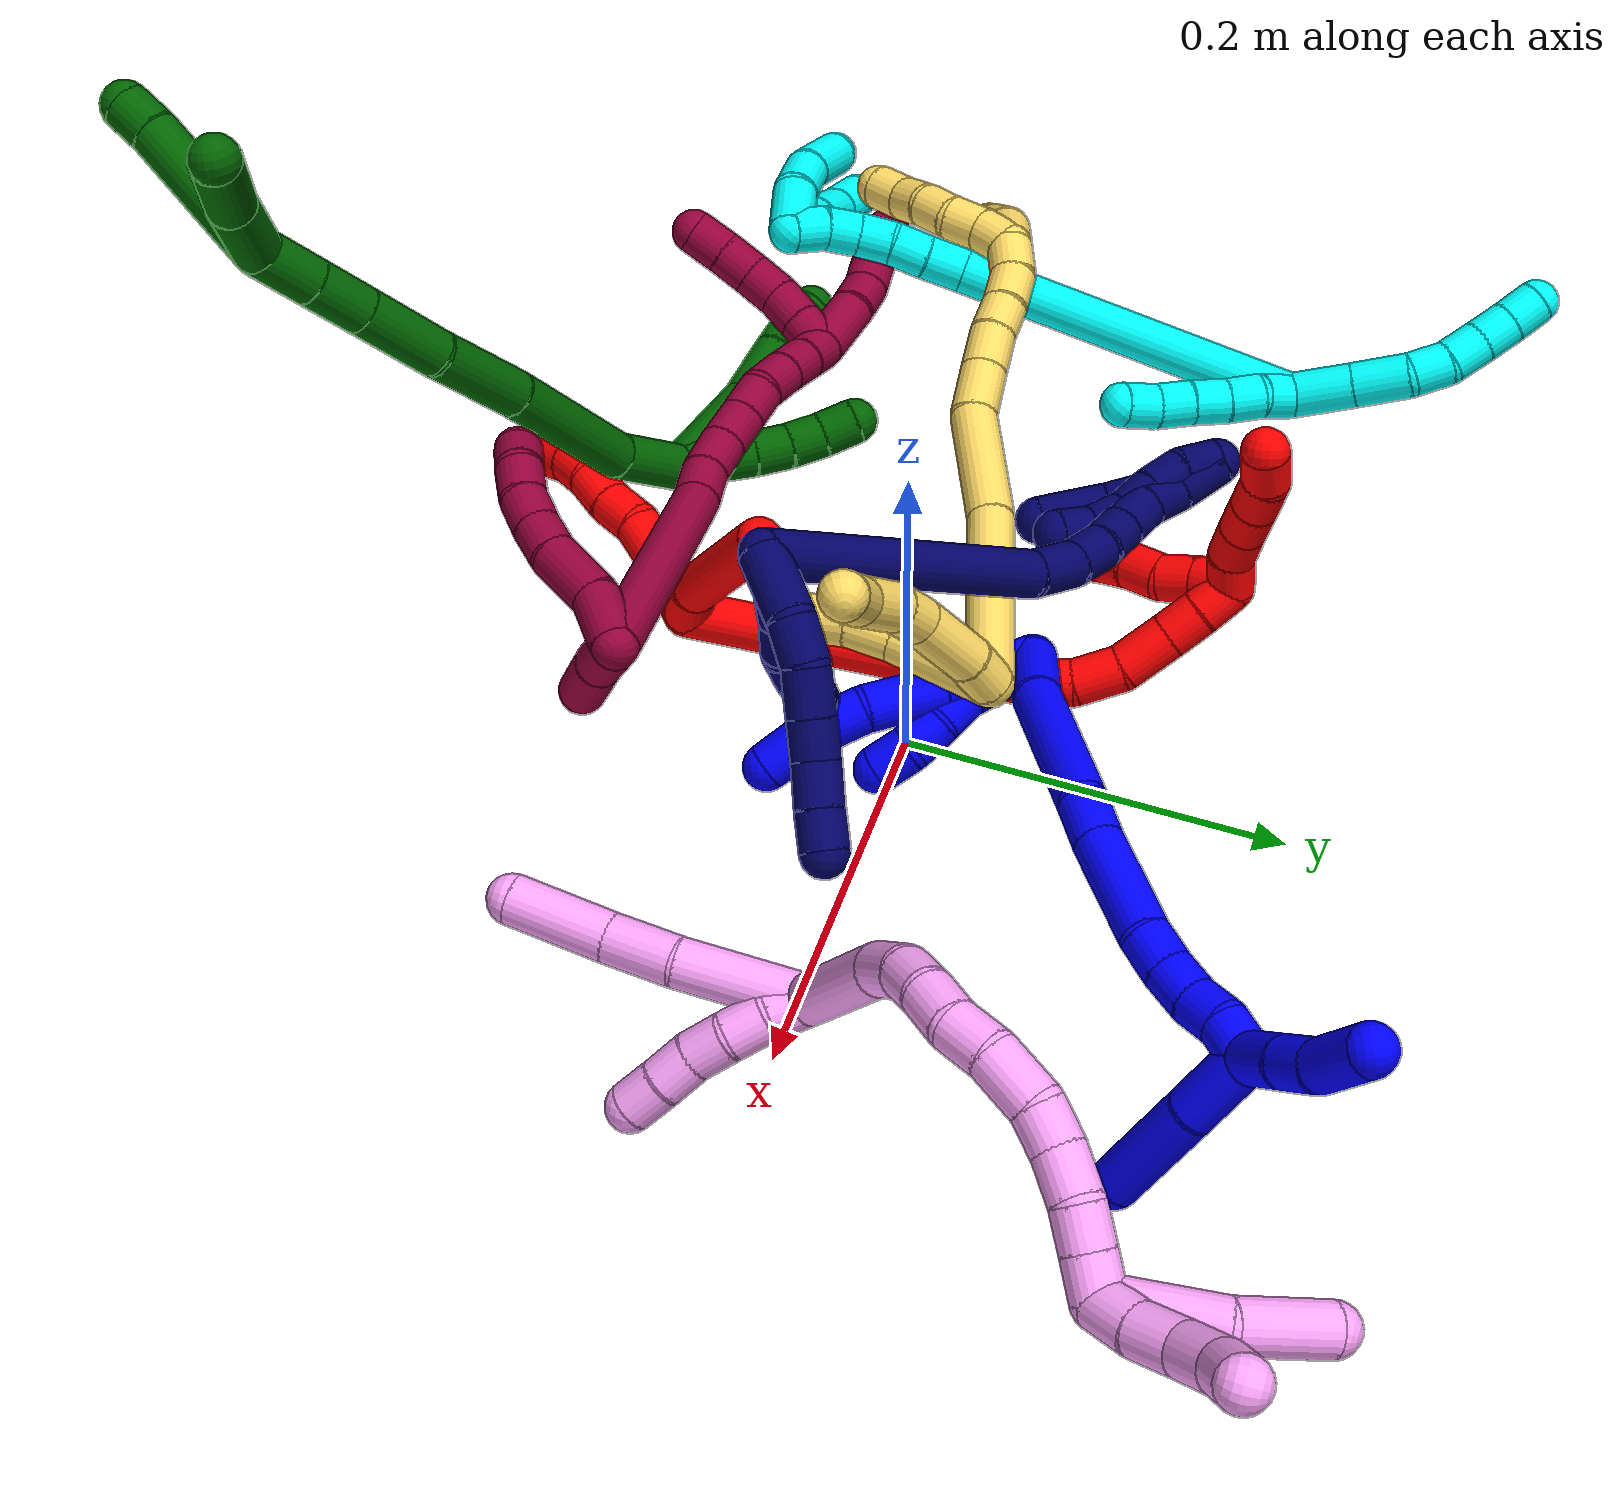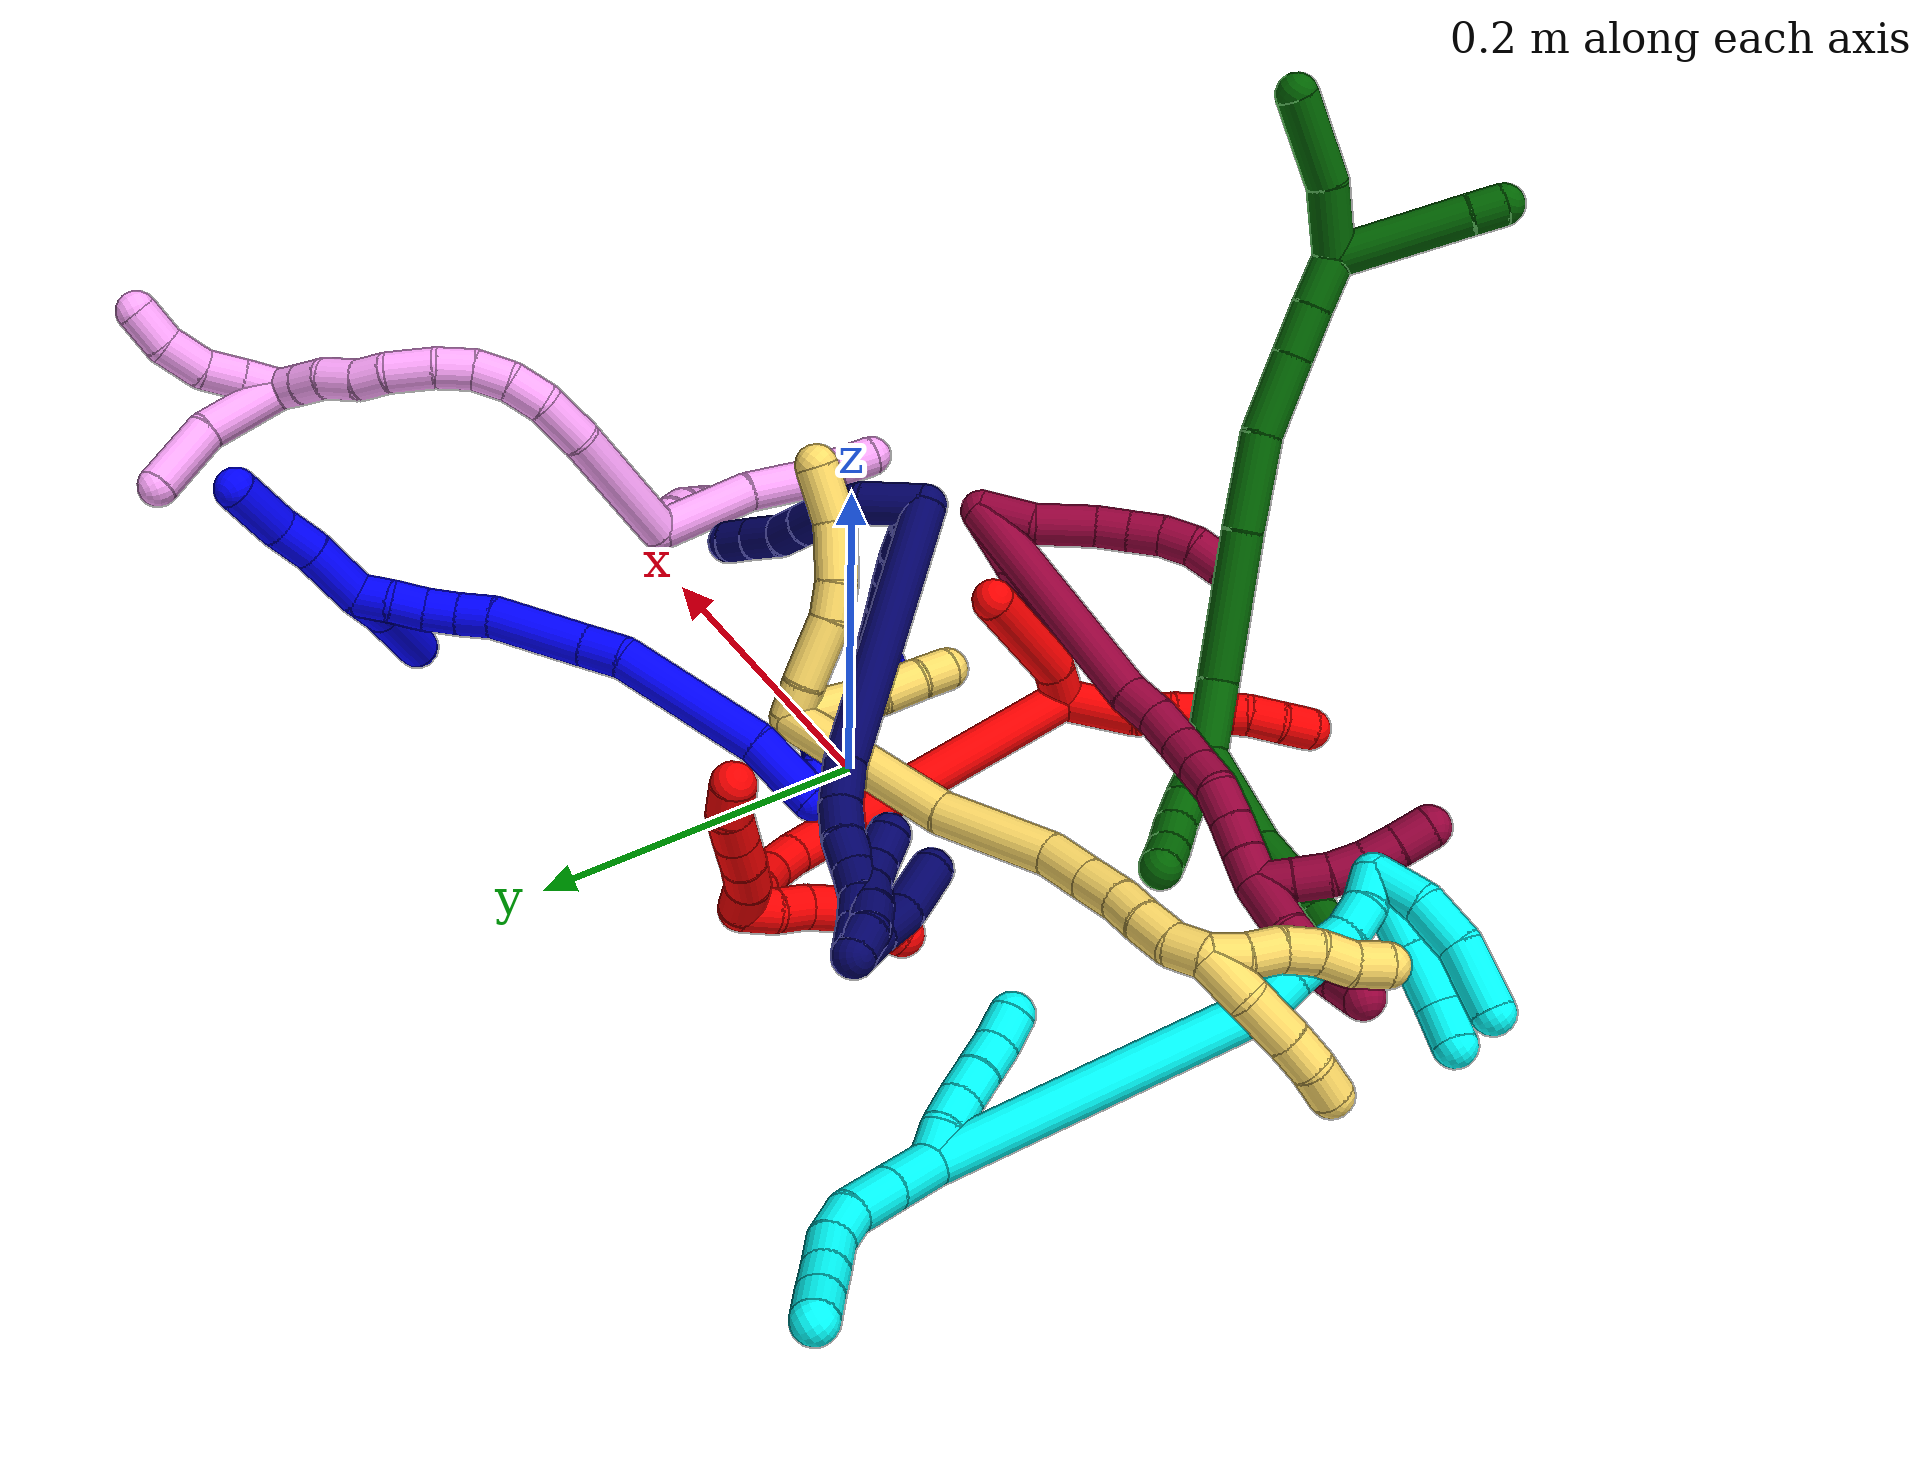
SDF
<sdf version="1.7">
 <world name="default">
  <plugin name="TubeGeneratorPlugin" filename="libtube_generator_plugin.so"/>
  <model name="photoneo_s_sensor">
   <static>1</static>
   <pose>0 0 2 1.57079 1.57079 3.14159</pose>
   <link name="link">
    <inertial><mass>0.1</mass></inertial>
    <sensor name="sensor" type="depth">
     <update_rate>30</update_rate>
     <camera>
      <horizontal_fov>1.22</horizontal_fov>
      <image><width>1920</width><height>1200</height><format>B8G8R8</format></image>
      <clip><near>0.1</near><far>4</far></clip>
      <depth_camera><output>points</output></depth_camera>
     </camera>
     <plugin name="camera_plugin" filename="libgazebo_ros_depth_camera.so">
      <baseline>0.2</baseline>
      <alwaysOn>1</alwaysOn>
      <updateRate>0.0</updateRate>
      <cameraName>camera_ir</cameraName>
      <imageTopicName>/camera/color/image_raw</imageTopicName>
      <cameraInfoTopicName>/camera/color/camera_info</cameraInfoTopicName>
      <depthImageTopicName>/camera/depth/image_raw</depthImageTopicName>
      <depthImageCameraInfoTopicName>/camera/depth/camera_info</depthImageCameraInfoTopicName>
      <pointCloudTopicName>/camera/depth/points</pointCloudTopicName>
      <frameName>fr_optical</frameName>
      <pointCloudCutoff>0.1</pointCloudCutoff>
      <pointCloudCutoffMax>2.0</pointCloudCutoffMax>
      <distortionK1>0</distortionK1>
      <distortionK2>0</distortionK2>
      <distortionK3>0</distortionK3>
      <distortionT1>0</distortionT1>
      <distortionT2>0</distortionT2>
      <CxPrime>0</CxPrime>
      <Cx>0</Cx>
      <Cy>0</Cy>
      <focalLength>0</focalLength>
      <hackBaseline>0</hackBaseline>
     </plugin>
    </sensor>
   </link>
  </model>
  <gravity>0 0 -9.8</gravity>
  <magnetic_field>6e-06 2.3e-05 -4.2e-05</magnetic_field>
  <atmosphere type="adiabatic"/>
  <physics name="default_physics" default="0" type="ode">
   <max_step_size>0.003</max_step_size>
   <real_time_factor>1</real_time_factor>
   <real_time_update_rate>1000</real_time_update_rate>
   <max_contacts>10000</max_contacts>
   <ode>
    <solver>
     <type>quick</type>
     <iters>100</iters>
     <sor>1.3</sor>
     <use_dynamic_moi_rescaling>0</use_dynamic_moi_rescaling>
    </solver>
    <constraints>
     <contact_max_correcting_vel>0</contact_max_correcting_vel>
     <contact_surface_layer>0.001</contact_surface_layer>
     <cfm>0</cfm>
     <erp>0.2</erp>
    </constraints>
   </ode>
  </physics>
  <scene><ambient>0.4 0.4 0.4 1</ambient><background>0.7 0.7 0.7 1</background><shadows>0</shadows></scene>
  <audio><device>default</device></audio>
  <spherical_coordinates>
   <surface_model>EARTH_WGS84</surface_model>
   <latitude_deg>0</latitude_deg>
   <longitude_deg>0</longitude_deg>
   <elevation>0</elevation>
   <heading_deg>0</heading_deg>
  </spherical_coordinates>
  <model name="bin">
   <static>1</static>
   <link name="bottom">
    <collision name="collision-bottom">
     <pose>0 0 -0.01 0 -0 0</pose>
     <geometry><box><size>0.8 0.6 0.02</size></box></geometry>
     <surface>
      <friction><ode><mu>100</mu><mu2>100</mu2></ode></friction>
      <contact><collide_bitmask>65535</collide_bitmask></contact>
     </surface>
    </collision>
   </link>
   <link name="west_wall">
    <collision name="collision-west_wall">
     <pose>-0.41 0 0.1 0 -0 0</pose>
     <geometry><box><size>0.02 0.6 0.2</size></box></geometry>
     <surface>
      <friction><ode><mu>100</mu><mu2>100</mu2></ode></friction>
      <contact><collide_bitmask>65535</collide_bitmask></contact>
     </surface>
    </collision>
   </link>
   <link name="east_wall">
    <collision name="collision-east_wall">
     <pose>0.41 0 0.1 0 -0 0</pose>
     <geometry><box><size>0.02 0.6 0.2</size></box></geometry>
     <surface>
      <friction><ode><mu>100</mu><mu2>100</mu2></ode></friction>
      <contact><collide_bitmask>65535</collide_bitmask></contact>
     </surface>
    </collision>
   </link>
   <link name="south_wall">
    <collision name="collision-south_wall">
     <pose>0 -0.31 0.1 0 -0 0</pose>
     <geometry><box><size>0.8 0.02 0.2</size></box></geometry>
     <surface>
      <friction><ode><mu>100</mu><mu2>100</mu2></ode></friction>
      <contact><collide_bitmask>65535</collide_bitmask></contact>
     </surface>
    </collision>
   </link>
   <link name="north_wall">
    <collision name="collision-north_wall">
     <pose>0 0.31 0.1 0 -0 0</pose>
     <geometry><box><size>0.8 0.02 0.2</size></box></geometry>
     <surface>
      <friction><ode><mu>100</mu><mu2>100</mu2></ode></friction>
      <contact><collide_bitmask>65535</collide_bitmask></contact>
     </surface>
    </collision>
   </link>
  </model>
  <model name="1">
   <static>0</static>
   <link name="1">
    <collision name="collision-cylinder-e_1_2_8">
     <pose>0.000308 0.004281 -0.009701 -2.72599 0.02908 -0.137713</pose>
     <geometry><cylinder><radius>0.0125</radius><length>0.021217</length></cylinder></geometry>
     <surface>
      <friction><ode><mu>1.16</mu><mu2>1.16</mu2><slip1>0</slip1><slip2>0</slip2></ode></friction>
      <contact><ode><kp>1e+06</kp><kd>1</kd><max_vel>0</max_vel><min_depth>0.001</min_depth></ode></contact>
     </surface>
    </collision>
    <visual name="visual-cylinder-e_1_2_8">
     <pose>0.000308 0.004281 -0.009701 -2.72599 0.02908 -0.137713</pose>
     <geometry><cylinder><radius>0.0125</radius><length>0.021217</length></cylinder></geometry>
     <material><ambient>0 0 1 1</ambient></material>
    </visual>
    <collision name="collision-cylinder-e_2_8_9">
     <pose>0.002566 0.012786 -0.033921 -2.85853 0.128222 -0.846643</pose>
     <geometry><cylinder><radius>0.0125</radius><length>0.03049</length></cylinder></geometry>
     <surface>
      <friction><ode><mu>1.16</mu><mu2>1.16</mu2><slip1>0</slip1><slip2>0</slip2></ode></friction>
      <contact><ode><kp>1e+06</kp><kd>1</kd><max_vel>0</max_vel><min_depth>0.001</min_depth></ode></contact>
     </surface>
    </collision>
    <visual name="visual-cylinder-e_2_8_9">
     <pose>0.002566 0.012786 -0.033921 -2.85853 0.128222 -0.846643</pose>
     <geometry><cylinder><radius>0.0125</radius><length>0.03049</length></cylinder></geometry>
     <material><ambient>0 0 1 1</ambient></material>
    </visual>
    <collision name="collision-cylinder-e_3_9_10">
     <pose>0.006511 0.022196 -0.06837 -2.88698 0.096578 -0.722016</pose>
     <geometry><cylinder><radius>0.0125</radius><length>0.041384</length></cylinder></geometry>
     <surface>
      <friction><ode><mu>1.16</mu><mu2>1.16</mu2><slip1>0</slip1><slip2>0</slip2></ode></friction>
      <contact><ode><kp>1e+06</kp><kd>1</kd><max_vel>0</max_vel><min_depth>0.001</min_depth></ode></contact>
     </surface>
    </collision>
    <visual name="visual-cylinder-e_3_9_10">
     <pose>0.006511 0.022196 -0.06837 -2.88698 0.096578 -0.722016</pose>
     <geometry><cylinder><radius>0.0125</radius><length>0.041384</length></cylinder></geometry>
     <material><ambient>0 0 1 1</ambient></material>
    </visual>
    <collision name="collision-cylinder-e_4_10_11">
     <pose>0.006267 0.030779 -0.101476 -2.88936 -0.163138 1.14539</pose>
     <geometry><cylinder><radius>0.0125</radius><length>0.027575</length></cylinder></geometry>
     <surface>
      <friction><ode><mu>1.16</mu><mu2>1.16</mu2><slip1>0</slip1><slip2>0</slip2></ode></friction>
      <contact><ode><kp>1e+06</kp><kd>1</kd><max_vel>0</max_vel><min_depth>0.001</min_depth></ode></contact>
     </surface>
    </collision>
    <visual name="visual-cylinder-e_4_10_11">
     <pose>0.006267 0.030779 -0.101476 -2.88936 -0.163138 1.14539</pose>
     <geometry><cylinder><radius>0.0125</radius><length>0.027575</length></cylinder></geometry>
     <material><ambient>0 0 1 1</ambient></material>
    </visual>
    <collision name="collision-cylinder-e_5_11_6">
     <pose>-0.00167 0.038332 -0.12751 -2.82888 -0.398996 1.81713</pose>
     <geometry><cylinder><radius>0.0125</radius><length>0.029334</length></cylinder></geometry>
     <surface>
      <friction><ode><mu>1.16</mu><mu2>1.16</mu2><slip1>0</slip1><slip2>0</slip2></ode></friction>
      <contact><ode><kp>1e+06</kp><kd>1</kd><max_vel>0</max_vel><min_depth>0.001</min_depth></ode></contact>
     </surface>
    </collision>
    <visual name="visual-cylinder-e_5_11_6">
     <pose>-0.00167 0.038332 -0.12751 -2.82888 -0.398996 1.81713</pose>
     <geometry><cylinder><radius>0.0125</radius><length>0.029334</length></cylinder></geometry>
     <material><ambient>0 0 1 1</ambient></material>
    </visual>
    <collision name="collision-cylinder-e_1_2_12">
     <pose>-0.001452 0.008024 -0.018074 -2.72379 -0.073289 0.342479</pose>
     <geometry><cylinder><radius>0.0125</radius><length>0.039657</length></cylinder></geometry>
     <surface>
      <friction><ode><mu>1.16</mu><mu2>1.16</mu2><slip1>0</slip1><slip2>0</slip2></ode></friction>
      <contact><ode><kp>1e+06</kp><kd>1</kd><max_vel>0</max_vel><min_depth>0.001</min_depth></ode></contact>
     </surface>
    </collision>
    <visual name="visual-cylinder-e_1_2_12">
     <pose>-0.001452 0.008024 -0.018074 -2.72379 -0.073289 0.342479</pose>
     <geometry><cylinder><radius>0.0125</radius><length>0.039657</length></cylinder></geometry>
     <material><ambient>0 0 1 1</ambient></material>
    </visual>
    <collision name="collision-cylinder-e_2_12_13">
     <pose>-0.004448 0.022405 -0.043884 -2.4537 -0.153009 0.421655</pose>
     <geometry><cylinder><radius>0.0125</radius><length>0.020264</length></cylinder></geometry>
     <surface>
      <friction><ode><mu>1.16</mu><mu2>1.16</mu2><slip1>0</slip1><slip2>0</slip2></ode></friction>
      <contact><ode><kp>1e+06</kp><kd>1</kd><max_vel>0</max_vel><min_depth>0.001</min_depth></ode></contact>
     </surface>
    </collision>
    <visual name="visual-cylinder-e_2_12_13">
     <pose>-0.004448 0.022405 -0.043884 -2.4537 -0.153009 0.421655</pose>
     <geometry><cylinder><radius>0.0125</radius><length>0.020264</length></cylinder></geometry>
     <material><ambient>0 0 1 1</ambient></material>
    </visual>
    <collision name="collision-cylinder-e_3_13_14">
     <pose>-0.009256 0.033583 -0.059777 -2.60784 -0.331798 1.09903</pose>
     <geometry><cylinder><radius>0.0125</radius><length>0.020041</length></cylinder></geometry>
     <surface>
      <friction><ode><mu>1.16</mu><mu2>1.16</mu2><slip1>0</slip1><slip2>0</slip2></ode></friction>
      <contact><ode><kp>1e+06</kp><kd>1</kd><max_vel>0</max_vel><min_depth>0.001</min_depth></ode></contact>
     </surface>
    </collision>
    <visual name="visual-cylinder-e_3_13_14">
     <pose>-0.009256 0.033583 -0.059777 -2.60784 -0.331798 1.09903</pose>
     <geometry><cylinder><radius>0.0125</radius><length>0.020041</length></cylinder></geometry>
     <material><ambient>0 0 1 1</ambient></material>
    </visual>
    <collision name="collision-cylinder-e_4_14_5">
     <pose>-0.016643 0.040254 -0.076875 -2.93745 -0.424098 2.25345</pose>
     <geometry><cylinder><radius>0.0125</radius><length>0.020039</length></cylinder></geometry>
     <surface>
      <friction><ode><mu>1.16</mu><mu2>1.16</mu2><slip1>0</slip1><slip2>0</slip2></ode></friction>
      <contact><ode><kp>1e+06</kp><kd>1</kd><max_vel>0</max_vel><min_depth>0.001</min_depth></ode></contact>
     </surface>
    </collision>
    <visual name="visual-cylinder-e_4_14_5">
     <pose>-0.016643 0.040254 -0.076875 -2.93745 -0.424098 2.25345</pose>
     <geometry><cylinder><radius>0.0125</radius><length>0.020039</length></cylinder></geometry>
     <material><ambient>0 0 1 1</ambient></material>
    </visual>
    <collision name="collision-cylinder-e_1_2_15">
     <pose>0.00766 0.021117 -0.001004 -1.61832 0.347623 -0.364187</pose>
     <geometry><cylinder><radius>0.0125</radius><length>0.044972</length></cylinder></geometry>
     <surface>
      <friction><ode><mu>1.16</mu><mu2>1.16</mu2><slip1>0</slip1><slip2>0</slip2></ode></friction>
      <contact><ode><kp>1e+06</kp><kd>1</kd><max_vel>0</max_vel><min_depth>0.001</min_depth></ode></contact>
     </surface>
    </collision>
    <visual name="visual-cylinder-e_1_2_15">
     <pose>0.00766 0.021117 -0.001004 -1.61832 0.347623 -0.364187</pose>
     <geometry><cylinder><radius>0.0125</radius><length>0.044972</length></cylinder></geometry>
     <material><ambient>0 0 1 1</ambient></material>
    </visual>
    <collision name="collision-cylinder-e_2_15_16">
     <pose>0.024633 0.086339 0.003876 -1.43816 0.206306 -0.180757</pose>
     <geometry><cylinder><radius>0.0125</radius><length>0.09092</length></cylinder></geometry>
     <surface>
      <friction><ode><mu>1.16</mu><mu2>1.16</mu2><slip1>0</slip1><slip2>0</slip2></ode></friction>
      <contact><ode><kp>1e+06</kp><kd>1</kd><max_vel>0</max_vel><min_depth>0.001</min_depth></ode></contact>
     </surface>
    </collision>
    <visual name="visual-cylinder-e_2_15_16">
     <pose>0.024633 0.086339 0.003876 -1.43816 0.206306 -0.180757</pose>
     <geometry><cylinder><radius>0.0125</radius><length>0.09092</length></cylinder></geometry>
     <material><ambient>0 0 1 1</ambient></material>
    </visual>
    <collision name="collision-cylinder-e_3_16_17">
     <pose>0.032575 0.142497 0.011861 -1.39824 -0.111543 0.093813</pose>
     <geometry><cylinder><radius>0.0125</radius><length>0.024621</length></cylinder></geometry>
     <surface>
      <friction><ode><mu>1.16</mu><mu2>1.16</mu2><slip1>0</slip1><slip2>0</slip2></ode></friction>
      <contact><ode><kp>1e+06</kp><kd>1</kd><max_vel>0</max_vel><min_depth>0.001</min_depth></ode></contact>
     </surface>
    </collision>
    <visual name="visual-cylinder-e_3_16_17">
     <pose>0.032575 0.142497 0.011861 -1.39824 -0.111543 0.093813</pose>
     <geometry><cylinder><radius>0.0125</radius><length>0.024621</length></cylinder></geometry>
     <material><ambient>0 0 1 1</ambient></material>
    </visual>
    <collision name="collision-cylinder-e_4_17_18">
     <pose>0.029732 0.18283 0.02065 -1.33858 -0.050631 0.040057</pose>
     <geometry><cylinder><radius>0.0125</radius><length>0.058198</length></cylinder></geometry>
     <surface>
      <friction><ode><mu>1.16</mu><mu2>1.16</mu2><slip1>0</slip1><slip2>0</slip2></ode></friction>
      <contact><ode><kp>1e+06</kp><kd>1</kd><max_vel>0</max_vel><min_depth>0.001</min_depth></ode></contact>
     </surface>
    </collision>
    <visual name="visual-cylinder-e_4_17_18">
     <pose>0.029732 0.18283 0.02065 -1.33858 -0.050631 0.040057</pose>
     <geometry><cylinder><radius>0.0125</radius><length>0.058198</length></cylinder></geometry>
     <material><ambient>0 0 1 1</ambient></material>
    </visual>
    <collision name="collision-cylinder-e_5_18_19">
     <pose>0.026328 0.220488 0.031204 -1.17969 -0.188149 0.12614</pose>
     <geometry><cylinder><radius>0.0125</radius><length>0.020648</length></cylinder></geometry>
     <surface>
      <friction><ode><mu>1.16</mu><mu2>1.16</mu2><slip1>0</slip1><slip2>0</slip2></ode></friction>
      <contact><ode><kp>1e+06</kp><kd>1</kd><max_vel>0</max_vel><min_depth>0.001</min_depth></ode></contact>
     </surface>
    </collision>
    <visual name="visual-cylinder-e_5_18_19">
     <pose>0.026328 0.220488 0.031204 -1.17969 -0.188149 0.12614</pose>
     <geometry><cylinder><radius>0.0125</radius><length>0.020648</length></cylinder></geometry>
     <material><ambient>0 0 1 1</ambient></material>
    </visual>
    <collision name="collision-cylinder-e_6_19_20">
     <pose>0.02365 0.238932 0.039505 -1.11598 -0.073852 0.046108</pose>
     <geometry><cylinder><radius>0.0125</radius><length>0.020245</length></cylinder></geometry>
     <surface>
      <friction><ode><mu>1.16</mu><mu2>1.16</mu2><slip1>0</slip1><slip2>0</slip2></ode></friction>
      <contact><ode><kp>1e+06</kp><kd>1</kd><max_vel>0</max_vel><min_depth>0.001</min_depth></ode></contact>
     </surface>
    </collision>
    <visual name="visual-cylinder-e_6_19_20">
     <pose>0.02365 0.238932 0.039505 -1.11598 -0.073852 0.046108</pose>
     <geometry><cylinder><radius>0.0125</radius><length>0.020245</length></cylinder></geometry>
     <material><ambient>0 0 1 1</ambient></material>
    </visual>
    <collision name="collision-cylinder-e_7_20_21">
     <pose>0.024231 0.256427 0.049273 -1.00646 0.132366 -0.072942</pose>
     <geometry><cylinder><radius>0.0125</radius><length>0.020121</length></cylinder></geometry>
     <surface>
      <friction><ode><mu>1.16</mu><mu2>1.16</mu2><slip1>0</slip1><slip2>0</slip2></ode></friction>
      <contact><ode><kp>1e+06</kp><kd>1</kd><max_vel>0</max_vel><min_depth>0.001</min_depth></ode></contact>
     </surface>
    </collision>
    <visual name="visual-cylinder-e_7_20_21">
     <pose>0.024231 0.256427 0.049273 -1.00646 0.132366 -0.072942</pose>
     <geometry><cylinder><radius>0.0125</radius><length>0.020121</length></cylinder></geometry>
     <material><ambient>0 0 1 1</ambient></material>
    </visual>
    <collision name="collision-cylinder-e_8_21_1">
     <pose>0.024601 0.274289 0.058188 -1.20806 -0.094561 0.06528</pose>
     <geometry><cylinder><radius>0.0125</radius><length>0.020276</length></cylinder></geometry>
     <surface>
      <friction><ode><mu>1.16</mu><mu2>1.16</mu2><slip1>0</slip1><slip2>0</slip2></ode></friction>
      <contact><ode><kp>1e+06</kp><kd>1</kd><max_vel>0</max_vel><min_depth>0.001</min_depth></ode></contact>
     </surface>
    </collision>
    <visual name="visual-cylinder-e_8_21_1">
     <pose>0.024601 0.274289 0.058188 -1.20806 -0.094561 0.06528</pose>
     <geometry><cylinder><radius>0.0125</radius><length>0.020276</length></cylinder></geometry>
     <material><ambient>0 0 1 1</ambient></material>
    </visual>
    <collision name="collision-cylinder-e_1_1_22">
     <pose>0.009019 0.285465 0.048503 -3.01116 -0.829846 2.84721</pose>
     <geometry><cylinder><radius>0.0125</radius><length>0.039645</length></cylinder></geometry>
     <surface>
      <friction><ode><mu>1.16</mu><mu2>1.16</mu2><slip1>0</slip1><slip2>0</slip2></ode></friction>
      <contact><ode><kp>1e+06</kp><kd>1</kd><max_vel>0</max_vel><min_depth>0.001</min_depth></ode></contact>
     </surface>
    </collision>
    <visual name="visual-cylinder-e_1_1_22">
     <pose>0.009019 0.285465 0.048503 -3.01116 -0.829846 2.84721</pose>
     <geometry><cylinder><radius>0.0125</radius><length>0.039645</length></cylinder></geometry>
     <material><ambient>0 0 1 1</ambient></material>
    </visual>
    <collision name="collision-cylinder-e_2_22_4">
     <pose>-0.029571 0.286894 0.016898 3.12462 -0.917526 -3.10724</pose>
     <geometry><cylinder><radius>0.0125</radius><length>0.060355</length></cylinder></geometry>
     <surface>
      <friction><ode><mu>1.16</mu><mu2>1.16</mu2><slip1>0</slip1><slip2>0</slip2></ode></friction>
      <contact><ode><kp>1e+06</kp><kd>1</kd><max_vel>0</max_vel><min_depth>0.001</min_depth></ode></contact>
     </surface>
    </collision>
    <visual name="visual-cylinder-e_2_22_4">
     <pose>-0.029571 0.286894 0.016898 3.12462 -0.917526 -3.10724</pose>
     <geometry><cylinder><radius>0.0125</radius><length>0.060355</length></cylinder></geometry>
     <material><ambient>0 0 1 1</ambient></material>
    </visual>
    <collision name="collision-cylinder-e_1_1_23">
     <pose>0.036538 0.295978 0.068453 -1.07144 0.74583 -0.456387</pose>
     <geometry><cylinder><radius>0.0125</radius><length>0.038003</length></cylinder></geometry>
     <surface>
      <friction><ode><mu>1.16</mu><mu2>1.16</mu2><slip1>0</slip1><slip2>0</slip2></ode></friction>
      <contact><ode><kp>1e+06</kp><kd>1</kd><max_vel>0</max_vel><min_depth>0.001</min_depth></ode></contact>
     </surface>
    </collision>
    <visual name="visual-cylinder-e_1_1_23">
     <pose>0.036538 0.295978 0.068453 -1.07144 0.74583 -0.456387</pose>
     <geometry><cylinder><radius>0.0125</radius><length>0.038003</length></cylinder></geometry>
     <material><ambient>0 0 1 1</ambient></material>
    </visual>
    <collision name="collision-cylinder-e_2_23_24">
     <pose>0.057053 0.316068 0.081137 -0.917381 0.657472 -0.333763</pose>
     <geometry><cylinder><radius>0.0125</radius><length>0.024941</length></cylinder></geometry>
     <surface>
      <friction><ode><mu>1.16</mu><mu2>1.16</mu2><slip1>0</slip1><slip2>0</slip2></ode></friction>
      <contact><ode><kp>1e+06</kp><kd>1</kd><max_vel>0</max_vel><min_depth>0.001</min_depth></ode></contact>
     </surface>
    </collision>
    <visual name="visual-cylinder-e_2_23_24">
     <pose>0.057053 0.316068 0.081137 -0.917381 0.657472 -0.333763</pose>
     <geometry><cylinder><radius>0.0125</radius><length>0.024941</length></cylinder></geometry>
     <material><ambient>0 0 1 1</ambient></material>
    </visual>
    <collision name="collision-cylinder-e_3_24_3">
     <pose>0.078585 0.331829 0.096466 -0.704112 0.849234 -0.329178</pose>
     <geometry><cylinder><radius>0.0125</radius><length>0.037056</length></cylinder></geometry>
     <surface>
      <friction><ode><mu>1.16</mu><mu2>1.16</mu2><slip1>0</slip1><slip2>0</slip2></ode></friction>
      <contact><ode><kp>1e+06</kp><kd>1</kd><max_vel>0</max_vel><min_depth>0.001</min_depth></ode></contact>
     </surface>
    </collision>
    <visual name="visual-cylinder-e_3_24_3">
     <pose>0.078585 0.331829 0.096466 -0.704112 0.849234 -0.329178</pose>
     <geometry><cylinder><radius>0.0125</radius><length>0.037056</length></cylinder></geometry>
     <material><ambient>0 0 1 1</ambient></material>
    </visual>
    <collision name="collision-sphere-3">
     <pose>0.092495 0.339752 0.105794 0 -0 0</pose>
     <geometry><sphere><radius>0.0125</radius></sphere></geometry>
     <surface>
      <friction><ode><mu>1.16</mu><mu2>1.16</mu2><slip1>0</slip1><slip2>0</slip2></ode></friction>
      <contact><ode><kp>1e+06</kp><kd>1</kd><max_vel>0</max_vel><min_depth>0.001</min_depth></ode></contact>
     </surface>
    </collision>
    <visual name="visual-sphere-3">
     <pose>0.092495 0.339752 0.105794 0 -0 0</pose>
     <geometry><sphere><radius>0.0125</radius></sphere></geometry>
     <material><ambient>0 0 1 1</ambient></material>
    </visual>
    <collision name="collision-sphere-24">
     <pose>0.064674 0.323906 0.087138 0 -0 0</pose>
     <geometry><sphere><radius>0.0125</radius></sphere></geometry>
     <surface>
      <friction><ode><mu>1.16</mu><mu2>1.16</mu2><slip1>0</slip1><slip2>0</slip2></ode></friction>
      <contact><ode><kp>1e+06</kp><kd>1</kd><max_vel>0</max_vel><min_depth>0.001</min_depth></ode></contact>
     </surface>
    </collision>
    <visual name="visual-sphere-24">
     <pose>0.064674 0.323906 0.087138 0 -0 0</pose>
     <geometry><sphere><radius>0.0125</radius></sphere></geometry>
     <material><ambient>0 0 1 1</ambient></material>
    </visual>
    <collision name="collision-sphere-23">
     <pose>0.049432 0.308231 0.075136 0 -0 0</pose>
     <geometry><sphere><radius>0.0125</radius></sphere></geometry>
     <surface>
      <friction><ode><mu>1.16</mu><mu2>1.16</mu2><slip1>0</slip1><slip2>0</slip2></ode></friction>
      <contact><ode><kp>1e+06</kp><kd>1</kd><max_vel>0</max_vel><min_depth>0.001</min_depth></ode></contact>
     </surface>
    </collision>
    <visual name="visual-sphere-23">
     <pose>0.049432 0.308231 0.075136 0 -0 0</pose>
     <geometry><sphere><radius>0.0125</radius></sphere></geometry>
     <material><ambient>0 0 1 1</ambient></material>
    </visual>
    <collision name="collision-sphere-4">
     <pose>-0.053535 0.286583 -0.001441 0 -0 0</pose>
     <geometry><sphere><radius>0.0125</radius></sphere></geometry>
     <surface>
      <friction><ode><mu>1.16</mu><mu2>1.16</mu2><slip1>0</slip1><slip2>0</slip2></ode></friction>
      <contact><ode><kp>1e+06</kp><kd>1</kd><max_vel>0</max_vel><min_depth>0.001</min_depth></ode></contact>
     </surface>
    </collision>
    <visual name="visual-sphere-4">
     <pose>-0.053535 0.286583 -0.001441 0 -0 0</pose>
     <geometry><sphere><radius>0.0125</radius></sphere></geometry>
     <material><ambient>0 0 1 1</ambient></material>
    </visual>
    <collision name="collision-sphere-22">
     <pose>-0.005607 0.287206 0.035237 0 -0 0</pose>
     <geometry><sphere><radius>0.0125</radius></sphere></geometry>
     <surface>
      <friction><ode><mu>1.16</mu><mu2>1.16</mu2><slip1>0</slip1><slip2>0</slip2></ode></friction>
      <contact><ode><kp>1e+06</kp><kd>1</kd><max_vel>0</max_vel><min_depth>0.001</min_depth></ode></contact>
     </surface>
    </collision>
    <visual name="visual-sphere-22">
     <pose>-0.005607 0.287206 0.035237 0 -0 0</pose>
     <geometry><sphere><radius>0.0125</radius></sphere></geometry>
     <material><ambient>0 0 1 1</ambient></material>
    </visual>
    <collision name="collision-sphere-1">
     <pose>0.023644 0.283725 0.06177 0 -0 0</pose>
     <geometry><sphere><radius>0.0125</radius></sphere></geometry>
     <surface>
      <friction><ode><mu>1.16</mu><mu2>1.16</mu2><slip1>0</slip1><slip2>0</slip2></ode></friction>
      <contact><ode><kp>1e+06</kp><kd>1</kd><max_vel>0</max_vel><min_depth>0.001</min_depth></ode></contact>
     </surface>
    </collision>
    <visual name="visual-sphere-1">
     <pose>0.023644 0.283725 0.06177 0 -0 0</pose>
     <geometry><sphere><radius>0.0125</radius></sphere></geometry>
     <material><ambient>0 0 1 1</ambient></material>
    </visual>
    <collision name="collision-sphere-21">
     <pose>0.025559 0.264853 0.054607 0 -0 0</pose>
     <geometry><sphere><radius>0.0125</radius></sphere></geometry>
     <surface>
      <friction><ode><mu>1.16</mu><mu2>1.16</mu2><slip1>0</slip1><slip2>0</slip2></ode></friction>
      <contact><ode><kp>1e+06</kp><kd>1</kd><max_vel>0</max_vel><min_depth>0.001</min_depth></ode></contact>
     </surface>
    </collision>
    <visual name="visual-sphere-21">
     <pose>0.025559 0.264853 0.054607 0 -0 0</pose>
     <geometry><sphere><radius>0.0125</radius></sphere></geometry>
     <material><ambient>0 0 1 1</ambient></material>
    </visual>
    <collision name="collision-sphere-6">
     <pose>-0.007368 0.042489 -0.140369 0 -0 0</pose>
     <geometry><sphere><radius>0.0125</radius></sphere></geometry>
     <surface>
      <friction><ode><mu>1.16</mu><mu2>1.16</mu2><slip1>0</slip1><slip2>0</slip2></ode></friction>
      <contact><ode><kp>1e+06</kp><kd>1</kd><max_vel>0</max_vel><min_depth>0.001</min_depth></ode></contact>
     </surface>
    </collision>
    <visual name="visual-sphere-6">
     <pose>-0.007368 0.042489 -0.140369 0 -0 0</pose>
     <geometry><sphere><radius>0.0125</radius></sphere></geometry>
     <material><ambient>0 0 1 1</ambient></material>
    </visual>
    <collision name="collision-sphere-11">
     <pose>0.004028 0.034174 -0.11465 0 -0 0</pose>
     <geometry><sphere><radius>0.0125</radius></sphere></geometry>
     <surface>
      <friction><ode><mu>1.16</mu><mu2>1.16</mu2><slip1>0</slip1><slip2>0</slip2></ode></friction>
      <contact><ode><kp>1e+06</kp><kd>1</kd><max_vel>0</max_vel><min_depth>0.001</min_depth></ode></contact>
     </surface>
    </collision>
    <visual name="visual-sphere-11">
     <pose>0.004028 0.034174 -0.11465 0 -0 0</pose>
     <geometry><sphere><radius>0.0125</radius></sphere></geometry>
     <material><ambient>0 0 1 1</ambient></material>
    </visual>
    <collision name="collision-sphere-10">
     <pose>0.008506 0.027383 -0.088302 0 -0 0</pose>
     <geometry><sphere><radius>0.0125</radius></sphere></geometry>
     <surface>
      <friction><ode><mu>1.16</mu><mu2>1.16</mu2><slip1>0</slip1><slip2>0</slip2></ode></friction>
      <contact><ode><kp>1e+06</kp><kd>1</kd><max_vel>0</max_vel><min_depth>0.001</min_depth></ode></contact>
     </surface>
    </collision>
    <visual name="visual-sphere-10">
     <pose>0.008506 0.027383 -0.088302 0 -0 0</pose>
     <geometry><sphere><radius>0.0125</radius></sphere></geometry>
     <material><ambient>0 0 1 1</ambient></material>
    </visual>
    <collision name="collision-sphere-9">
     <pose>0.004516 0.017009 -0.048439 0 -0 0</pose>
     <geometry><sphere><radius>0.0125</radius></sphere></geometry>
     <surface>
      <friction><ode><mu>1.16</mu><mu2>1.16</mu2><slip1>0</slip1><slip2>0</slip2></ode></friction>
      <contact><ode><kp>1e+06</kp><kd>1</kd><max_vel>0</max_vel><min_depth>0.001</min_depth></ode></contact>
     </surface>
    </collision>
    <visual name="visual-sphere-9">
     <pose>0.004516 0.017009 -0.048439 0 -0 0</pose>
     <geometry><sphere><radius>0.0125</radius></sphere></geometry>
     <material><ambient>0 0 1 1</ambient></material>
    </visual>
    <collision name="collision-sphere-2">
     <geometry><sphere><radius>0.0125</radius></sphere></geometry>
     <surface>
      <friction><ode><mu>1.16</mu><mu2>1.16</mu2><slip1>0</slip1><slip2>0</slip2></ode></friction>
      <contact><ode><kp>1e+06</kp><kd>1</kd><max_vel>0</max_vel><min_depth>0.001</min_depth></ode></contact>
     </surface>
    </collision>
    <visual name="visual-sphere-2">
     <geometry><sphere><radius>0.0125</radius></sphere></geometry>
     <material><ambient>0 0 1 1</ambient></material>
    </visual>
    <collision name="collision-sphere-19">
     <pose>0.024397 0.229864 0.03507 0 -0 0</pose>
     <geometry><sphere><radius>0.0125</radius></sphere></geometry>
     <surface>
      <friction><ode><mu>1.16</mu><mu2>1.16</mu2><slip1>0</slip1><slip2>0</slip2></ode></friction>
      <contact><ode><kp>1e+06</kp><kd>1</kd><max_vel>0</max_vel><min_depth>0.001</min_depth></ode></contact>
     </surface>
    </collision>
    <visual name="visual-sphere-19">
     <pose>0.024397 0.229864 0.03507 0 -0 0</pose>
     <geometry><sphere><radius>0.0125</radius></sphere></geometry>
     <material><ambient>0 0 1 1</ambient></material>
    </visual>
    <collision name="collision-sphere-8">
     <pose>0.000617 0.008563 -0.019403 0 -0 0</pose>
     <geometry><sphere><radius>0.0125</radius></sphere></geometry>
     <surface>
      <friction><ode><mu>1.16</mu><mu2>1.16</mu2><slip1>0</slip1><slip2>0</slip2></ode></friction>
      <contact><ode><kp>1e+06</kp><kd>1</kd><max_vel>0</max_vel><min_depth>0.001</min_depth></ode></contact>
     </surface>
    </collision>
    <visual name="visual-sphere-8">
     <pose>0.000617 0.008563 -0.019403 0 -0 0</pose>
     <geometry><sphere><radius>0.0125</radius></sphere></geometry>
     <material><ambient>0 0 1 1</ambient></material>
    </visual>
    <collision name="collision-sphere-12">
     <pose>-0.002904 0.016048 -0.036148 0 -0 0</pose>
     <geometry><sphere><radius>0.0125</radius></sphere></geometry>
     <surface>
      <friction><ode><mu>1.16</mu><mu2>1.16</mu2><slip1>0</slip1><slip2>0</slip2></ode></friction>
      <contact><ode><kp>1e+06</kp><kd>1</kd><max_vel>0</max_vel><min_depth>0.001</min_depth></ode></contact>
     </surface>
    </collision>
    <visual name="visual-sphere-12">
     <pose>-0.002904 0.016048 -0.036148 0 -0 0</pose>
     <geometry><sphere><radius>0.0125</radius></sphere></geometry>
     <material><ambient>0 0 1 1</ambient></material>
    </visual>
    <collision name="collision-sphere-13">
     <pose>-0.005992 0.028763 -0.051621 0 -0 0</pose>
     <geometry><sphere><radius>0.0125</radius></sphere></geometry>
     <surface>
      <friction><ode><mu>1.16</mu><mu2>1.16</mu2><slip1>0</slip1><slip2>0</slip2></ode></friction>
      <contact><ode><kp>1e+06</kp><kd>1</kd><max_vel>0</max_vel><min_depth>0.001</min_depth></ode></contact>
     </surface>
    </collision>
    <visual name="visual-sphere-13">
     <pose>-0.005992 0.028763 -0.051621 0 -0 0</pose>
     <geometry><sphere><radius>0.0125</radius></sphere></geometry>
     <material><ambient>0 0 1 1</ambient></material>
    </visual>
    <collision name="collision-sphere-14">
     <pose>-0.01252 0.038403 -0.067933 0 -0 0</pose>
     <geometry><sphere><radius>0.0125</radius></sphere></geometry>
     <surface>
      <friction><ode><mu>1.16</mu><mu2>1.16</mu2><slip1>0</slip1><slip2>0</slip2></ode></friction>
      <contact><ode><kp>1e+06</kp><kd>1</kd><max_vel>0</max_vel><min_depth>0.001</min_depth></ode></contact>
     </surface>
    </collision>
    <visual name="visual-sphere-14">
     <pose>-0.01252 0.038403 -0.067933 0 -0 0</pose>
     <geometry><sphere><radius>0.0125</radius></sphere></geometry>
     <material><ambient>0 0 1 1</ambient></material>
    </visual>
    <collision name="collision-sphere-5">
     <pose>-0.020766 0.042105 -0.085817 0 -0 0</pose>
     <geometry><sphere><radius>0.0125</radius></sphere></geometry>
     <surface>
      <friction><ode><mu>1.16</mu><mu2>1.16</mu2><slip1>0</slip1><slip2>0</slip2></ode></friction>
      <contact><ode><kp>1e+06</kp><kd>1</kd><max_vel>0</max_vel><min_depth>0.001</min_depth></ode></contact>
     </surface>
    </collision>
    <visual name="visual-sphere-5">
     <pose>-0.020766 0.042105 -0.085817 0 -0 0</pose>
     <geometry><sphere><radius>0.0125</radius></sphere></geometry>
     <material><ambient>0 0 1 1</ambient></material>
    </visual>
    <collision name="collision-sphere-15">
     <pose>0.01532 0.042234 -0.002009 0 -0 0</pose>
     <geometry><sphere><radius>0.0125</radius></sphere></geometry>
     <surface>
      <friction><ode><mu>1.16</mu><mu2>1.16</mu2><slip1>0</slip1><slip2>0</slip2></ode></friction>
      <contact><ode><kp>1e+06</kp><kd>1</kd><max_vel>0</max_vel><min_depth>0.001</min_depth></ode></contact>
     </surface>
    </collision>
    <visual name="visual-sphere-15">
     <pose>0.01532 0.042234 -0.002009 0 -0 0</pose>
     <geometry><sphere><radius>0.0125</radius></sphere></geometry>
     <material><ambient>0 0 1 1</ambient></material>
    </visual>
    <collision name="collision-sphere-16">
     <pose>0.033945 0.130444 0.00976 0 -0 0</pose>
     <geometry><sphere><radius>0.0125</radius></sphere></geometry>
     <surface>
      <friction><ode><mu>1.16</mu><mu2>1.16</mu2><slip1>0</slip1><slip2>0</slip2></ode></friction>
      <contact><ode><kp>1e+06</kp><kd>1</kd><max_vel>0</max_vel><min_depth>0.001</min_depth></ode></contact>
     </surface>
    </collision>
    <visual name="visual-sphere-16">
     <pose>0.033945 0.130444 0.00976 0 -0 0</pose>
     <geometry><sphere><radius>0.0125</radius></sphere></geometry>
     <material><ambient>0 0 1 1</ambient></material>
    </visual>
    <collision name="collision-sphere-17">
     <pose>0.031204 0.154549 0.013961 0 -0 0</pose>
     <geometry><sphere><radius>0.0125</radius></sphere></geometry>
     <surface>
      <friction><ode><mu>1.16</mu><mu2>1.16</mu2><slip1>0</slip1><slip2>0</slip2></ode></friction>
      <contact><ode><kp>1e+06</kp><kd>1</kd><max_vel>0</max_vel><min_depth>0.001</min_depth></ode></contact>
     </surface>
    </collision>
    <visual name="visual-sphere-17">
     <pose>0.031204 0.154549 0.013961 0 -0 0</pose>
     <geometry><sphere><radius>0.0125</radius></sphere></geometry>
     <material><ambient>0 0 1 1</ambient></material>
    </visual>
    <collision name="collision-sphere-18">
     <pose>0.028259 0.211112 0.027338 0 -0 0</pose>
     <geometry><sphere><radius>0.0125</radius></sphere></geometry>
     <surface>
      <friction><ode><mu>1.16</mu><mu2>1.16</mu2><slip1>0</slip1><slip2>0</slip2></ode></friction>
      <contact><ode><kp>1e+06</kp><kd>1</kd><max_vel>0</max_vel><min_depth>0.001</min_depth></ode></contact>
     </surface>
    </collision>
    <visual name="visual-sphere-18">
     <pose>0.028259 0.211112 0.027338 0 -0 0</pose>
     <geometry><sphere><radius>0.0125</radius></sphere></geometry>
     <material><ambient>0 0 1 1</ambient></material>
    </visual>
    <collision name="collision-sphere-20">
     <pose>0.022903 0.248001 0.043939 0 -0 0</pose>
     <geometry><sphere><radius>0.0125</radius></sphere></geometry>
     <surface>
      <friction><ode><mu>1.16</mu><mu2>1.16</mu2><slip1>0</slip1><slip2>0</slip2></ode></friction>
      <contact><ode><kp>1e+06</kp><kd>1</kd><max_vel>0</max_vel><min_depth>0.001</min_depth></ode></contact>
     </surface>
    </collision>
    <visual name="visual-sphere-20">
     <pose>0.022903 0.248001 0.043939 0 -0 0</pose>
     <geometry><sphere><radius>0.0125</radius></sphere></geometry>
     <material><ambient>0 0 1 1</ambient></material>
    </visual>
    <inertial>
     <pose>0.014977 0.144991 0.002142 0 -0 0</pose>
     <mass>0.75</mass>
     <inertia>
      <ixx>9.4e-05</ixx>
      <ixy>0</ixy>
      <ixz>0</ixz>
      <iyy>6.2e-05</iyy>
      <iyz>0</iyz>
      <izz>-0.000132</izz>
     </inertia>
    </inertial>
   </link>
   <pose>-0.045955 0.052577 0.035708 0.833742 -1.43243 -1.98136</pose>
  </model>
  <model name="2">
   <static>0</static>
   <link name="2">
    <collision name="collision-cylinder-e_1_2_8">
     <pose>-0.014928 -0.013431 0.009488 0.955743 -0.737116 -0.394827</pose>
     <geometry><cylinder><radius>0.0125</radius><length>0.04442</length></cylinder></geometry>
     <surface>
      <friction><ode><mu>1.16</mu><mu2>1.16</mu2><slip1>0</slip1><slip2>0</slip2></ode></friction>
      <contact><ode><kp>1e+06</kp><kd>1</kd><max_vel>0</max_vel><min_depth>0.001</min_depth></ode></contact>
     </surface>
    </collision>
    <visual name="visual-cylinder-e_1_2_8">
     <pose>-0.014928 -0.013431 0.009488 0.955743 -0.737116 -0.394827</pose>
     <geometry><cylinder><radius>0.0125</radius><length>0.04442</length></cylinder></geometry>
     <material><ambient>1 0 0 1</ambient></material>
    </visual>
    <collision name="collision-cylinder-e_2_8_9">
     <pose>-0.03479 -0.034329 0.025045 0.888397 -0.473718 -0.228762</pose>
     <geometry><cylinder><radius>0.0125</radius><length>0.021626</length></cylinder></geometry>
     <surface>
      <friction><ode><mu>1.16</mu><mu2>1.16</mu2><slip1>0</slip1><slip2>0</slip2></ode></friction>
      <contact><ode><kp>1e+06</kp><kd>1</kd><max_vel>0</max_vel><min_depth>0.001</min_depth></ode></contact>
     </surface>
    </collision>
    <visual name="visual-cylinder-e_2_8_9">
     <pose>-0.03479 -0.034329 0.025045 0.888397 -0.473718 -0.228762</pose>
     <geometry><cylinder><radius>0.0125</radius><length>0.021626</length></cylinder></geometry>
     <material><ambient>1 0 0 1</ambient></material>
    </visual>
    <collision name="collision-cylinder-e_3_9_10">
     <pose>-0.045016 -0.051248 0.034188 1.25627 -0.489379 -0.358784</pose>
     <geometry><cylinder><radius>0.0125</radius><length>0.022522</length></cylinder></geometry>
     <surface>
      <friction><ode><mu>1.16</mu><mu2>1.16</mu2><slip1>0</slip1><slip2>0</slip2></ode></friction>
      <contact><ode><kp>1e+06</kp><kd>1</kd><max_vel>0</max_vel><min_depth>0.001</min_depth></ode></contact>
     </surface>
    </collision>
    <visual name="visual-cylinder-e_3_9_10">
     <pose>-0.045016 -0.051248 0.034188 1.25627 -0.489379 -0.358784</pose>
     <geometry><cylinder><radius>0.0125</radius><length>0.022522</length></cylinder></geometry>
     <material><ambient>1 0 0 1</ambient></material>
    </visual>
    <collision name="collision-cylinder-e_4_10_11">
     <pose>-0.055665 -0.068514 0.041804 1.04442 -0.534901 -0.312814</pose>
     <geometry><cylinder><radius>0.0125</radius><length>0.02101</length></cylinder></geometry>
     <surface>
      <friction><ode><mu>1.16</mu><mu2>1.16</mu2><slip1>0</slip1><slip2>0</slip2></ode></friction>
      <contact><ode><kp>1e+06</kp><kd>1</kd><max_vel>0</max_vel><min_depth>0.001</min_depth></ode></contact>
     </surface>
    </collision>
    <visual name="visual-cylinder-e_4_10_11">
     <pose>-0.055665 -0.068514 0.041804 1.04442 -0.534901 -0.312814</pose>
     <geometry><cylinder><radius>0.0125</radius><length>0.02101</length></cylinder></geometry>
     <material><ambient>1 0 0 1</ambient></material>
    </visual>
    <collision name="collision-cylinder-e_5_11_12">
     <pose>-0.067173 -0.084125 0.047938 1.36924 -0.658191 -0.54377</pose>
     <geometry><cylinder><radius>0.0125</radius><length>0.020118</length></cylinder></geometry>
     <surface>
      <friction><ode><mu>1.16</mu><mu2>1.16</mu2><slip1>0</slip1><slip2>0</slip2></ode></friction>
      <contact><ode><kp>1e+06</kp><kd>1</kd><max_vel>0</max_vel><min_depth>0.001</min_depth></ode></contact>
     </surface>
    </collision>
    <visual name="visual-cylinder-e_5_11_12">
     <pose>-0.067173 -0.084125 0.047938 1.36924 -0.658191 -0.54377</pose>
     <geometry><cylinder><radius>0.0125</radius><length>0.020118</length></cylinder></geometry>
     <material><ambient>1 0 0 1</ambient></material>
    </visual>
    <collision name="collision-cylinder-e_6_12_6">
     <pose>-0.078593 -0.100588 0.049074 1.62347 -0.545515 -0.573478</pose>
     <geometry><cylinder><radius>0.0125</radius><length>0.020305</length></cylinder></geometry>
     <surface>
      <friction><ode><mu>1.16</mu><mu2>1.16</mu2><slip1>0</slip1><slip2>0</slip2></ode></friction>
      <contact><ode><kp>1e+06</kp><kd>1</kd><max_vel>0</max_vel><min_depth>0.001</min_depth></ode></contact>
     </surface>
    </collision>
    <visual name="visual-cylinder-e_6_12_6">
     <pose>-0.078593 -0.100588 0.049074 1.62347 -0.545515 -0.573478</pose>
     <geometry><cylinder><radius>0.0125</radius><length>0.020305</length></cylinder></geometry>
     <material><ambient>1 0 0 1</ambient></material>
    </visual>
    <collision name="collision-cylinder-e_1_2_13">
     <pose>0.007664 0.004004 0.009666 -0.392723 0.632219 -0.129944</pose>
     <geometry><cylinder><radius>0.0125</radius><length>0.025938</length></cylinder></geometry>
     <surface>
      <friction><ode><mu>1.16</mu><mu2>1.16</mu2><slip1>0</slip1><slip2>0</slip2></ode></friction>
      <contact><ode><kp>1e+06</kp><kd>1</kd><max_vel>0</max_vel><min_depth>0.001</min_depth></ode></contact>
     </surface>
    </collision>
    <visual name="visual-cylinder-e_1_2_13">
     <pose>0.007664 0.004004 0.009666 -0.392723 0.632219 -0.129944</pose>
     <geometry><cylinder><radius>0.0125</radius><length>0.025938</length></cylinder></geometry>
     <material><ambient>1 0 0 1</ambient></material>
    </visual>
    <collision name="collision-cylinder-e_2_13_5">
     <pose>0.034403 0.030447 0.04178 -0.785185 0.541159 -0.228719</pose>
     <geometry><cylinder><radius>0.0125</radius><length>0.074062</length></cylinder></geometry>
     <surface>
      <friction><ode><mu>1.16</mu><mu2>1.16</mu2><slip1>0</slip1><slip2>0</slip2></ode></friction>
      <contact><ode><kp>1e+06</kp><kd>1</kd><max_vel>0</max_vel><min_depth>0.001</min_depth></ode></contact>
     </surface>
    </collision>
    <visual name="visual-cylinder-e_2_13_5">
     <pose>0.034403 0.030447 0.04178 -0.785185 0.541159 -0.228719</pose>
     <geometry><cylinder><radius>0.0125</radius><length>0.074062</length></cylinder></geometry>
     <material><ambient>1 0 0 1</ambient></material>
    </visual>
    <collision name="collision-cylinder-e_1_2_14">
     <pose>-0.008221 0.080078 -0.008154 -1.67228 -0.101778 0.112647</pose>
     <geometry><cylinder><radius>0.0125</radius><length>0.161822</length></cylinder></geometry>
     <surface>
      <friction><ode><mu>1.16</mu><mu2>1.16</mu2><slip1>0</slip1><slip2>0</slip2></ode></friction>
      <contact><ode><kp>1e+06</kp><kd>1</kd><max_vel>0</max_vel><min_depth>0.001</min_depth></ode></contact>
     </surface>
    </collision>
    <visual name="visual-cylinder-e_1_2_14">
     <pose>-0.008221 0.080078 -0.008154 -1.67228 -0.101778 0.112647</pose>
     <geometry><cylinder><radius>0.0125</radius><length>0.161822</length></cylinder></geometry>
     <material><ambient>1 0 0 1</ambient></material>
    </visual>
    <collision name="collision-cylinder-e_2_14_15">
     <pose>-0.017551 0.170901 -0.017166 -1.65036 -0.10262 0.11111</pose>
     <geometry><cylinder><radius>0.0125</radius><length>0.021671</length></cylinder></geometry>
     <surface>
      <friction><ode><mu>1.16</mu><mu2>1.16</mu2><slip1>0</slip1><slip2>0</slip2></ode></friction>
      <contact><ode><kp>1e+06</kp><kd>1</kd><max_vel>0</max_vel><min_depth>0.001</min_depth></ode></contact>
     </surface>
    </collision>
    <visual name="visual-cylinder-e_2_14_15">
     <pose>-0.017551 0.170901 -0.017166 -1.65036 -0.10262 0.11111</pose>
     <geometry><cylinder><radius>0.0125</radius><length>0.021671</length></cylinder></geometry>
     <material><ambient>1 0 0 1</ambient></material>
    </visual>
    <collision name="collision-cylinder-e_3_15_16">
     <pose>-0.020165 0.192218 -0.017124 -1.48607 -0.140805 0.129387</pose>
     <geometry><cylinder><radius>0.0125</radius><length>0.021433</length></cylinder></geometry>
     <surface>
      <friction><ode><mu>1.16</mu><mu2>1.16</mu2><slip1>0</slip1><slip2>0</slip2></ode></friction>
      <contact><ode><kp>1e+06</kp><kd>1</kd><max_vel>0</max_vel><min_depth>0.001</min_depth></ode></contact>
     </surface>
    </collision>
    <visual name="visual-cylinder-e_3_15_16">
     <pose>-0.020165 0.192218 -0.017124 -1.48607 -0.140805 0.129387</pose>
     <geometry><cylinder><radius>0.0125</radius><length>0.021433</length></cylinder></geometry>
     <material><ambient>1 0 0 1</ambient></material>
    </visual>
    <collision name="collision-cylinder-e_4_16_17">
     <pose>-0.024795 0.214497 -0.011505 -1.18745 -0.242712 0.164261</pose>
     <geometry><cylinder><radius>0.0125</radius><length>0.026008</length></cylinder></geometry>
     <surface>
      <friction><ode><mu>1.16</mu><mu2>1.16</mu2><slip1>0</slip1><slip2>0</slip2></ode></friction>
      <contact><ode><kp>1e+06</kp><kd>1</kd><max_vel>0</max_vel><min_depth>0.001</min_depth></ode></contact>
     </surface>
    </collision>
    <visual name="visual-cylinder-e_4_16_17">
     <pose>-0.024795 0.214497 -0.011505 -1.18745 -0.242712 0.164261</pose>
     <geometry><cylinder><radius>0.0125</radius><length>0.026008</length></cylinder></geometry>
     <material><ambient>1 0 0 1</ambient></material>
    </visual>
    <collision name="collision-cylinder-e_5_17_18">
     <pose>-0.032501 0.236624 0.002 -0.870443 -0.324256 0.151807</pose>
     <geometry><cylinder><radius>0.0125</radius><length>0.028756</length></cylinder></geometry>
     <surface>
      <friction><ode><mu>1.16</mu><mu2>1.16</mu2><slip1>0</slip1><slip2>0</slip2></ode></friction>
      <contact><ode><kp>1e+06</kp><kd>1</kd><max_vel>0</max_vel><min_depth>0.001</min_depth></ode></contact>
     </surface>
    </collision>
    <visual name="visual-cylinder-e_5_17_18">
     <pose>-0.032501 0.236624 0.002 -0.870443 -0.324256 0.151807</pose>
     <geometry><cylinder><radius>0.0125</radius><length>0.028756</length></cylinder></geometry>
     <material><ambient>1 0 0 1</ambient></material>
    </visual>
    <collision name="collision-cylinder-e_6_18_19">
     <pose>-0.039991 0.254229 0.017181 -0.843187 -0.293661 0.132463</pose>
     <geometry><cylinder><radius>0.0125</radius><length>0.020099</length></cylinder></geometry>
     <surface>
      <friction><ode><mu>1.16</mu><mu2>1.16</mu2><slip1>0</slip1><slip2>0</slip2></ode></friction>
      <contact><ode><kp>1e+06</kp><kd>1</kd><max_vel>0</max_vel><min_depth>0.001</min_depth></ode></contact>
     </surface>
    </collision>
    <visual name="visual-cylinder-e_6_18_19">
     <pose>-0.039991 0.254229 0.017181 -0.843187 -0.293661 0.132463</pose>
     <geometry><cylinder><radius>0.0125</radius><length>0.020099</length></cylinder></geometry>
     <material><ambient>1 0 0 1</ambient></material>
    </visual>
    <collision name="collision-cylinder-e_7_19_1">
     <pose>-0.046526 0.268189 0.030139 -0.801641 -0.367014 0.156973</pose>
     <geometry><cylinder><radius>0.0125</radius><length>0.02021</length></cylinder></geometry>
     <surface>
      <friction><ode><mu>1.16</mu><mu2>1.16</mu2><slip1>0</slip1><slip2>0</slip2></ode></friction>
      <contact><ode><kp>1e+06</kp><kd>1</kd><max_vel>0</max_vel><min_depth>0.001</min_depth></ode></contact>
     </surface>
    </collision>
    <visual name="visual-cylinder-e_7_19_1">
     <pose>-0.046526 0.268189 0.030139 -0.801641 -0.367014 0.156973</pose>
     <geometry><cylinder><radius>0.0125</radius><length>0.02021</length></cylinder></geometry>
     <material><ambient>1 0 0 1</ambient></material>
    </visual>
    <collision name="collision-cylinder-e_1_1_20">
     <pose>-0.047176 0.274806 0.046245 0.016808 0.302145 0.002559</pose>
     <geometry><cylinder><radius>0.0125</radius><length>0.02</length></cylinder></geometry>
     <surface>
      <friction><ode><mu>1.16</mu><mu2>1.16</mu2><slip1>0</slip1><slip2>0</slip2></ode></friction>
      <contact><ode><kp>1e+06</kp><kd>1</kd><max_vel>0</max_vel><min_depth>0.001</min_depth></ode></contact>
     </surface>
    </collision>
    <visual name="visual-cylinder-e_1_1_20">
     <pose>-0.047176 0.274806 0.046245 0.016808 0.302145 0.002559</pose>
     <geometry><cylinder><radius>0.0125</radius><length>0.02</length></cylinder></geometry>
     <material><ambient>1 0 0 1</ambient></material>
    </visual>
    <collision name="collision-cylinder-e_2_20_21">
     <pose>-0.040156 0.277417 0.064506 -0.307948 0.416375 -0.065549</pose>
     <geometry><cylinder><radius>0.0125</radius><length>0.02</length></cylinder></geometry>
     <surface>
      <friction><ode><mu>1.16</mu><mu2>1.16</mu2><slip1>0</slip1><slip2>0</slip2></ode></friction>
      <contact><ode><kp>1e+06</kp><kd>1</kd><max_vel>0</max_vel><min_depth>0.001</min_depth></ode></contact>
     </surface>
    </collision>
    <visual name="visual-cylinder-e_2_20_21">
     <pose>-0.040156 0.277417 0.064506 -0.307948 0.416375 -0.065549</pose>
     <geometry><cylinder><radius>0.0125</radius><length>0.02</length></cylinder></geometry>
     <material><ambient>1 0 0 1</ambient></material>
    </visual>
    <collision name="collision-cylinder-e_3_21_22">
     <pose>-0.03127 0.283144 0.081457 -0.344499 0.505407 -0.089788</pose>
     <geometry><cylinder><radius>0.0125</radius><length>0.02</length></cylinder></geometry>
     <surface>
      <friction><ode><mu>1.16</mu><mu2>1.16</mu2><slip1>0</slip1><slip2>0</slip2></ode></friction>
      <contact><ode><kp>1e+06</kp><kd>1</kd><max_vel>0</max_vel><min_depth>0.001</min_depth></ode></contact>
     </surface>
    </collision>
    <visual name="visual-cylinder-e_3_21_22">
     <pose>-0.03127 0.283144 0.081457 -0.344499 0.505407 -0.089788</pose>
     <geometry><cylinder><radius>0.0125</radius><length>0.02</length></cylinder></geometry>
     <material><ambient>1 0 0 1</ambient></material>
    </visual>
    <collision name="collision-cylinder-e_4_22_23">
     <pose>-0.02173 0.288999 0.098031 -0.334678 0.48904 -0.084245</pose>
     <geometry><cylinder><radius>0.0125</radius><length>0.02</length></cylinder></geometry>
     <surface>
      <friction><ode><mu>1.16</mu><mu2>1.16</mu2><slip1>0</slip1><slip2>0</slip2></ode></friction>
      <contact><ode><kp>1e+06</kp><kd>1</kd><max_vel>0</max_vel><min_depth>0.001</min_depth></ode></contact>
     </surface>
    </collision>
    <visual name="visual-cylinder-e_4_22_23">
     <pose>-0.02173 0.288999 0.098031 -0.334678 0.48904 -0.084245</pose>
     <geometry><cylinder><radius>0.0125</radius><length>0.02</length></cylinder></geometry>
     <material><ambient>1 0 0 1</ambient></material>
    </visual>
    <collision name="collision-cylinder-e_5_23_4">
     <pose>-0.012472 0.291528 0.115261 0.041591 0.473606 0.010039</pose>
     <geometry><cylinder><radius>0.0125</radius><length>0.02</length></cylinder></geometry>
     <surface>
      <friction><ode><mu>1.16</mu><mu2>1.16</mu2><slip1>0</slip1><slip2>0</slip2></ode></friction>
      <contact><ode><kp>1e+06</kp><kd>1</kd><max_vel>0</max_vel><min_depth>0.001</min_depth></ode></contact>
     </surface>
    </collision>
    <visual name="visual-cylinder-e_5_23_4">
     <pose>-0.012472 0.291528 0.115261 0.041591 0.473606 0.010039</pose>
     <geometry><cylinder><radius>0.0125</radius><length>0.02</length></cylinder></geometry>
     <material><ambient>1 0 0 1</ambient></material>
    </visual>
    <collision name="collision-cylinder-e_1_1_24">
     <pose>-0.054312 0.26588 0.036331 1.6113 -0.429044 -0.44621</pose>
     <geometry><cylinder><radius>0.0125</radius><length>0.02</length></cylinder></geometry>
     <surface>
      <friction><ode><mu>1.16</mu><mu2>1.16</mu2><slip1>0</slip1><slip2>0</slip2></ode></friction>
      <contact><ode><kp>1e+06</kp><kd>1</kd><max_vel>0</max_vel><min_depth>0.001</min_depth></ode></contact>
     </surface>
    </collision>
    <visual name="visual-cylinder-e_1_1_24">
     <pose>-0.054312 0.26588 0.036331 1.6113 -0.429044 -0.44621</pose>
     <geometry><cylinder><radius>0.0125</radius><length>0.02</length></cylinder></geometry>
     <material><ambient>1 0 0 1</ambient></material>
    </visual>
    <collision name="collision-cylinder-e_2_24_25">
     <pose>-0.060329 0.247093 0.034402 1.73039 -0.186837 -0.219076</pose>
     <geometry><cylinder><radius>0.0125</radius><length>0.02</length></cylinder></geometry>
     <surface>
      <friction><ode><mu>1.16</mu><mu2>1.16</mu2><slip1>0</slip1><slip2>0</slip2></ode></friction>
      <contact><ode><kp>1e+06</kp><kd>1</kd><max_vel>0</max_vel><min_depth>0.001</min_depth></ode></contact>
     </surface>
    </collision>
    <visual name="visual-cylinder-e_2_24_25">
     <pose>-0.060329 0.247093 0.034402 1.73039 -0.186837 -0.219076</pose>
     <geometry><cylinder><radius>0.0125</radius><length>0.02</length></cylinder></geometry>
     <material><ambient>1 0 0 1</ambient></material>
    </visual>
    <collision name="collision-cylinder-e_3_25_26">
     <pose>-0.066561 0.22842 0.033453 1.5026 -0.452726 -0.423775</pose>
     <geometry><cylinder><radius>0.0125</radius><length>0.02</length></cylinder></geometry>
     <surface>
      <friction><ode><mu>1.16</mu><mu2>1.16</mu2><slip1>0</slip1><slip2>0</slip2></ode></friction>
      <contact><ode><kp>1e+06</kp><kd>1</kd><max_vel>0</max_vel><min_depth>0.001</min_depth></ode></contact>
     </surface>
    </collision>
    <visual name="visual-cylinder-e_3_25_26">
     <pose>-0.066561 0.22842 0.033453 1.5026 -0.452726 -0.423775</pose>
     <geometry><cylinder><radius>0.0125</radius><length>0.02</length></cylinder></geometry>
     <material><ambient>1 0 0 1</ambient></material>
    </visual>
    <collision name="collision-cylinder-e_4_26_27">
     <pose>-0.076691 0.21139 0.032673 1.74191 -0.613286 -0.719362</pose>
     <geometry><cylinder><radius>0.0125</radius><length>0.02</length></cylinder></geometry>
     <surface>
      <friction><ode><mu>1.16</mu><mu2>1.16</mu2><slip1>0</slip1><slip2>0</slip2></ode></friction>
      <contact><ode><kp>1e+06</kp><kd>1</kd><max_vel>0</max_vel><min_depth>0.001</min_depth></ode></contact>
     </surface>
    </collision>
    <visual name="visual-cylinder-e_4_26_27">
     <pose>-0.076691 0.21139 0.032673 1.74191 -0.613286 -0.719362</pose>
     <geometry><cylinder><radius>0.0125</radius><length>0.02</length></cylinder></geometry>
     <material><ambient>1 0 0 1</ambient></material>
    </visual>
    <collision name="collision-cylinder-e_5_27_3">
     <pose>-0.089209 0.196303 0.029075 1.87488 -0.742664 -0.975212</pose>
     <geometry><cylinder><radius>0.0125</radius><length>0.02</length></cylinder></geometry>
     <surface>
      <friction><ode><mu>1.16</mu><mu2>1.16</mu2><slip1>0</slip1><slip2>0</slip2></ode></friction>
      <contact><ode><kp>1e+06</kp><kd>1</kd><max_vel>0</max_vel><min_depth>0.001</min_depth></ode></contact>
     </surface>
    </collision>
    <visual name="visual-cylinder-e_5_27_3">
     <pose>-0.089209 0.196303 0.029075 1.87488 -0.742664 -0.975212</pose>
     <geometry><cylinder><radius>0.0125</radius><length>0.02</length></cylinder></geometry>
     <material><ambient>1 0 0 1</ambient></material>
    </visual>
    <collision name="collision-sphere-3">
     <pose>-0.095972 0.189274 0.026869 0 -0 0</pose>
     <geometry><sphere><radius>0.0125</radius></sphere></geometry>
     <surface>
      <friction><ode><mu>1.16</mu><mu2>1.16</mu2><slip1>0</slip1><slip2>0</slip2></ode></friction>
      <contact><ode><kp>1e+06</kp><kd>1</kd><max_vel>0</max_vel><min_depth>0.001</min_depth></ode></contact>
     </surface>
    </collision>
    <visual name="visual-sphere-3">
     <pose>-0.095972 0.189274 0.026869 0 -0 0</pose>
     <geometry><sphere><radius>0.0125</radius></sphere></geometry>
     <material><ambient>1 0 0 1</ambient></material>
    </visual>
    <collision name="collision-sphere-27">
     <pose>-0.082446 0.203332 0.031281 0 -0 0</pose>
     <geometry><sphere><radius>0.0125</radius></sphere></geometry>
     <surface>
      <friction><ode><mu>1.16</mu><mu2>1.16</mu2><slip1>0</slip1><slip2>0</slip2></ode></friction>
      <contact><ode><kp>1e+06</kp><kd>1</kd><max_vel>0</max_vel><min_depth>0.001</min_depth></ode></contact>
     </surface>
    </collision>
    <visual name="visual-sphere-27">
     <pose>-0.082446 0.203332 0.031281 0 -0 0</pose>
     <geometry><sphere><radius>0.0125</radius></sphere></geometry>
     <material><ambient>1 0 0 1</ambient></material>
    </visual>
    <collision name="collision-sphere-26">
     <pose>-0.070935 0.219448 0.034066 0 -0 0</pose>
     <geometry><sphere><radius>0.0125</radius></sphere></geometry>
     <surface>
      <friction><ode><mu>1.16</mu><mu2>1.16</mu2><slip1>0</slip1><slip2>0</slip2></ode></friction>
      <contact><ode><kp>1e+06</kp><kd>1</kd><max_vel>0</max_vel><min_depth>0.001</min_depth></ode></contact>
     </surface>
    </collision>
    <visual name="visual-sphere-26">
     <pose>-0.070935 0.219448 0.034066 0 -0 0</pose>
     <geometry><sphere><radius>0.0125</radius></sphere></geometry>
     <material><ambient>1 0 0 1</ambient></material>
    </visual>
    <collision name="collision-sphere-25">
     <pose>-0.062187 0.237391 0.03284 0 -0 0</pose>
     <geometry><sphere><radius>0.0125</radius></sphere></geometry>
     <surface>
      <friction><ode><mu>1.16</mu><mu2>1.16</mu2><slip1>0</slip1><slip2>0</slip2></ode></friction>
      <contact><ode><kp>1e+06</kp><kd>1</kd><max_vel>0</max_vel><min_depth>0.001</min_depth></ode></contact>
     </surface>
    </collision>
    <visual name="visual-sphere-25">
     <pose>-0.062187 0.237391 0.03284 0 -0 0</pose>
     <geometry><sphere><radius>0.0125</radius></sphere></geometry>
     <material><ambient>1 0 0 1</ambient></material>
    </visual>
    <collision name="collision-sphere-24">
     <pose>-0.058472 0.256794 0.035963 0 -0 0</pose>
     <geometry><sphere><radius>0.0125</radius></sphere></geometry>
     <surface>
      <friction><ode><mu>1.16</mu><mu2>1.16</mu2><slip1>0</slip1><slip2>0</slip2></ode></friction>
      <contact><ode><kp>1e+06</kp><kd>1</kd><max_vel>0</max_vel><min_depth>0.001</min_depth></ode></contact>
     </surface>
    </collision>
    <visual name="visual-sphere-24">
     <pose>-0.058472 0.256794 0.035963 0 -0 0</pose>
     <geometry><sphere><radius>0.0125</radius></sphere></geometry>
     <material><ambient>1 0 0 1</ambient></material>
    </visual>
    <collision name="collision-sphere-4">
     <pose>-0.007911 0.291158 0.124152 0 -0 0</pose>
     <geometry><sphere><radius>0.0125</radius></sphere></geometry>
     <surface>
      <friction><ode><mu>1.16</mu><mu2>1.16</mu2><slip1>0</slip1><slip2>0</slip2></ode></friction>
      <contact><ode><kp>1e+06</kp><kd>1</kd><max_vel>0</max_vel><min_depth>0.001</min_depth></ode></contact>
     </surface>
    </collision>
    <visual name="visual-sphere-4">
     <pose>-0.007911 0.291158 0.124152 0 -0 0</pose>
     <geometry><sphere><radius>0.0125</radius></sphere></geometry>
     <material><ambient>1 0 0 1</ambient></material>
    </visual>
    <collision name="collision-sphere-23">
     <pose>-0.017033 0.291899 0.106369 0 -0 0</pose>
     <geometry><sphere><radius>0.0125</radius></sphere></geometry>
     <surface>
      <friction><ode><mu>1.16</mu><mu2>1.16</mu2><slip1>0</slip1><slip2>0</slip2></ode></friction>
      <contact><ode><kp>1e+06</kp><kd>1</kd><max_vel>0</max_vel><min_depth>0.001</min_depth></ode></contact>
     </surface>
    </collision>
    <visual name="visual-sphere-23">
     <pose>-0.017033 0.291899 0.106369 0 -0 0</pose>
     <geometry><sphere><radius>0.0125</radius></sphere></geometry>
     <material><ambient>1 0 0 1</ambient></material>
    </visual>
    <collision name="collision-sphere-22">
     <pose>-0.026428 0.286099 0.089693 0 -0 0</pose>
     <geometry><sphere><radius>0.0125</radius></sphere></geometry>
     <surface>
      <friction><ode><mu>1.16</mu><mu2>1.16</mu2><slip1>0</slip1><slip2>0</slip2></ode></friction>
      <contact><ode><kp>1e+06</kp><kd>1</kd><max_vel>0</max_vel><min_depth>0.001</min_depth></ode></contact>
     </surface>
    </collision>
    <visual name="visual-sphere-22">
     <pose>-0.026428 0.286099 0.089693 0 -0 0</pose>
     <geometry><sphere><radius>0.0125</radius></sphere></geometry>
     <material><ambient>1 0 0 1</ambient></material>
    </visual>
    <collision name="collision-sphere-21">
     <pose>-0.036112 0.280189 0.073222 0 -0 0</pose>
     <geometry><sphere><radius>0.0125</radius></sphere></geometry>
     <surface>
      <friction><ode><mu>1.16</mu><mu2>1.16</mu2><slip1>0</slip1><slip2>0</slip2></ode></friction>
      <contact><ode><kp>1e+06</kp><kd>1</kd><max_vel>0</max_vel><min_depth>0.001</min_depth></ode></contact>
     </surface>
    </collision>
    <visual name="visual-sphere-21">
     <pose>-0.036112 0.280189 0.073222 0 -0 0</pose>
     <geometry><sphere><radius>0.0125</radius></sphere></geometry>
     <material><ambient>1 0 0 1</ambient></material>
    </visual>
    <collision name="collision-sphere-20">
     <pose>-0.0442 0.274645 0.055791 0 -0 0</pose>
     <geometry><sphere><radius>0.0125</radius></sphere></geometry>
     <surface>
      <friction><ode><mu>1.16</mu><mu2>1.16</mu2><slip1>0</slip1><slip2>0</slip2></ode></friction>
      <contact><ode><kp>1e+06</kp><kd>1</kd><max_vel>0</max_vel><min_depth>0.001</min_depth></ode></contact>
     </surface>
    </collision>
    <visual name="visual-sphere-20">
     <pose>-0.0442 0.274645 0.055791 0 -0 0</pose>
     <geometry><sphere><radius>0.0125</radius></sphere></geometry>
     <material><ambient>1 0 0 1</ambient></material>
    </visual>
    <collision name="collision-sphere-12">
     <pose>-0.073326 -0.091921 0.049531 0 -0 0</pose>
     <geometry><sphere><radius>0.0125</radius></sphere></geometry>
     <surface>
      <friction><ode><mu>1.16</mu><mu2>1.16</mu2><slip1>0</slip1><slip2>0</slip2></ode></friction>
      <contact><ode><kp>1e+06</kp><kd>1</kd><max_vel>0</max_vel><min_depth>0.001</min_depth></ode></contact>
     </surface>
    </collision>
    <visual name="visual-sphere-12">
     <pose>-0.073326 -0.091921 0.049531 0 -0 0</pose>
     <geometry><sphere><radius>0.0125</radius></sphere></geometry>
     <material><ambient>1 0 0 1</ambient></material>
    </visual>
    <collision name="collision-sphere-11">
     <pose>-0.06102 -0.076328 0.046344 0 -0 0</pose>
     <geometry><sphere><radius>0.0125</radius></sphere></geometry>
     <surface>
      <friction><ode><mu>1.16</mu><mu2>1.16</mu2><slip1>0</slip1><slip2>0</slip2></ode></friction>
      <contact><ode><kp>1e+06</kp><kd>1</kd><max_vel>0</max_vel><min_depth>0.001</min_depth></ode></contact>
     </surface>
    </collision>
    <visual name="visual-sphere-11">
     <pose>-0.06102 -0.076328 0.046344 0 -0 0</pose>
     <geometry><sphere><radius>0.0125</radius></sphere></geometry>
     <material><ambient>1 0 0 1</ambient></material>
    </visual>
    <collision name="collision-sphere-10">
     <pose>-0.050309 -0.060699 0.037263 0 -0 0</pose>
     <geometry><sphere><radius>0.0125</radius></sphere></geometry>
     <surface>
      <friction><ode><mu>1.16</mu><mu2>1.16</mu2><slip1>0</slip1><slip2>0</slip2></ode></friction>
      <contact><ode><kp>1e+06</kp><kd>1</kd><max_vel>0</max_vel><min_depth>0.001</min_depth></ode></contact>
     </surface>
    </collision>
    <visual name="visual-sphere-10">
     <pose>-0.050309 -0.060699 0.037263 0 -0 0</pose>
     <geometry><sphere><radius>0.0125</radius></sphere></geometry>
     <material><ambient>1 0 0 1</ambient></material>
    </visual>
    <collision name="collision-sphere-9">
     <pose>-0.039722 -0.041796 0.031113 0 -0 0</pose>
     <geometry><sphere><radius>0.0125</radius></sphere></geometry>
     <surface>
      <friction><ode><mu>1.16</mu><mu2>1.16</mu2><slip1>0</slip1><slip2>0</slip2></ode></friction>
      <contact><ode><kp>1e+06</kp><kd>1</kd><max_vel>0</max_vel><min_depth>0.001</min_depth></ode></contact>
     </surface>
    </collision>
    <visual name="visual-sphere-9">
     <pose>-0.039722 -0.041796 0.031113 0 -0 0</pose>
     <geometry><sphere><radius>0.0125</radius></sphere></geometry>
     <material><ambient>1 0 0 1</ambient></material>
    </visual>
    <collision name="collision-sphere-2">
     <geometry><sphere><radius>0.0125</radius></sphere></geometry>
     <surface>
      <friction><ode><mu>1.16</mu><mu2>1.16</mu2><slip1>0</slip1><slip2>0</slip2></ode></friction>
      <contact><ode><kp>1e+06</kp><kd>1</kd><max_vel>0</max_vel><min_depth>0.001</min_depth></ode></contact>
     </surface>
    </collision>
    <visual name="visual-sphere-2">
     <geometry><sphere><radius>0.0125</radius></sphere></geometry>
     <material><ambient>1 0 0 1</ambient></material>
    </visual>
    <collision name="collision-sphere-19">
     <pose>-0.0429 0.261412 0.023579 0 -0 0</pose>
     <geometry><sphere><radius>0.0125</radius></sphere></geometry>
     <surface>
      <friction><ode><mu>1.16</mu><mu2>1.16</mu2><slip1>0</slip1><slip2>0</slip2></ode></friction>
      <contact><ode><kp>1e+06</kp><kd>1</kd><max_vel>0</max_vel><min_depth>0.001</min_depth></ode></contact>
     </surface>
    </collision>
    <visual name="visual-sphere-19">
     <pose>-0.0429 0.261412 0.023579 0 -0 0</pose>
     <geometry><sphere><radius>0.0125</radius></sphere></geometry>
     <material><ambient>1 0 0 1</ambient></material>
    </visual>
    <collision name="collision-sphere-8">
     <pose>-0.029857 -0.026862 0.018977 0 -0 0</pose>
     <geometry><sphere><radius>0.0125</radius></sphere></geometry>
     <surface>
      <friction><ode><mu>1.16</mu><mu2>1.16</mu2><slip1>0</slip1><slip2>0</slip2></ode></friction>
      <contact><ode><kp>1e+06</kp><kd>1</kd><max_vel>0</max_vel><min_depth>0.001</min_depth></ode></contact>
     </surface>
    </collision>
    <visual name="visual-sphere-8">
     <pose>-0.029857 -0.026862 0.018977 0 -0 0</pose>
     <geometry><sphere><radius>0.0125</radius></sphere></geometry>
     <material><ambient>1 0 0 1</ambient></material>
    </visual>
    <collision name="collision-sphere-6">
     <pose>-0.083861 -0.109255 0.048617 0 -0 0</pose>
     <geometry><sphere><radius>0.0125</radius></sphere></geometry>
     <surface>
      <friction><ode><mu>1.16</mu><mu2>1.16</mu2><slip1>0</slip1><slip2>0</slip2></ode></friction>
      <contact><ode><kp>1e+06</kp><kd>1</kd><max_vel>0</max_vel><min_depth>0.001</min_depth></ode></contact>
     </surface>
    </collision>
    <visual name="visual-sphere-6">
     <pose>-0.083861 -0.109255 0.048617 0 -0 0</pose>
     <geometry><sphere><radius>0.0125</radius></sphere></geometry>
     <material><ambient>1 0 0 1</ambient></material>
    </visual>
    <collision name="collision-sphere-13">
     <pose>0.015327 0.008008 0.019331 0 -0 0</pose>
     <geometry><sphere><radius>0.0125</radius></sphere></geometry>
     <surface>
      <friction><ode><mu>1.16</mu><mu2>1.16</mu2><slip1>0</slip1><slip2>0</slip2></ode></friction>
      <contact><ode><kp>1e+06</kp><kd>1</kd><max_vel>0</max_vel><min_depth>0.001</min_depth></ode></contact>
     </surface>
    </collision>
    <visual name="visual-sphere-13">
     <pose>0.015327 0.008008 0.019331 0 -0 0</pose>
     <geometry><sphere><radius>0.0125</radius></sphere></geometry>
     <material><ambient>1 0 0 1</ambient></material>
    </visual>
    <collision name="collision-sphere-5">
     <pose>0.053479 0.052885 0.064228 0 -0 0</pose>
     <geometry><sphere><radius>0.0125</radius></sphere></geometry>
     <surface>
      <friction><ode><mu>1.16</mu><mu2>1.16</mu2><slip1>0</slip1><slip2>0</slip2></ode></friction>
      <contact><ode><kp>1e+06</kp><kd>1</kd><max_vel>0</max_vel><min_depth>0.001</min_depth></ode></contact>
     </surface>
    </collision>
    <visual name="visual-sphere-5">
     <pose>0.053479 0.052885 0.064228 0 -0 0</pose>
     <geometry><sphere><radius>0.0125</radius></sphere></geometry>
     <material><ambient>1 0 0 1</ambient></material>
    </visual>
    <collision name="collision-sphere-14">
     <pose>-0.016441 0.160156 -0.016309 0 -0 0</pose>
     <geometry><sphere><radius>0.0125</radius></sphere></geometry>
     <surface>
      <friction><ode><mu>1.16</mu><mu2>1.16</mu2><slip1>0</slip1><slip2>0</slip2></ode></friction>
      <contact><ode><kp>1e+06</kp><kd>1</kd><max_vel>0</max_vel><min_depth>0.001</min_depth></ode></contact>
     </surface>
    </collision>
    <visual name="visual-sphere-14">
     <pose>-0.016441 0.160156 -0.016309 0 -0 0</pose>
     <geometry><sphere><radius>0.0125</radius></sphere></geometry>
     <material><ambient>1 0 0 1</ambient></material>
    </visual>
    <collision name="collision-sphere-15">
     <pose>-0.018661 0.181645 -0.018022 0 -0 0</pose>
     <geometry><sphere><radius>0.0125</radius></sphere></geometry>
     <surface>
      <friction><ode><mu>1.16</mu><mu2>1.16</mu2><slip1>0</slip1><slip2>0</slip2></ode></friction>
      <contact><ode><kp>1e+06</kp><kd>1</kd><max_vel>0</max_vel><min_depth>0.001</min_depth></ode></contact>
     </surface>
    </collision>
    <visual name="visual-sphere-15">
     <pose>-0.018661 0.181645 -0.018022 0 -0 0</pose>
     <geometry><sphere><radius>0.0125</radius></sphere></geometry>
     <material><ambient>1 0 0 1</ambient></material>
    </visual>
    <collision name="collision-sphere-16">
     <pose>-0.021669 0.20279 -0.016226 0 -0 0</pose>
     <geometry><sphere><radius>0.0125</radius></sphere></geometry>
     <surface>
      <friction><ode><mu>1.16</mu><mu2>1.16</mu2><slip1>0</slip1><slip2>0</slip2></ode></friction>
      <contact><ode><kp>1e+06</kp><kd>1</kd><max_vel>0</max_vel><min_depth>0.001</min_depth></ode></contact>
     </surface>
    </collision>
    <visual name="visual-sphere-16">
     <pose>-0.021669 0.20279 -0.016226 0 -0 0</pose>
     <geometry><sphere><radius>0.0125</radius></sphere></geometry>
     <material><ambient>1 0 0 1</ambient></material>
    </visual>
    <collision name="collision-sphere-17">
     <pose>-0.02792 0.226203 -0.006784 0 -0 0</pose>
     <geometry><sphere><radius>0.0125</radius></sphere></geometry>
     <surface>
      <friction><ode><mu>1.16</mu><mu2>1.16</mu2><slip1>0</slip1><slip2>0</slip2></ode></friction>
      <contact><ode><kp>1e+06</kp><kd>1</kd><max_vel>0</max_vel><min_depth>0.001</min_depth></ode></contact>
     </surface>
    </collision>
    <visual name="visual-sphere-17">
     <pose>-0.02792 0.226203 -0.006784 0 -0 0</pose>
     <geometry><sphere><radius>0.0125</radius></sphere></geometry>
     <material><ambient>1 0 0 1</ambient></material>
    </visual>
    <collision name="collision-sphere-18">
     <pose>-0.037082 0.247045 0.010783 0 -0 0</pose>
     <geometry><sphere><radius>0.0125</radius></sphere></geometry>
     <surface>
      <friction><ode><mu>1.16</mu><mu2>1.16</mu2><slip1>0</slip1><slip2>0</slip2></ode></friction>
      <contact><ode><kp>1e+06</kp><kd>1</kd><max_vel>0</max_vel><min_depth>0.001</min_depth></ode></contact>
     </surface>
    </collision>
    <visual name="visual-sphere-18">
     <pose>-0.037082 0.247045 0.010783 0 -0 0</pose>
     <geometry><sphere><radius>0.0125</radius></sphere></geometry>
     <material><ambient>1 0 0 1</ambient></material>
    </visual>
    <collision name="collision-sphere-1">
     <pose>-0.050152 0.274966 0.0367 0 -0 0</pose>
     <geometry><sphere><radius>0.0125</radius></sphere></geometry>
     <surface>
      <friction><ode><mu>1.16</mu><mu2>1.16</mu2><slip1>0</slip1><slip2>0</slip2></ode></friction>
      <contact><ode><kp>1e+06</kp><kd>1</kd><max_vel>0</max_vel><min_depth>0.001</min_depth></ode></contact>
     </surface>
    </collision>
    <visual name="visual-sphere-1">
     <pose>-0.050152 0.274966 0.0367 0 -0 0</pose>
     <geometry><sphere><radius>0.0125</radius></sphere></geometry>
     <material><ambient>1 0 0 1</ambient></material>
    </visual>
    <inertial>
     <pose>-0.025685 0.119581 0.024 0 -0 0</pose>
     <mass>0.75</mass>
     <inertia><ixx>0.000443</ixx><ixy>0</ixy><ixz>0</ixz><iyy>6e-05</iyy><iyz>0</iyz><izz>-0.000325</izz></inertia>
    </inertial>
   </link>
   <pose>-0.030258 -0.130433 0.018287 0.099149 -0.522056 0.026845</pose>
  </model>
  <model name="3">
   <static>0</static>
   <link name="3">
    <collision name="collision-cylinder-e_1_2_8">
     <pose>-0.007303 0.012117 0.010484 -0.857502 -0.427653 0.197871</pose>
     <geometry><cylinder><radius>0.0125</radius><length>0.035218</length></cylinder></geometry>
     <surface>
      <friction><ode><mu>1.16</mu><mu2>1.16</mu2><slip1>0</slip1><slip2>0</slip2></ode></friction>
      <contact><ode><kp>1e+06</kp><kd>1</kd><max_vel>0</max_vel><min_depth>0.001</min_depth></ode></contact>
     </surface>
    </collision>
    <visual name="visual-cylinder-e_1_2_8">
     <pose>-0.007303 0.012117 0.010484 -0.857502 -0.427653 0.197871</pose>
     <geometry><cylinder><radius>0.0125</radius><length>0.035218</length></cylinder></geometry>
     <material><ambient>0.003922 1 0.996078 1</ambient></material>
    </visual>
    <collision name="collision-cylinder-e_2_8_9">
     <pose>-0.021094 0.035096 0.030136 -0.869818 -0.428203 0.201346</pose>
     <geometry><cylinder><radius>0.0125</radius><length>0.031247</length></cylinder></geometry>
     <surface>
      <friction><ode><mu>1.16</mu><mu2>1.16</mu2><slip1>0</slip1><slip2>0</slip2></ode></friction>
      <contact><ode><kp>1e+06</kp><kd>1</kd><max_vel>0</max_vel><min_depth>0.001</min_depth></ode></contact>
     </surface>
    </collision>
    <visual name="visual-cylinder-e_2_8_9">
     <pose>-0.021094 0.035096 0.030136 -0.869818 -0.428203 0.201346</pose>
     <geometry><cylinder><radius>0.0125</radius><length>0.031247</length></cylinder></geometry>
     <material><ambient>0.003922 1 0.996078 1</ambient></material>
    </visual>
    <collision name="collision-cylinder-e_3_9_10">
     <pose>-0.029173 0.055204 0.044732 -1.03985 -0.147401 0.084484</pose>
     <geometry><cylinder><radius>0.0125</radius><length>0.02168</length></cylinder></geometry>
     <surface>
      <friction><ode><mu>1.16</mu><mu2>1.16</mu2><slip1>0</slip1><slip2>0</slip2></ode></friction>
      <contact><ode><kp>1e+06</kp><kd>1</kd><max_vel>0</max_vel><min_depth>0.001</min_depth></ode></contact>
     </surface>
    </collision>
    <visual name="visual-cylinder-e_3_9_10">
     <pose>-0.029173 0.055204 0.044732 -1.03985 -0.147401 0.084484</pose>
     <geometry><cylinder><radius>0.0125</radius><length>0.02168</length></cylinder></geometry>
     <material><ambient>0.003922 1 0.996078 1</ambient></material>
    </visual>
    <collision name="collision-cylinder-e_4_10_11">
     <pose>-0.030952 0.074969 0.0531 -1.29835 -0.017126 0.012997</pose>
     <geometry><cylinder><radius>0.0125</radius><length>0.021846</length></cylinder></geometry>
     <surface>
      <friction><ode><mu>1.16</mu><mu2>1.16</mu2><slip1>0</slip1><slip2>0</slip2></ode></friction>
      <contact><ode><kp>1e+06</kp><kd>1</kd><max_vel>0</max_vel><min_depth>0.001</min_depth></ode></contact>
     </surface>
    </collision>
    <visual name="visual-cylinder-e_4_10_11">
     <pose>-0.030952 0.074969 0.0531 -1.29835 -0.017126 0.012997</pose>
     <geometry><cylinder><radius>0.0125</radius><length>0.021846</length></cylinder></geometry>
     <material><ambient>0.003922 1 0.996078 1</ambient></material>
    </visual>
    <collision name="collision-cylinder-e_5_11_12">
     <pose>-0.031916 0.095144 0.058527 -1.31863 -0.077751 0.060269</pose>
     <geometry><cylinder><radius>0.0125</radius><length>0.020003</length></cylinder></geometry>
     <surface>
      <friction><ode><mu>1.16</mu><mu2>1.16</mu2><slip1>0</slip1><slip2>0</slip2></ode></friction>
      <contact><ode><kp>1e+06</kp><kd>1</kd><max_vel>0</max_vel><min_depth>0.001</min_depth></ode></contact>
     </surface>
    </collision>
    <visual name="visual-cylinder-e_5_11_12">
     <pose>-0.031916 0.095144 0.058527 -1.31863 -0.077751 0.060269</pose>
     <geometry><cylinder><radius>0.0125</radius><length>0.020003</length></cylinder></geometry>
     <material><ambient>0.003922 1 0.996078 1</ambient></material>
    </visual>
    <collision name="collision-cylinder-e_6_12_6">
     <pose>-0.033552 0.114537 0.063137 -1.35622 -0.086002 0.069293</pose>
     <geometry><cylinder><radius>0.0125</radius><length>0.020005</length></cylinder></geometry>
     <surface>
      <friction><ode><mu>1.16</mu><mu2>1.16</mu2><slip1>0</slip1><slip2>0</slip2></ode></friction>
      <contact><ode><kp>1e+06</kp><kd>1</kd><max_vel>0</max_vel><min_depth>0.001</min_depth></ode></contact>
     </surface>
    </collision>
    <visual name="visual-cylinder-e_6_12_6">
     <pose>-0.033552 0.114537 0.063137 -1.35622 -0.086002 0.069293</pose>
     <geometry><cylinder><radius>0.0125</radius><length>0.020005</length></cylinder></geometry>
     <material><ambient>0.003922 1 0.996078 1</ambient></material>
    </visual>
    <collision name="collision-cylinder-e_1_2_13">
     <pose>-0.002736 -0.006944 -0.006656 2.33505 -0.277143 -0.631859</pose>
     <geometry><cylinder><radius>0.0125</radius><length>0.02</length></cylinder></geometry>
     <surface>
      <friction><ode><mu>1.16</mu><mu2>1.16</mu2><slip1>0</slip1><slip2>0</slip2></ode></friction>
      <contact><ode><kp>1e+06</kp><kd>1</kd><max_vel>0</max_vel><min_depth>0.001</min_depth></ode></contact>
     </surface>
    </collision>
    <visual name="visual-cylinder-e_1_2_13">
     <pose>-0.002736 -0.006944 -0.006656 2.33505 -0.277143 -0.631859</pose>
     <geometry><cylinder><radius>0.0125</radius><length>0.02</length></cylinder></geometry>
     <material><ambient>0.003922 1 0.996078 1</ambient></material>
    </visual>
    <collision name="collision-cylinder-e_2_13_14">
     <pose>-0.005457 -0.021628 -0.019642 2.25625 0.001514 0.003195</pose>
     <geometry><cylinder><radius>0.0125</radius><length>0.02</length></cylinder></geometry>
     <surface>
      <friction><ode><mu>1.16</mu><mu2>1.16</mu2><slip1>0</slip1><slip2>0</slip2></ode></friction>
      <contact><ode><kp>1e+06</kp><kd>1</kd><max_vel>0</max_vel><min_depth>0.001</min_depth></ode></contact>
     </surface>
    </collision>
    <visual name="visual-cylinder-e_2_13_14">
     <pose>-0.005457 -0.021628 -0.019642 2.25625 0.001514 0.003195</pose>
     <geometry><cylinder><radius>0.0125</radius><length>0.02</length></cylinder></geometry>
     <material><ambient>0.003922 1 0.996078 1</ambient></material>
    </visual>
    <collision name="collision-cylinder-e_3_14_15">
     <pose>-0.005535 -0.036547 -0.032935 2.34101 -0.009273 -0.021914</pose>
     <geometry><cylinder><radius>0.0125</radius><length>0.02</length></cylinder></geometry>
     <surface>
      <friction><ode><mu>1.16</mu><mu2>1.16</mu2><slip1>0</slip1><slip2>0</slip2></ode></friction>
      <contact><ode><kp>1e+06</kp><kd>1</kd><max_vel>0</max_vel><min_depth>0.001</min_depth></ode></contact>
     </surface>
    </collision>
    <visual name="visual-cylinder-e_3_14_15">
     <pose>-0.005535 -0.036547 -0.032935 2.34101 -0.009273 -0.021914</pose>
     <geometry><cylinder><radius>0.0125</radius><length>0.02</length></cylinder></geometry>
     <material><ambient>0.003922 1 0.996078 1</ambient></material>
    </visual>
    <collision name="collision-cylinder-e_4_15_16">
     <pose>-0.005311 -0.051223 -0.046506 2.29313 0.031609 0.069961</pose>
     <geometry><cylinder><radius>0.0125</radius><length>0.02</length></cylinder></geometry>
     <surface>
      <friction><ode><mu>1.16</mu><mu2>1.16</mu2><slip1>0</slip1><slip2>0</slip2></ode></friction>
      <contact><ode><kp>1e+06</kp><kd>1</kd><max_vel>0</max_vel><min_depth>0.001</min_depth></ode></contact>
     </surface>
    </collision>
    <visual name="visual-cylinder-e_4_15_16">
     <pose>-0.005311 -0.051223 -0.046506 2.29313 0.031609 0.069961</pose>
     <geometry><cylinder><radius>0.0125</radius><length>0.02</length></cylinder></geometry>
     <material><ambient>0.003922 1 0.996078 1</ambient></material>
    </visual>
    <collision name="collision-cylinder-e_5_16_5">
     <pose>-0.006571 -0.065308 -0.060471 2.41146 -0.158243 -0.409099</pose>
     <geometry><cylinder><radius>0.0125</radius><length>0.02</length></cylinder></geometry>
     <surface>
      <friction><ode><mu>1.16</mu><mu2>1.16</mu2><slip1>0</slip1><slip2>0</slip2></ode></friction>
      <contact><ode><kp>1e+06</kp><kd>1</kd><max_vel>0</max_vel><min_depth>0.001</min_depth></ode></contact>
     </surface>
    </collision>
    <visual name="visual-cylinder-e_5_16_5">
     <pose>-0.006571 -0.065308 -0.060471 2.41146 -0.158243 -0.409099</pose>
     <geometry><cylinder><radius>0.0125</radius><length>0.02</length></cylinder></geometry>
     <material><ambient>0.003922 1 0.996078 1</ambient></material>
    </visual>
    <collision name="collision-cylinder-e_1_2_17">
     <pose>0.029444 -0.028429 -0.089382 2.83365 0.304183 1.55832</pose>
     <geometry><cylinder><radius>0.0125</radius><length>0.196615</length></cylinder></geometry>
     <surface>
      <friction><ode><mu>1.16</mu><mu2>1.16</mu2><slip1>0</slip1><slip2>0</slip2></ode></friction>
      <contact><ode><kp>1e+06</kp><kd>1</kd><max_vel>0</max_vel><min_depth>0.001</min_depth></ode></contact>
     </surface>
    </collision>
    <visual name="visual-cylinder-e_1_2_17">
     <pose>0.029444 -0.028429 -0.089382 2.83365 0.304183 1.55832</pose>
     <geometry><cylinder><radius>0.0125</radius><length>0.196615</length></cylinder></geometry>
     <material><ambient>0.003922 1 0.996078 1</ambient></material>
    </visual>
    <collision name="collision-cylinder-e_2_17_18">
     <pose>0.058729 -0.061459 -0.18942 2.73395 -0.013789 -0.066688</pose>
     <geometry><cylinder><radius>0.0125</radius><length>0.023216</length></cylinder></geometry>
     <surface>
      <friction><ode><mu>1.16</mu><mu2>1.16</mu2><slip1>0</slip1><slip2>0</slip2></ode></friction>
      <contact><ode><kp>1e+06</kp><kd>1</kd><max_vel>0</max_vel><min_depth>0.001</min_depth></ode></contact>
     </surface>
    </collision>
    <visual name="visual-cylinder-e_2_17_18">
     <pose>0.058729 -0.061459 -0.18942 2.73395 -0.013789 -0.066688</pose>
     <geometry><cylinder><radius>0.0125</radius><length>0.023216</length></cylinder></geometry>
     <material><ambient>0.003922 1 0.996078 1</ambient></material>
    </visual>
    <collision name="collision-cylinder-e_3_18_19">
     <pose>0.058975 -0.069547 -0.209465 2.78606 0.040537 0.224711</pose>
     <geometry><cylinder><radius>0.0125</radius><length>0.020047</length></cylinder></geometry>
     <surface>
      <friction><ode><mu>1.16</mu><mu2>1.16</mu2><slip1>0</slip1><slip2>0</slip2></ode></friction>
      <contact><ode><kp>1e+06</kp><kd>1</kd><max_vel>0</max_vel><min_depth>0.001</min_depth></ode></contact>
     </surface>
    </collision>
    <visual name="visual-cylinder-e_3_18_19">
     <pose>0.058975 -0.069547 -0.209465 2.78606 0.040537 0.224711</pose>
     <geometry><cylinder><radius>0.0125</radius><length>0.020047</length></cylinder></geometry>
     <material><ambient>0.003922 1 0.996078 1</ambient></material>
    </visual>
    <collision name="collision-cylinder-e_4_19_20">
     <pose>0.061209 -0.077386 -0.22769 2.68384 0.183466 0.752172</pose>
     <geometry><cylinder><radius>0.0125</radius><length>0.020036</length></cylinder></geometry>
     <surface>
      <friction><ode><mu>1.16</mu><mu2>1.16</mu2><slip1>0</slip1><slip2>0</slip2></ode></friction>
      <contact><ode><kp>1e+06</kp><kd>1</kd><max_vel>0</max_vel><min_depth>0.001</min_depth></ode></contact>
     </surface>
    </collision>
    <visual name="visual-cylinder-e_4_19_20">
     <pose>0.061209 -0.077386 -0.22769 2.68384 0.183466 0.752172</pose>
     <geometry><cylinder><radius>0.0125</radius><length>0.020036</length></cylinder></geometry>
     <material><ambient>0.003922 1 0.996078 1</ambient></material>
    </visual>
    <collision name="collision-cylinder-e_5_20_21">
     <pose>0.061847 -0.087355 -0.244743 2.5421 -0.118985 -0.380781</pose>
     <geometry><cylinder><radius>0.0125</radius><length>0.020048</length></cylinder></geometry>
     <surface>
      <friction><ode><mu>1.16</mu><mu2>1.16</mu2><slip1>0</slip1><slip2>0</slip2></ode></friction>
      <contact><ode><kp>1e+06</kp><kd>1</kd><max_vel>0</max_vel><min_depth>0.001</min_depth></ode></contact>
     </surface>
    </collision>
    <visual name="visual-cylinder-e_5_20_21">
     <pose>0.061847 -0.087355 -0.244743 2.5421 -0.118985 -0.380781</pose>
     <geometry><cylinder><radius>0.0125</radius><length>0.020048</length></cylinder></geometry>
     <material><ambient>0.003922 1 0.996078 1</ambient></material>
    </visual>
    <collision name="collision-cylinder-e_6_21_1">
     <pose>0.058745 -0.100599 -0.259168 2.2538 -0.192027 -0.399644</pose>
     <geometry><cylinder><radius>0.0125</radius><length>0.020038</length></cylinder></geometry>
     <surface>
      <friction><ode><mu>1.16</mu><mu2>1.16</mu2><slip1>0</slip1><slip2>0</slip2></ode></friction>
      <contact><ode><kp>1e+06</kp><kd>1</kd><max_vel>0</max_vel><min_depth>0.001</min_depth></ode></contact>
     </surface>
    </collision>
    <visual name="visual-cylinder-e_6_21_1">
     <pose>0.058745 -0.100599 -0.259168 2.2538 -0.192027 -0.399644</pose>
     <geometry><cylinder><radius>0.0125</radius><length>0.020038</length></cylinder></geometry>
     <material><ambient>0.003922 1 0.996078 1</ambient></material>
    </visual>
    <collision name="collision-cylinder-e_1_1_22">
     <pose>0.073601 -0.096186 -0.263042 -1.37947 0.939234 -0.792909</pose>
     <geometry><cylinder><radius>0.0125</radius><length>0.041552</length></cylinder></geometry>
     <surface>
      <friction><ode><mu>1.16</mu><mu2>1.16</mu2><slip1>0</slip1><slip2>0</slip2></ode></friction>
      <contact><ode><kp>1e+06</kp><kd>1</kd><max_vel>0</max_vel><min_depth>0.001</min_depth></ode></contact>
     </surface>
    </collision>
    <visual name="visual-cylinder-e_1_1_22">
     <pose>0.073601 -0.096186 -0.263042 -1.37947 0.939234 -0.792909</pose>
     <geometry><cylinder><radius>0.0125</radius><length>0.041552</length></cylinder></geometry>
     <material><ambient>0.003922 1 0.996078 1</ambient></material>
    </visual>
    <collision name="collision-cylinder-e_2_22_23">
     <pose>0.104465 -0.074068 -0.258338 -1.33961 0.93742 -0.762724</pose>
     <geometry><cylinder><radius>0.0125</radius><length>0.034975</length></cylinder></geometry>
     <surface>
      <friction><ode><mu>1.16</mu><mu2>1.16</mu2><slip1>0</slip1><slip2>0</slip2></ode></friction>
      <contact><ode><kp>1e+06</kp><kd>1</kd><max_vel>0</max_vel><min_depth>0.001</min_depth></ode></contact>
     </surface>
    </collision>
    <visual name="visual-cylinder-e_2_22_23">
     <pose>0.104465 -0.074068 -0.258338 -1.33961 0.93742 -0.762724</pose>
     <geometry><cylinder><radius>0.0125</radius><length>0.034975</length></cylinder></geometry>
     <material><ambient>0.003922 1 0.996078 1</ambient></material>
    </visual>
    <collision name="collision-cylinder-e_3_23_4">
     <pose>0.125495 -0.054717 -0.254069 -1.36903 0.632106 -0.52163</pose>
     <geometry><cylinder><radius>0.0125</radius><length>0.023473</length></cylinder></geometry>
     <surface>
      <friction><ode><mu>1.16</mu><mu2>1.16</mu2><slip1>0</slip1><slip2>0</slip2></ode></friction>
      <contact><ode><kp>1e+06</kp><kd>1</kd><max_vel>0</max_vel><min_depth>0.001</min_depth></ode></contact>
     </surface>
    </collision>
    <visual name="visual-cylinder-e_3_23_4">
     <pose>0.125495 -0.054717 -0.254069 -1.36903 0.632106 -0.52163</pose>
     <geometry><cylinder><radius>0.0125</radius><length>0.023473</length></cylinder></geometry>
     <material><ambient>0.003922 1 0.996078 1</ambient></material>
    </visual>
    <collision name="collision-cylinder-e_1_1_24">
     <pose>0.06536 -0.096798 -0.272002 -2.09624 0.573112 -0.945559</pose>
     <geometry><cylinder><radius>0.0125</radius><length>0.031451</length></cylinder></geometry>
     <surface>
      <friction><ode><mu>1.16</mu><mu2>1.16</mu2><slip1>0</slip1><slip2>0</slip2></ode></friction>
      <contact><ode><kp>1e+06</kp><kd>1</kd><max_vel>0</max_vel><min_depth>0.001</min_depth></ode></contact>
     </surface>
    </collision>
    <visual name="visual-cylinder-e_1_1_24">
     <pose>0.06536 -0.096798 -0.272002 -2.09624 0.573112 -0.945559</pose>
     <geometry><cylinder><radius>0.0125</radius><length>0.031451</length></cylinder></geometry>
     <material><ambient>0.003922 1 0.996078 1</ambient></material>
    </visual>
    <collision name="collision-cylinder-e_2_24_25">
     <pose>0.084465 -0.075268 -0.280702 -1.77316 0.798244 -0.95443</pose>
     <geometry><cylinder><radius>0.0125</radius><length>0.029542</length></cylinder></geometry>
     <surface>
      <friction><ode><mu>1.16</mu><mu2>1.16</mu2><slip1>0</slip1><slip2>0</slip2></ode></friction>
      <contact><ode><kp>1e+06</kp><kd>1</kd><max_vel>0</max_vel><min_depth>0.001</min_depth></ode></contact>
     </surface>
    </collision>
    <visual name="visual-cylinder-e_2_24_25">
     <pose>0.084465 -0.075268 -0.280702 -1.77316 0.798244 -0.95443</pose>
     <geometry><cylinder><radius>0.0125</radius><length>0.029542</length></cylinder></geometry>
     <material><ambient>0.003922 1 0.996078 1</ambient></material>
    </visual>
    <collision name="collision-cylinder-e_3_25_3">
     <pose>0.109114 -0.051884 -0.280347 -1.39011 0.805971 -0.683117</pose>
     <geometry><cylinder><radius>0.0125</radius><length>0.039007</length></cylinder></geometry>
     <surface>
      <friction><ode><mu>1.16</mu><mu2>1.16</mu2><slip1>0</slip1><slip2>0</slip2></ode></friction>
      <contact><ode><kp>1e+06</kp><kd>1</kd><max_vel>0</max_vel><min_depth>0.001</min_depth></ode></contact>
     </surface>
    </collision>
    <visual name="visual-cylinder-e_3_25_3">
     <pose>0.109114 -0.051884 -0.280347 -1.39011 0.805971 -0.683117</pose>
     <geometry><cylinder><radius>0.0125</radius><length>0.039007</length></cylinder></geometry>
     <material><ambient>0.003922 1 0.996078 1</ambient></material>
    </visual>
    <collision name="collision-sphere-3">
     <pose>0.123186 -0.0386 -0.27792 0 -0 0</pose>
     <geometry><sphere><radius>0.0125</radius></sphere></geometry>
     <surface>
      <friction><ode><mu>1.16</mu><mu2>1.16</mu2><slip1>0</slip1><slip2>0</slip2></ode></friction>
      <contact><ode><kp>1e+06</kp><kd>1</kd><max_vel>0</max_vel><min_depth>0.001</min_depth></ode></contact>
     </surface>
    </collision>
    <visual name="visual-sphere-3">
     <pose>0.123186 -0.0386 -0.27792 0 -0 0</pose>
     <geometry><sphere><radius>0.0125</radius></sphere></geometry>
     <material><ambient>0.003922 1 0.996078 1</ambient></material>
    </visual>
    <collision name="collision-sphere-25">
     <pose>0.095042 -0.065169 -0.282774 0 -0 0</pose>
     <geometry><sphere><radius>0.0125</radius></sphere></geometry>
     <surface>
      <friction><ode><mu>1.16</mu><mu2>1.16</mu2><slip1>0</slip1><slip2>0</slip2></ode></friction>
      <contact><ode><kp>1e+06</kp><kd>1</kd><max_vel>0</max_vel><min_depth>0.001</min_depth></ode></contact>
     </surface>
    </collision>
    <visual name="visual-sphere-25">
     <pose>0.095042 -0.065169 -0.282774 0 -0 0</pose>
     <geometry><sphere><radius>0.0125</radius></sphere></geometry>
     <material><ambient>0.003922 1 0.996078 1</ambient></material>
    </visual>
    <collision name="collision-sphere-24">
     <pose>0.073887 -0.085367 -0.27863 0 -0 0</pose>
     <geometry><sphere><radius>0.0125</radius></sphere></geometry>
     <surface>
      <friction><ode><mu>1.16</mu><mu2>1.16</mu2><slip1>0</slip1><slip2>0</slip2></ode></friction>
      <contact><ode><kp>1e+06</kp><kd>1</kd><max_vel>0</max_vel><min_depth>0.001</min_depth></ode></contact>
     </surface>
    </collision>
    <visual name="visual-sphere-24">
     <pose>0.073887 -0.085367 -0.27863 0 -0 0</pose>
     <geometry><sphere><radius>0.0125</radius></sphere></geometry>
     <material><ambient>0.003922 1 0.996078 1</ambient></material>
    </visual>
    <collision name="collision-sphere-4">
     <pose>0.132429 -0.04544 -0.252171 0 -0 0</pose>
     <geometry><sphere><radius>0.0125</radius></sphere></geometry>
     <surface>
      <friction><ode><mu>1.16</mu><mu2>1.16</mu2><slip1>0</slip1><slip2>0</slip2></ode></friction>
      <contact><ode><kp>1e+06</kp><kd>1</kd><max_vel>0</max_vel><min_depth>0.001</min_depth></ode></contact>
     </surface>
    </collision>
    <visual name="visual-sphere-4">
     <pose>0.132429 -0.04544 -0.252171 0 -0 0</pose>
     <geometry><sphere><radius>0.0125</radius></sphere></geometry>
     <material><ambient>0.003922 1 0.996078 1</ambient></material>
    </visual>
    <collision name="collision-sphere-23">
     <pose>0.11856 -0.063993 -0.255966 0 -0 0</pose>
     <geometry><sphere><radius>0.0125</radius></sphere></geometry>
     <surface>
      <friction><ode><mu>1.16</mu><mu2>1.16</mu2><slip1>0</slip1><slip2>0</slip2></ode></friction>
      <contact><ode><kp>1e+06</kp><kd>1</kd><max_vel>0</max_vel><min_depth>0.001</min_depth></ode></contact>
     </surface>
    </collision>
    <visual name="visual-sphere-23">
     <pose>0.11856 -0.063993 -0.255966 0 -0 0</pose>
     <geometry><sphere><radius>0.0125</radius></sphere></geometry>
     <material><ambient>0.003922 1 0.996078 1</ambient></material>
    </visual>
    <collision name="collision-sphere-22">
     <pose>0.090369 -0.084143 -0.26071 0 -0 0</pose>
     <geometry><sphere><radius>0.0125</radius></sphere></geometry>
     <surface>
      <friction><ode><mu>1.16</mu><mu2>1.16</mu2><slip1>0</slip1><slip2>0</slip2></ode></friction>
      <contact><ode><kp>1e+06</kp><kd>1</kd><max_vel>0</max_vel><min_depth>0.001</min_depth></ode></contact>
     </surface>
    </collision>
    <visual name="visual-sphere-22">
     <pose>0.090369 -0.084143 -0.26071 0 -0 0</pose>
     <geometry><sphere><radius>0.0125</radius></sphere></geometry>
     <material><ambient>0.003922 1 0.996078 1</ambient></material>
    </visual>
    <collision name="collision-sphere-1">
     <pose>0.056832 -0.108228 -0.265375 0 -0 0</pose>
     <geometry><sphere><radius>0.0125</radius></sphere></geometry>
     <surface>
      <friction><ode><mu>1.16</mu><mu2>1.16</mu2><slip1>0</slip1><slip2>0</slip2></ode></friction>
      <contact><ode><kp>1e+06</kp><kd>1</kd><max_vel>0</max_vel><min_depth>0.001</min_depth></ode></contact>
     </surface>
    </collision>
    <visual name="visual-sphere-1">
     <pose>0.056832 -0.108228 -0.265375 0 -0 0</pose>
     <geometry><sphere><radius>0.0125</radius></sphere></geometry>
     <material><ambient>0.003922 1 0.996078 1</ambient></material>
    </visual>
    <collision name="collision-sphere-21">
     <pose>0.060657 -0.092971 -0.252961 0 -0 0</pose>
     <geometry><sphere><radius>0.0125</radius></sphere></geometry>
     <surface>
      <friction><ode><mu>1.16</mu><mu2>1.16</mu2><slip1>0</slip1><slip2>0</slip2></ode></friction>
      <contact><ode><kp>1e+06</kp><kd>1</kd><max_vel>0</max_vel><min_depth>0.001</min_depth></ode></contact>
     </surface>
    </collision>
    <visual name="visual-sphere-21">
     <pose>0.060657 -0.092971 -0.252961 0 -0 0</pose>
     <geometry><sphere><radius>0.0125</radius></sphere></geometry>
     <material><ambient>0.003922 1 0.996078 1</ambient></material>
    </visual>
    <collision name="collision-sphere-12">
     <pose>-0.032693 0.1048 0.061015 0 -0 0</pose>
     <geometry><sphere><radius>0.0125</radius></sphere></geometry>
     <surface>
      <friction><ode><mu>1.16</mu><mu2>1.16</mu2><slip1>0</slip1><slip2>0</slip2></ode></friction>
      <contact><ode><kp>1e+06</kp><kd>1</kd><max_vel>0</max_vel><min_depth>0.001</min_depth></ode></contact>
     </surface>
    </collision>
    <visual name="visual-sphere-12">
     <pose>-0.032693 0.1048 0.061015 0 -0 0</pose>
     <geometry><sphere><radius>0.0125</radius></sphere></geometry>
     <material><ambient>0.003922 1 0.996078 1</ambient></material>
    </visual>
    <collision name="collision-sphere-11">
     <pose>-0.031139 0.085487 0.056039 0 -0 0</pose>
     <geometry><sphere><radius>0.0125</radius></sphere></geometry>
     <surface>
      <friction><ode><mu>1.16</mu><mu2>1.16</mu2><slip1>0</slip1><slip2>0</slip2></ode></friction>
      <contact><ode><kp>1e+06</kp><kd>1</kd><max_vel>0</max_vel><min_depth>0.001</min_depth></ode></contact>
     </surface>
    </collision>
    <visual name="visual-sphere-11">
     <pose>-0.031139 0.085487 0.056039 0 -0 0</pose>
     <geometry><sphere><radius>0.0125</radius></sphere></geometry>
     <material><ambient>0.003922 1 0.996078 1</ambient></material>
    </visual>
    <collision name="collision-sphere-10">
     <pose>-0.030765 0.06445 0.050162 0 -0 0</pose>
     <geometry><sphere><radius>0.0125</radius></sphere></geometry>
     <surface>
      <friction><ode><mu>1.16</mu><mu2>1.16</mu2><slip1>0</slip1><slip2>0</slip2></ode></friction>
      <contact><ode><kp>1e+06</kp><kd>1</kd><max_vel>0</max_vel><min_depth>0.001</min_depth></ode></contact>
     </surface>
    </collision>
    <visual name="visual-sphere-10">
     <pose>-0.030765 0.06445 0.050162 0 -0 0</pose>
     <geometry><sphere><radius>0.0125</radius></sphere></geometry>
     <material><ambient>0.003922 1 0.996078 1</ambient></material>
    </visual>
    <collision name="collision-sphere-9">
     <pose>-0.027581 0.045957 0.039303 0 -0 0</pose>
     <geometry><sphere><radius>0.0125</radius></sphere></geometry>
     <surface>
      <friction><ode><mu>1.16</mu><mu2>1.16</mu2><slip1>0</slip1><slip2>0</slip2></ode></friction>
      <contact><ode><kp>1e+06</kp><kd>1</kd><max_vel>0</max_vel><min_depth>0.001</min_depth></ode></contact>
     </surface>
    </collision>
    <visual name="visual-sphere-9">
     <pose>-0.027581 0.045957 0.039303 0 -0 0</pose>
     <geometry><sphere><radius>0.0125</radius></sphere></geometry>
     <material><ambient>0.003922 1 0.996078 1</ambient></material>
    </visual>
    <collision name="collision-sphere-2">
     <geometry><sphere><radius>0.0125</radius></sphere></geometry>
     <surface>
      <friction><ode><mu>1.16</mu><mu2>1.16</mu2><slip1>0</slip1><slip2>0</slip2></ode></friction>
      <contact><ode><kp>1e+06</kp><kd>1</kd><max_vel>0</max_vel><min_depth>0.001</min_depth></ode></contact>
     </surface>
    </collision>
    <visual name="visual-sphere-2">
     <geometry><sphere><radius>0.0125</radius></sphere></geometry>
     <material><ambient>0.003922 1 0.996078 1</ambient></material>
    </visual>
    <collision name="collision-sphere-19">
     <pose>0.059381 -0.073033 -0.218854 0 -0 0</pose>
     <geometry><sphere><radius>0.0125</radius></sphere></geometry>
     <surface>
      <friction><ode><mu>1.16</mu><mu2>1.16</mu2><slip1>0</slip1><slip2>0</slip2></ode></friction>
      <contact><ode><kp>1e+06</kp><kd>1</kd><max_vel>0</max_vel><min_depth>0.001</min_depth></ode></contact>
     </surface>
    </collision>
    <visual name="visual-sphere-19">
     <pose>0.059381 -0.073033 -0.218854 0 -0 0</pose>
     <geometry><sphere><radius>0.0125</radius></sphere></geometry>
     <material><ambient>0.003922 1 0.996078 1</ambient></material>
    </visual>
    <collision name="collision-sphere-8">
     <pose>-0.014606 0.024234 0.020969 0 -0 0</pose>
     <geometry><sphere><radius>0.0125</radius></sphere></geometry>
     <surface>
      <friction><ode><mu>1.16</mu><mu2>1.16</mu2><slip1>0</slip1><slip2>0</slip2></ode></friction>
      <contact><ode><kp>1e+06</kp><kd>1</kd><max_vel>0</max_vel><min_depth>0.001</min_depth></ode></contact>
     </surface>
    </collision>
    <visual name="visual-sphere-8">
     <pose>-0.014606 0.024234 0.020969 0 -0 0</pose>
     <geometry><sphere><radius>0.0125</radius></sphere></geometry>
     <material><ambient>0.003922 1 0.996078 1</ambient></material>
    </visual>
    <collision name="collision-sphere-6">
     <pose>-0.034412 0.124273 0.065259 0 -0 0</pose>
     <geometry><sphere><radius>0.0125</radius></sphere></geometry>
     <surface>
      <friction><ode><mu>1.16</mu><mu2>1.16</mu2><slip1>0</slip1><slip2>0</slip2></ode></friction>
      <contact><ode><kp>1e+06</kp><kd>1</kd><max_vel>0</max_vel><min_depth>0.001</min_depth></ode></contact>
     </surface>
    </collision>
    <visual name="visual-sphere-6">
     <pose>-0.034412 0.124273 0.065259 0 -0 0</pose>
     <geometry><sphere><radius>0.0125</radius></sphere></geometry>
     <material><ambient>0.003922 1 0.996078 1</ambient></material>
    </visual>
    <collision name="collision-sphere-13">
     <pose>-0.005472 -0.013887 -0.013312 0 -0 0</pose>
     <geometry><sphere><radius>0.0125</radius></sphere></geometry>
     <surface>
      <friction><ode><mu>1.16</mu><mu2>1.16</mu2><slip1>0</slip1><slip2>0</slip2></ode></friction>
      <contact><ode><kp>1e+06</kp><kd>1</kd><max_vel>0</max_vel><min_depth>0.001</min_depth></ode></contact>
     </surface>
    </collision>
    <visual name="visual-sphere-13">
     <pose>-0.005472 -0.013887 -0.013312 0 -0 0</pose>
     <geometry><sphere><radius>0.0125</radius></sphere></geometry>
     <material><ambient>0.003922 1 0.996078 1</ambient></material>
    </visual>
    <collision name="collision-sphere-14">
     <pose>-0.005442 -0.02937 -0.025972 0 -0 0</pose>
     <geometry><sphere><radius>0.0125</radius></sphere></geometry>
     <surface>
      <friction><ode><mu>1.16</mu><mu2>1.16</mu2><slip1>0</slip1><slip2>0</slip2></ode></friction>
      <contact><ode><kp>1e+06</kp><kd>1</kd><max_vel>0</max_vel><min_depth>0.001</min_depth></ode></contact>
     </surface>
    </collision>
    <visual name="visual-sphere-14">
     <pose>-0.005442 -0.02937 -0.025972 0 -0 0</pose>
     <geometry><sphere><radius>0.0125</radius></sphere></geometry>
     <material><ambient>0.003922 1 0.996078 1</ambient></material>
    </visual>
    <collision name="collision-sphere-15">
     <pose>-0.005627 -0.043724 -0.039897 0 -0 0</pose>
     <geometry><sphere><radius>0.0125</radius></sphere></geometry>
     <surface>
      <friction><ode><mu>1.16</mu><mu2>1.16</mu2><slip1>0</slip1><slip2>0</slip2></ode></friction>
      <contact><ode><kp>1e+06</kp><kd>1</kd><max_vel>0</max_vel><min_depth>0.001</min_depth></ode></contact>
     </surface>
    </collision>
    <visual name="visual-sphere-15">
     <pose>-0.005627 -0.043724 -0.039897 0 -0 0</pose>
     <geometry><sphere><radius>0.0125</radius></sphere></geometry>
     <material><ambient>0.003922 1 0.996078 1</ambient></material>
    </visual>
    <collision name="collision-sphere-16">
     <pose>-0.004995 -0.058722 -0.053114 0 -0 0</pose>
     <geometry><sphere><radius>0.0125</radius></sphere></geometry>
     <surface>
      <friction><ode><mu>1.16</mu><mu2>1.16</mu2><slip1>0</slip1><slip2>0</slip2></ode></friction>
      <contact><ode><kp>1e+06</kp><kd>1</kd><max_vel>0</max_vel><min_depth>0.001</min_depth></ode></contact>
     </surface>
    </collision>
    <visual name="visual-sphere-16">
     <pose>-0.004995 -0.058722 -0.053114 0 -0 0</pose>
     <geometry><sphere><radius>0.0125</radius></sphere></geometry>
     <material><ambient>0.003922 1 0.996078 1</ambient></material>
    </visual>
    <collision name="collision-sphere-5">
     <pose>-0.008147 -0.071895 -0.067829 0 -0 0</pose>
     <geometry><sphere><radius>0.0125</radius></sphere></geometry>
     <surface>
      <friction><ode><mu>1.16</mu><mu2>1.16</mu2><slip1>0</slip1><slip2>0</slip2></ode></friction>
      <contact><ode><kp>1e+06</kp><kd>1</kd><max_vel>0</max_vel><min_depth>0.001</min_depth></ode></contact>
     </surface>
    </collision>
    <visual name="visual-sphere-5">
     <pose>-0.008147 -0.071895 -0.067829 0 -0 0</pose>
     <geometry><sphere><radius>0.0125</radius></sphere></geometry>
     <material><ambient>0.003922 1 0.996078 1</ambient></material>
    </visual>
    <collision name="collision-sphere-17">
     <pose>0.058889 -0.056858 -0.178764 0 -0 0</pose>
     <geometry><sphere><radius>0.0125</radius></sphere></geometry>
     <surface>
      <friction><ode><mu>1.16</mu><mu2>1.16</mu2><slip1>0</slip1><slip2>0</slip2></ode></friction>
      <contact><ode><kp>1e+06</kp><kd>1</kd><max_vel>0</max_vel><min_depth>0.001</min_depth></ode></contact>
     </surface>
    </collision>
    <visual name="visual-sphere-17">
     <pose>0.058889 -0.056858 -0.178764 0 -0 0</pose>
     <geometry><sphere><radius>0.0125</radius></sphere></geometry>
     <material><ambient>0.003922 1 0.996078 1</ambient></material>
    </visual>
    <collision name="collision-sphere-18">
     <pose>0.058569 -0.066061 -0.200076 0 -0 0</pose>
     <geometry><sphere><radius>0.0125</radius></sphere></geometry>
     <surface>
      <friction><ode><mu>1.16</mu><mu2>1.16</mu2><slip1>0</slip1><slip2>0</slip2></ode></friction>
      <contact><ode><kp>1e+06</kp><kd>1</kd><max_vel>0</max_vel><min_depth>0.001</min_depth></ode></contact>
     </surface>
    </collision>
    <visual name="visual-sphere-18">
     <pose>0.058569 -0.066061 -0.200076 0 -0 0</pose>
     <geometry><sphere><radius>0.0125</radius></sphere></geometry>
     <material><ambient>0.003922 1 0.996078 1</ambient></material>
    </visual>
    <collision name="collision-sphere-20">
     <pose>0.063037 -0.081739 -0.236525 0 -0 0</pose>
     <geometry><sphere><radius>0.0125</radius></sphere></geometry>
     <surface>
      <friction><ode><mu>1.16</mu><mu2>1.16</mu2><slip1>0</slip1><slip2>0</slip2></ode></friction>
      <contact><ode><kp>1e+06</kp><kd>1</kd><max_vel>0</max_vel><min_depth>0.001</min_depth></ode></contact>
     </surface>
    </collision>
    <visual name="visual-sphere-20">
     <pose>0.063037 -0.081739 -0.236525 0 -0 0</pose>
     <geometry><sphere><radius>0.0125</radius></sphere></geometry>
     <material><ambient>0.003922 1 0.996078 1</ambient></material>
    </visual>
    <inertial>
     <pose>0.035195 -0.031963 -0.122659 0 -0 0</pose>
     <mass>0.75</mass>
     <inertia>
      <ixx>0.00066</ixx>
      <ixy>0</ixy>
      <ixz>0</ixz>
      <iyy>0.000669</iyy>
      <iyz>0</iyz>
      <izz>-6.4e-05</izz>
     </inertia>
    </inertial>
   </link>
   <pose>-0.288622 0.128066 0.011784 2.56158 0.949047 -2.4842</pose>
  </model>
  <model name="4">
   <static>0</static>
   <link name="4">
    <collision name="collision-cylinder-e_1_2_8">
     <pose>-3.3e-05 -0.001023 -0.031783 3.10941 -0.001044 -0.06487</pose>
     <geometry><cylinder><radius>0.0125</radius><length>0.063599</length></cylinder></geometry>
     <surface>
      <friction><ode><mu>1.16</mu><mu2>1.16</mu2><slip1>0</slip1><slip2>0</slip2></ode></friction>
      <contact><ode><kp>1e+06</kp><kd>1</kd><max_vel>0</max_vel><min_depth>0.001</min_depth></ode></contact>
     </surface>
    </collision>
    <visual name="visual-cylinder-e_1_2_8">
     <pose>-3.3e-05 -0.001023 -0.031783 3.10941 -0.001044 -0.06487</pose>
     <geometry><cylinder><radius>0.0125</radius><length>0.063599</length></cylinder></geometry>
     <material><ambient>1 0.65098 0.996078 1</ambient></material>
    </visual>
    <collision name="collision-cylinder-e_2_8_9">
     <pose>0.000993 -0.005705 -0.080746 2.93179 0.060249 0.557502</pose>
     <geometry><cylinder><radius>0.0125</radius><length>0.035195</length></cylinder></geometry>
     <surface>
      <friction><ode><mu>1.16</mu><mu2>1.16</mu2><slip1>0</slip1><slip2>0</slip2></ode></friction>
      <contact><ode><kp>1e+06</kp><kd>1</kd><max_vel>0</max_vel><min_depth>0.001</min_depth></ode></contact>
     </surface>
    </collision>
    <visual name="visual-cylinder-e_2_8_9">
     <pose>0.000993 -0.005705 -0.080746 2.93179 0.060249 0.557502</pose>
     <geometry><cylinder><radius>0.0125</radius><length>0.035195</length></cylinder></geometry>
     <material><ambient>1 0.65098 0.996078 1</ambient></material>
    </visual>
    <collision name="collision-cylinder-e_3_9_6">
     <pose>0.004317 -0.01164 -0.123328 3.05219 0.088542 1.5611</pose>
     <geometry><cylinder><radius>0.0125</radius><length>0.051206</length></cylinder></geometry>
     <surface>
      <friction><ode><mu>1.16</mu><mu2>1.16</mu2><slip1>0</slip1><slip2>0</slip2></ode></friction>
      <contact><ode><kp>1e+06</kp><kd>1</kd><max_vel>0</max_vel><min_depth>0.001</min_depth></ode></contact>
     </surface>
    </collision>
    <visual name="visual-cylinder-e_3_9_6">
     <pose>0.004317 -0.01164 -0.123328 3.05219 0.088542 1.5611</pose>
     <geometry><cylinder><radius>0.0125</radius><length>0.051206</length></cylinder></geometry>
     <material><ambient>1 0.65098 0.996078 1</ambient></material>
    </visual>
    <collision name="collision-cylinder-e_1_2_10">
     <pose>-0.006199 0.00119 -0.007756 -2.98936 -0.668604 2.70933</pose>
     <geometry><cylinder><radius>0.0125</radius><length>0.02</length></cylinder></geometry>
     <surface>
      <friction><ode><mu>1.16</mu><mu2>1.16</mu2><slip1>0</slip1><slip2>0</slip2></ode></friction>
      <contact><ode><kp>1e+06</kp><kd>1</kd><max_vel>0</max_vel><min_depth>0.001</min_depth></ode></contact>
     </surface>
    </collision>
    <visual name="visual-cylinder-e_1_2_10">
     <pose>-0.006199 0.00119 -0.007756 -2.98936 -0.668604 2.70933</pose>
     <geometry><cylinder><radius>0.0125</radius><length>0.02</length></cylinder></geometry>
     <material><ambient>1 0.65098 0.996078 1</ambient></material>
    </visual>
    <collision name="collision-cylinder-e_2_10_11">
     <pose>-0.019267 0.001507 -0.022727 3.02122 -0.75724 -2.84093</pose>
     <geometry><cylinder><radius>0.0125</radius><length>0.02</length></cylinder></geometry>
     <surface>
      <friction><ode><mu>1.16</mu><mu2>1.16</mu2><slip1>0</slip1><slip2>0</slip2></ode></friction>
      <contact><ode><kp>1e+06</kp><kd>1</kd><max_vel>0</max_vel><min_depth>0.001</min_depth></ode></contact>
     </surface>
    </collision>
    <visual name="visual-cylinder-e_2_10_11">
     <pose>-0.019267 0.001507 -0.022727 3.02122 -0.75724 -2.84093</pose>
     <geometry><cylinder><radius>0.0125</radius><length>0.02</length></cylinder></geometry>
     <material><ambient>1 0.65098 0.996078 1</ambient></material>
    </visual>
    <collision name="collision-cylinder-e_3_11_12">
     <pose>-0.032717 -0.002492 -0.036791 2.71339 -0.71827 -2.09164</pose>
     <geometry><cylinder><radius>0.0125</radius><length>0.02</length></cylinder></geometry>
     <surface>
      <friction><ode><mu>1.16</mu><mu2>1.16</mu2><slip1>0</slip1><slip2>0</slip2></ode></friction>
      <contact><ode><kp>1e+06</kp><kd>1</kd><max_vel>0</max_vel><min_depth>0.001</min_depth></ode></contact>
     </surface>
    </collision>
    <visual name="visual-cylinder-e_3_11_12">
     <pose>-0.032717 -0.002492 -0.036791 2.71339 -0.71827 -2.09164</pose>
     <geometry><cylinder><radius>0.0125</radius><length>0.02</length></cylinder></geometry>
     <material><ambient>1 0.65098 0.996078 1</ambient></material>
    </visual>
    <collision name="collision-cylinder-e_4_12_13">
     <pose>-0.047191 -0.008129 -0.049244 2.72043 -0.909714 -2.31751</pose>
     <geometry><cylinder><radius>0.0125</radius><length>0.02</length></cylinder></geometry>
     <surface>
      <friction><ode><mu>1.16</mu><mu2>1.16</mu2><slip1>0</slip1><slip2>0</slip2></ode></friction>
      <contact><ode><kp>1e+06</kp><kd>1</kd><max_vel>0</max_vel><min_depth>0.001</min_depth></ode></contact>
     </surface>
    </collision>
    <visual name="visual-cylinder-e_4_12_13">
     <pose>-0.047191 -0.008129 -0.049244 2.72043 -0.909714 -2.31751</pose>
     <geometry><cylinder><radius>0.0125</radius><length>0.02</length></cylinder></geometry>
     <material><ambient>1 0.65098 0.996078 1</ambient></material>
    </visual>
    <collision name="collision-cylinder-e_5_13_5">
     <pose>-0.062521 -0.014026 -0.060611 2.61024 -0.8385 -2.0453</pose>
     <geometry><cylinder><radius>0.0125</radius><length>0.02</length></cylinder></geometry>
     <surface>
      <friction><ode><mu>1.16</mu><mu2>1.16</mu2><slip1>0</slip1><slip2>0</slip2></ode></friction>
      <contact><ode><kp>1e+06</kp><kd>1</kd><max_vel>0</max_vel><min_depth>0.001</min_depth></ode></contact>
     </surface>
    </collision>
    <visual name="visual-cylinder-e_5_13_5">
     <pose>-0.062521 -0.014026 -0.060611 2.61024 -0.8385 -2.0453</pose>
     <geometry><cylinder><radius>0.0125</radius><length>0.02</length></cylinder></geometry>
     <material><ambient>1 0.65098 0.996078 1</ambient></material>
    </visual>
    <collision name="collision-cylinder-e_1_2_14">
     <pose>0.009866 0.038268 0.017063 -1.15136 0.231257 -0.150477</pose>
     <geometry><cylinder><radius>0.0125</radius><length>0.086091</length></cylinder></geometry>
     <surface>
      <friction><ode><mu>1.16</mu><mu2>1.16</mu2><slip1>0</slip1><slip2>0</slip2></ode></friction>
      <contact><ode><kp>1e+06</kp><kd>1</kd><max_vel>0</max_vel><min_depth>0.001</min_depth></ode></contact>
     </surface>
    </collision>
    <visual name="visual-cylinder-e_1_2_14">
     <pose>0.009866 0.038268 0.017063 -1.15136 0.231257 -0.150477</pose>
     <geometry><cylinder><radius>0.0125</radius><length>0.086091</length></cylinder></geometry>
     <material><ambient>1 0.65098 0.996078 1</ambient></material>
    </visual>
    <collision name="collision-cylinder-e_2_14_15">
     <pose>0.019964 0.090963 0.040831 -1.1358 0.014583 -0.009304</pose>
     <geometry><cylinder><radius>0.0125</radius><length>0.031822</length></cylinder></geometry>
     <surface>
      <friction><ode><mu>1.16</mu><mu2>1.16</mu2><slip1>0</slip1><slip2>0</slip2></ode></friction>
      <contact><ode><kp>1e+06</kp><kd>1</kd><max_vel>0</max_vel><min_depth>0.001</min_depth></ode></contact>
     </surface>
    </collision>
    <visual name="visual-cylinder-e_2_14_15">
     <pose>0.019964 0.090963 0.040831 -1.1358 0.014583 -0.009304</pose>
     <geometry><cylinder><radius>0.0125</radius><length>0.031822</length></cylinder></geometry>
     <material><ambient>1 0.65098 0.996078 1</ambient></material>
    </visual>
    <collision name="collision-cylinder-e_3_15_16">
     <pose>0.016718 0.114783 0.053829 -0.980394 -0.298436 0.160107</pose>
     <geometry><cylinder><radius>0.0125</radius><length>0.023658</length></cylinder></geometry>
     <surface>
      <friction><ode><mu>1.16</mu><mu2>1.16</mu2><slip1>0</slip1><slip2>0</slip2></ode></friction>
      <contact><ode><kp>1e+06</kp><kd>1</kd><max_vel>0</max_vel><min_depth>0.001</min_depth></ode></contact>
     </surface>
    </collision>
    <visual name="visual-cylinder-e_3_15_16">
     <pose>0.016718 0.114783 0.053829 -0.980394 -0.298436 0.160107</pose>
     <geometry><cylinder><radius>0.0125</radius><length>0.023658</length></cylinder></geometry>
     <material><ambient>1 0.65098 0.996078 1</ambient></material>
    </visual>
    <collision name="collision-cylinder-e_4_16_17">
     <pose>0.008173 0.13103 0.067565 -0.744375 -0.464332 0.184074</pose>
     <geometry><cylinder><radius>0.0125</radius><length>0.02263</length></cylinder></geometry>
     <surface>
      <friction><ode><mu>1.16</mu><mu2>1.16</mu2><slip1>0</slip1><slip2>0</slip2></ode></friction>
      <contact><ode><kp>1e+06</kp><kd>1</kd><max_vel>0</max_vel><min_depth>0.001</min_depth></ode></contact>
     </surface>
    </collision>
    <visual name="visual-cylinder-e_4_16_17">
     <pose>0.008173 0.13103 0.067565 -0.744375 -0.464332 0.184074</pose>
     <geometry><cylinder><radius>0.0125</radius><length>0.02263</length></cylinder></geometry>
     <material><ambient>1 0.65098 0.996078 1</ambient></material>
    </visual>
    <collision name="collision-cylinder-e_5_17_18">
     <pose>-0.000758 0.142391 0.084714 -0.434552 -0.346408 0.077209</pose>
     <geometry><cylinder><radius>0.0125</radius><length>0.022759</length></cylinder></geometry>
     <surface>
      <friction><ode><mu>1.16</mu><mu2>1.16</mu2><slip1>0</slip1><slip2>0</slip2></ode></friction>
      <contact><ode><kp>1e+06</kp><kd>1</kd><max_vel>0</max_vel><min_depth>0.001</min_depth></ode></contact>
     </surface>
    </collision>
    <visual name="visual-cylinder-e_5_17_18">
     <pose>-0.000758 0.142391 0.084714 -0.434552 -0.346408 0.077209</pose>
     <geometry><cylinder><radius>0.0125</radius><length>0.022759</length></cylinder></geometry>
     <material><ambient>1 0.65098 0.996078 1</ambient></material>
    </visual>
    <collision name="collision-cylinder-e_6_18_19">
     <pose>-0.012081 0.150086 0.106296 -0.26242 -0.545407 0.073782</pose>
     <geometry><cylinder><radius>0.0125</radius><length>0.028759</length></cylinder></geometry>
     <surface>
      <friction><ode><mu>1.16</mu><mu2>1.16</mu2><slip1>0</slip1><slip2>0</slip2></ode></friction>
      <contact><ode><kp>1e+06</kp><kd>1</kd><max_vel>0</max_vel><min_depth>0.001</min_depth></ode></contact>
     </surface>
    </collision>
    <visual name="visual-cylinder-e_6_18_19">
     <pose>-0.012081 0.150086 0.106296 -0.26242 -0.545407 0.073782</pose>
     <geometry><cylinder><radius>0.0125</radius><length>0.028759</length></cylinder></geometry>
     <material><ambient>1 0.65098 0.996078 1</ambient></material>
    </visual>
    <collision name="collision-cylinder-e_7_19_20">
     <pose>-0.027039 0.153556 0.125009 -0.041027 -0.830732 0.018096</pose>
     <geometry><cylinder><radius>0.0125</radius><length>0.020308</length></cylinder></geometry>
     <surface>
      <friction><ode><mu>1.16</mu><mu2>1.16</mu2><slip1>0</slip1><slip2>0</slip2></ode></friction>
      <contact><ode><kp>1e+06</kp><kd>1</kd><max_vel>0</max_vel><min_depth>0.001</min_depth></ode></contact>
     </surface>
    </collision>
    <visual name="visual-cylinder-e_7_19_20">
     <pose>-0.027039 0.153556 0.125009 -0.041027 -0.830732 0.018096</pose>
     <geometry><cylinder><radius>0.0125</radius><length>0.020308</length></cylinder></geometry>
     <material><ambient>1 0.65098 0.996078 1</ambient></material>
    </visual>
    <collision name="collision-cylinder-e_8_20_21">
     <pose>-0.043816 0.157012 0.138551 -0.442541 -0.896649 0.215562</pose>
     <geometry><cylinder><radius>0.0125</radius><length>0.023757</length></cylinder></geometry>
     <surface>
      <friction><ode><mu>1.16</mu><mu2>1.16</mu2><slip1>0</slip1><slip2>0</slip2></ode></friction>
      <contact><ode><kp>1e+06</kp><kd>1</kd><max_vel>0</max_vel><min_depth>0.001</min_depth></ode></contact>
     </surface>
    </collision>
    <visual name="visual-cylinder-e_8_20_21">
     <pose>-0.043816 0.157012 0.138551 -0.442541 -0.896649 0.215562</pose>
     <geometry><cylinder><radius>0.0125</radius><length>0.023757</length></cylinder></geometry>
     <material><ambient>1 0.65098 0.996078 1</ambient></material>
    </visual>
    <collision name="collision-cylinder-e_9_21_22">
     <pose>-0.061845 0.16003 0.150106 0.03242 -1.06405 -0.019085</pose>
     <geometry><cylinder><radius>0.0125</radius><length>0.020012</length></cylinder></geometry>
     <surface>
      <friction><ode><mu>1.16</mu><mu2>1.16</mu2><slip1>0</slip1><slip2>0</slip2></ode></friction>
      <contact><ode><kp>1e+06</kp><kd>1</kd><max_vel>0</max_vel><min_depth>0.001</min_depth></ode></contact>
     </surface>
    </collision>
    <visual name="visual-cylinder-e_9_21_22">
     <pose>-0.061845 0.16003 0.150106 0.03242 -1.06405 -0.019085</pose>
     <geometry><cylinder><radius>0.0125</radius><length>0.020012</length></cylinder></geometry>
     <material><ambient>1 0.65098 0.996078 1</ambient></material>
    </visual>
    <collision name="collision-cylinder-e_10_22_1">
     <pose>-0.079475 0.159924 0.159773 -0.010723 -1.07411 0.006385</pose>
     <geometry><cylinder><radius>0.0125</radius><length>0.020204</length></cylinder></geometry>
     <surface>
      <friction><ode><mu>1.16</mu><mu2>1.16</mu2><slip1>0</slip1><slip2>0</slip2></ode></friction>
      <contact><ode><kp>1e+06</kp><kd>1</kd><max_vel>0</max_vel><min_depth>0.001</min_depth></ode></contact>
     </surface>
    </collision>
    <visual name="visual-cylinder-e_10_22_1">
     <pose>-0.079475 0.159924 0.159773 -0.010723 -1.07411 0.006385</pose>
     <geometry><cylinder><radius>0.0125</radius><length>0.020204</length></cylinder></geometry>
     <material><ambient>1 0.65098 0.996078 1</ambient></material>
    </visual>
    <collision name="collision-cylinder-e_1_1_23">
     <pose>-0.09106 0.166969 0.173371 -0.672377 -0.236301 0.082915</pose>
     <geometry><cylinder><radius>0.0125</radius><length>0.023099</length></cylinder></geometry>
     <surface>
      <friction><ode><mu>1.16</mu><mu2>1.16</mu2><slip1>0</slip1><slip2>0</slip2></ode></friction>
      <contact><ode><kp>1e+06</kp><kd>1</kd><max_vel>0</max_vel><min_depth>0.001</min_depth></ode></contact>
     </surface>
    </collision>
    <visual name="visual-cylinder-e_1_1_23">
     <pose>-0.09106 0.166969 0.173371 -0.672377 -0.236301 0.082915</pose>
     <geometry><cylinder><radius>0.0125</radius><length>0.023099</length></cylinder></geometry>
     <material><ambient>1 0.65098 0.996078 1</ambient></material>
    </visual>
    <collision name="collision-cylinder-e_2_23_24">
     <pose>-0.094662 0.181144 0.191974 -0.631439 -0.073737 0.024096</pose>
     <geometry><cylinder><radius>0.0125</radius><length>0.024395</length></cylinder></geometry>
     <surface>
      <friction><ode><mu>1.16</mu><mu2>1.16</mu2><slip1>0</slip1><slip2>0</slip2></ode></friction>
      <contact><ode><kp>1e+06</kp><kd>1</kd><max_vel>0</max_vel><min_depth>0.001</min_depth></ode></contact>
     </surface>
    </collision>
    <visual name="visual-cylinder-e_2_23_24">
     <pose>-0.094662 0.181144 0.191974 -0.631439 -0.073737 0.024096</pose>
     <geometry><cylinder><radius>0.0125</radius><length>0.024395</length></cylinder></geometry>
     <material><ambient>1 0.65098 0.996078 1</ambient></material>
    </visual>
    <collision name="collision-cylinder-e_3_24_25">
     <pose>-0.09634 0.199582 0.209512 -0.969772 -0.057043 0.030059</pose>
     <geometry><cylinder><radius>0.0125</radius><length>0.027343</length></cylinder></geometry>
     <surface>
      <friction><ode><mu>1.16</mu><mu2>1.16</mu2><slip1>0</slip1><slip2>0</slip2></ode></friction>
      <contact><ode><kp>1e+06</kp><kd>1</kd><max_vel>0</max_vel><min_depth>0.001</min_depth></ode></contact>
     </surface>
    </collision>
    <visual name="visual-cylinder-e_3_24_25">
     <pose>-0.09634 0.199582 0.209512 -0.969772 -0.057043 0.030059</pose>
     <geometry><cylinder><radius>0.0125</radius><length>0.027343</length></cylinder></geometry>
     <material><ambient>1 0.65098 0.996078 1</ambient></material>
    </visual>
    <collision name="collision-cylinder-e_4_25_4">
     <pose>-0.098548 0.222838 0.220734 -1.28665 -0.113748 0.08532</pose>
     <geometry><cylinder><radius>0.0125</radius><length>0.025163</length></cylinder></geometry>
     <surface>
      <friction><ode><mu>1.16</mu><mu2>1.16</mu2><slip1>0</slip1><slip2>0</slip2></ode></friction>
      <contact><ode><kp>1e+06</kp><kd>1</kd><max_vel>0</max_vel><min_depth>0.001</min_depth></ode></contact>
     </surface>
    </collision>
    <visual name="visual-cylinder-e_4_25_4">
     <pose>-0.098548 0.222838 0.220734 -1.28665 -0.113748 0.08532</pose>
     <geometry><cylinder><radius>0.0125</radius><length>0.025163</length></cylinder></geometry>
     <material><ambient>1 0.65098 0.996078 1</ambient></material>
    </visual>
    <collision name="collision-cylinder-e_1_1_26">
     <pose>-0.085387 0.157591 0.191188 0.089408 0.11072 0.004958</pose>
     <geometry><cylinder><radius>0.0125</radius><length>0.053747</length></cylinder></geometry>
     <surface>
      <friction><ode><mu>1.16</mu><mu2>1.16</mu2><slip1>0</slip1><slip2>0</slip2></ode></friction>
      <contact><ode><kp>1e+06</kp><kd>1</kd><max_vel>0</max_vel><min_depth>0.001</min_depth></ode></contact>
     </surface>
    </collision>
    <visual name="visual-cylinder-e_1_1_26">
     <pose>-0.085387 0.157591 0.191188 0.089408 0.11072 0.004958</pose>
     <geometry><cylinder><radius>0.0125</radius><length>0.053747</length></cylinder></geometry>
     <material><ambient>1 0.65098 0.996078 1</ambient></material>
    </visual>
    <collision name="collision-cylinder-e_2_26_3">
     <pose>-0.077251 0.146763 0.238692 0.383925 0.225294 0.043966</pose>
     <geometry><cylinder><radius>0.0125</radius><length>0.046253</length></cylinder></geometry>
     <surface>
      <friction><ode><mu>1.16</mu><mu2>1.16</mu2><slip1>0</slip1><slip2>0</slip2></ode></friction>
      <contact><ode><kp>1e+06</kp><kd>1</kd><max_vel>0</max_vel><min_depth>0.001</min_depth></ode></contact>
     </surface>
    </collision>
    <visual name="visual-cylinder-e_2_26_3">
     <pose>-0.077251 0.146763 0.238692 0.383925 0.225294 0.043966</pose>
     <geometry><cylinder><radius>0.0125</radius><length>0.046253</length></cylinder></geometry>
     <material><ambient>1 0.65098 0.996078 1</ambient></material>
    </visual>
    <collision name="collision-sphere-3">
     <pose>-0.072085 0.138319 0.259593 0 -0 0</pose>
     <geometry><sphere><radius>0.0125</radius></sphere></geometry>
     <surface>
      <friction><ode><mu>1.16</mu><mu2>1.16</mu2><slip1>0</slip1><slip2>0</slip2></ode></friction>
      <contact><ode><kp>1e+06</kp><kd>1</kd><max_vel>0</max_vel><min_depth>0.001</min_depth></ode></contact>
     </surface>
    </collision>
    <visual name="visual-sphere-3">
     <pose>-0.072085 0.138319 0.259593 0 -0 0</pose>
     <geometry><sphere><radius>0.0125</radius></sphere></geometry>
     <material><ambient>1 0.65098 0.996078 1</ambient></material>
    </visual>
    <collision name="collision-sphere-26">
     <pose>-0.082417 0.155206 0.217791 0 -0 0</pose>
     <geometry><sphere><radius>0.0125</radius></sphere></geometry>
     <surface>
      <friction><ode><mu>1.16</mu><mu2>1.16</mu2><slip1>0</slip1><slip2>0</slip2></ode></friction>
      <contact><ode><kp>1e+06</kp><kd>1</kd><max_vel>0</max_vel><min_depth>0.001</min_depth></ode></contact>
     </surface>
    </collision>
    <visual name="visual-sphere-26">
     <pose>-0.082417 0.155206 0.217791 0 -0 0</pose>
     <geometry><sphere><radius>0.0125</radius></sphere></geometry>
     <material><ambient>1 0.65098 0.996078 1</ambient></material>
    </visual>
    <collision name="collision-sphere-4">
     <pose>-0.099976 0.234837 0.224239 0 -0 0</pose>
     <geometry><sphere><radius>0.0125</radius></sphere></geometry>
     <surface>
      <friction><ode><mu>1.16</mu><mu2>1.16</mu2><slip1>0</slip1><slip2>0</slip2></ode></friction>
      <contact><ode><kp>1e+06</kp><kd>1</kd><max_vel>0</max_vel><min_depth>0.001</min_depth></ode></contact>
     </surface>
    </collision>
    <visual name="visual-sphere-4">
     <pose>-0.099976 0.234837 0.224239 0 -0 0</pose>
     <geometry><sphere><radius>0.0125</radius></sphere></geometry>
     <material><ambient>1 0.65098 0.996078 1</ambient></material>
    </visual>
    <collision name="collision-sphere-25">
     <pose>-0.09712 0.210839 0.21723 0 -0 0</pose>
     <geometry><sphere><radius>0.0125</radius></sphere></geometry>
     <surface>
      <friction><ode><mu>1.16</mu><mu2>1.16</mu2><slip1>0</slip1><slip2>0</slip2></ode></friction>
      <contact><ode><kp>1e+06</kp><kd>1</kd><max_vel>0</max_vel><min_depth>0.001</min_depth></ode></contact>
     </surface>
    </collision>
    <visual name="visual-sphere-25">
     <pose>-0.09712 0.210839 0.21723 0 -0 0</pose>
     <geometry><sphere><radius>0.0125</radius></sphere></geometry>
     <material><ambient>1 0.65098 0.996078 1</ambient></material>
    </visual>
    <collision name="collision-sphere-24">
     <pose>-0.095561 0.188324 0.201793 0 -0 0</pose>
     <geometry><sphere><radius>0.0125</radius></sphere></geometry>
     <surface>
      <friction><ode><mu>1.16</mu><mu2>1.16</mu2><slip1>0</slip1><slip2>0</slip2></ode></friction>
      <contact><ode><kp>1e+06</kp><kd>1</kd><max_vel>0</max_vel><min_depth>0.001</min_depth></ode></contact>
     </surface>
    </collision>
    <visual name="visual-sphere-24">
     <pose>-0.095561 0.188324 0.201793 0 -0 0</pose>
     <geometry><sphere><radius>0.0125</radius></sphere></geometry>
     <material><ambient>1 0.65098 0.996078 1</ambient></material>
    </visual>
    <collision name="collision-sphere-23">
     <pose>-0.093764 0.173963 0.182156 0 -0 0</pose>
     <geometry><sphere><radius>0.0125</radius></sphere></geometry>
     <surface>
      <friction><ode><mu>1.16</mu><mu2>1.16</mu2><slip1>0</slip1><slip2>0</slip2></ode></friction>
      <contact><ode><kp>1e+06</kp><kd>1</kd><max_vel>0</max_vel><min_depth>0.001</min_depth></ode></contact>
     </surface>
    </collision>
    <visual name="visual-sphere-23">
     <pose>-0.093764 0.173963 0.182156 0 -0 0</pose>
     <geometry><sphere><radius>0.0125</radius></sphere></geometry>
     <material><ambient>1 0.65098 0.996078 1</ambient></material>
    </visual>
    <collision name="collision-sphere-1">
     <pose>-0.088356 0.159976 0.164586 0 -0 0</pose>
     <geometry><sphere><radius>0.0125</radius></sphere></geometry>
     <surface>
      <friction><ode><mu>1.16</mu><mu2>1.16</mu2><slip1>0</slip1><slip2>0</slip2></ode></friction>
      <contact><ode><kp>1e+06</kp><kd>1</kd><max_vel>0</max_vel><min_depth>0.001</min_depth></ode></contact>
     </surface>
    </collision>
    <visual name="visual-sphere-1">
     <pose>-0.088356 0.159976 0.164586 0 -0 0</pose>
     <geometry><sphere><radius>0.0125</radius></sphere></geometry>
     <material><ambient>1 0.65098 0.996078 1</ambient></material>
    </visual>
    <collision name="collision-sphere-22">
     <pose>-0.070593 0.159872 0.154959 0 -0 0</pose>
     <geometry><sphere><radius>0.0125</radius></sphere></geometry>
     <surface>
      <friction><ode><mu>1.16</mu><mu2>1.16</mu2><slip1>0</slip1><slip2>0</slip2></ode></friction>
      <contact><ode><kp>1e+06</kp><kd>1</kd><max_vel>0</max_vel><min_depth>0.001</min_depth></ode></contact>
     </surface>
    </collision>
    <visual name="visual-sphere-22">
     <pose>-0.070593 0.159872 0.154959 0 -0 0</pose>
     <geometry><sphere><radius>0.0125</radius></sphere></geometry>
     <material><ambient>1 0.65098 0.996078 1</ambient></material>
    </visual>
    <collision name="collision-sphere-21">
     <pose>-0.053096 0.160187 0.145252 0 -0 0</pose>
     <geometry><sphere><radius>0.0125</radius></sphere></geometry>
     <surface>
      <friction><ode><mu>1.16</mu><mu2>1.16</mu2><slip1>0</slip1><slip2>0</slip2></ode></friction>
      <contact><ode><kp>1e+06</kp><kd>1</kd><max_vel>0</max_vel><min_depth>0.001</min_depth></ode></contact>
     </surface>
    </collision>
    <visual name="visual-sphere-21">
     <pose>-0.053096 0.160187 0.145252 0 -0 0</pose>
     <geometry><sphere><radius>0.0125</radius></sphere></geometry>
     <material><ambient>1 0.65098 0.996078 1</ambient></material>
    </visual>
    <collision name="collision-sphere-11">
     <pose>-0.026136 0.000634 -0.029942 0 -0 0</pose>
     <geometry><sphere><radius>0.0125</radius></sphere></geometry>
     <surface>
      <friction><ode><mu>1.16</mu><mu2>1.16</mu2><slip1>0</slip1><slip2>0</slip2></ode></friction>
      <contact><ode><kp>1e+06</kp><kd>1</kd><max_vel>0</max_vel><min_depth>0.001</min_depth></ode></contact>
     </surface>
    </collision>
    <visual name="visual-sphere-11">
     <pose>-0.026136 0.000634 -0.029942 0 -0 0</pose>
     <geometry><sphere><radius>0.0125</radius></sphere></geometry>
     <material><ambient>1 0.65098 0.996078 1</ambient></material>
    </visual>
    <collision name="collision-sphere-10">
     <pose>-0.012398 0.00238 -0.015512 0 -0 0</pose>
     <geometry><sphere><radius>0.0125</radius></sphere></geometry>
     <surface>
      <friction><ode><mu>1.16</mu><mu2>1.16</mu2><slip1>0</slip1><slip2>0</slip2></ode></friction>
      <contact><ode><kp>1e+06</kp><kd>1</kd><max_vel>0</max_vel><min_depth>0.001</min_depth></ode></contact>
     </surface>
    </collision>
    <visual name="visual-sphere-10">
     <pose>-0.012398 0.00238 -0.015512 0 -0 0</pose>
     <geometry><sphere><radius>0.0125</radius></sphere></geometry>
     <material><ambient>1 0.65098 0.996078 1</ambient></material>
    </visual>
    <collision name="collision-sphere-6">
     <pose>0.006581 -0.013917 -0.148729 0 -0 0</pose>
     <geometry><sphere><radius>0.0125</radius></sphere></geometry>
     <surface>
      <friction><ode><mu>1.16</mu><mu2>1.16</mu2><slip1>0</slip1><slip2>0</slip2></ode></friction>
      <contact><ode><kp>1e+06</kp><kd>1</kd><max_vel>0</max_vel><min_depth>0.001</min_depth></ode></contact>
     </surface>
    </collision>
    <visual name="visual-sphere-6">
     <pose>0.006581 -0.013917 -0.148729 0 -0 0</pose>
     <geometry><sphere><radius>0.0125</radius></sphere></geometry>
     <material><ambient>1 0.65098 0.996078 1</ambient></material>
    </visual>
    <collision name="collision-sphere-9">
     <pose>0.002053 -0.009363 -0.097927 0 -0 0</pose>
     <geometry><sphere><radius>0.0125</radius></sphere></geometry>
     <surface>
      <friction><ode><mu>1.16</mu><mu2>1.16</mu2><slip1>0</slip1><slip2>0</slip2></ode></friction>
      <contact><ode><kp>1e+06</kp><kd>1</kd><max_vel>0</max_vel><min_depth>0.001</min_depth></ode></contact>
     </surface>
    </collision>
    <visual name="visual-sphere-9">
     <pose>0.002053 -0.009363 -0.097927 0 -0 0</pose>
     <geometry><sphere><radius>0.0125</radius></sphere></geometry>
     <material><ambient>1 0.65098 0.996078 1</ambient></material>
    </visual>
    <collision name="collision-sphere-2">
     <geometry><sphere><radius>0.0125</radius></sphere></geometry>
     <surface>
      <friction><ode><mu>1.16</mu><mu2>1.16</mu2><slip1>0</slip1><slip2>0</slip2></ode></friction>
      <contact><ode><kp>1e+06</kp><kd>1</kd><max_vel>0</max_vel><min_depth>0.001</min_depth></ode></contact>
     </surface>
    </collision>
    <visual name="visual-sphere-2">
     <geometry><sphere><radius>0.0125</radius></sphere></geometry>
     <material><ambient>1 0.65098 0.996078 1</ambient></material>
    </visual>
    <collision name="collision-sphere-19">
     <pose>-0.019541 0.153275 0.118168 0 -0 0</pose>
     <geometry><sphere><radius>0.0125</radius></sphere></geometry>
     <surface>
      <friction><ode><mu>1.16</mu><mu2>1.16</mu2><slip1>0</slip1><slip2>0</slip2></ode></friction>
      <contact><ode><kp>1e+06</kp><kd>1</kd><max_vel>0</max_vel><min_depth>0.001</min_depth></ode></contact>
     </surface>
    </collision>
    <visual name="visual-sphere-19">
     <pose>-0.019541 0.153275 0.118168 0 -0 0</pose>
     <geometry><sphere><radius>0.0125</radius></sphere></geometry>
     <material><ambient>1 0.65098 0.996078 1</ambient></material>
    </visual>
    <collision name="collision-sphere-8">
     <pose>-6.6e-05 -0.002047 -0.063566 0 -0 0</pose>
     <geometry><sphere><radius>0.0125</radius></sphere></geometry>
     <surface>
      <friction><ode><mu>1.16</mu><mu2>1.16</mu2><slip1>0</slip1><slip2>0</slip2></ode></friction>
      <contact><ode><kp>1e+06</kp><kd>1</kd><max_vel>0</max_vel><min_depth>0.001</min_depth></ode></contact>
     </surface>
    </collision>
    <visual name="visual-sphere-8">
     <pose>-6.6e-05 -0.002047 -0.063566 0 -0 0</pose>
     <geometry><sphere><radius>0.0125</radius></sphere></geometry>
     <material><ambient>1 0.65098 0.996078 1</ambient></material>
    </visual>
    <collision name="collision-sphere-12">
     <pose>-0.039298 -0.005619 -0.043641 0 -0 0</pose>
     <geometry><sphere><radius>0.0125</radius></sphere></geometry>
     <surface>
      <friction><ode><mu>1.16</mu><mu2>1.16</mu2><slip1>0</slip1><slip2>0</slip2></ode></friction>
      <contact><ode><kp>1e+06</kp><kd>1</kd><max_vel>0</max_vel><min_depth>0.001</min_depth></ode></contact>
     </surface>
    </collision>
    <visual name="visual-sphere-12">
     <pose>-0.039298 -0.005619 -0.043641 0 -0 0</pose>
     <geometry><sphere><radius>0.0125</radius></sphere></geometry>
     <material><ambient>1 0.65098 0.996078 1</ambient></material>
    </visual>
    <collision name="collision-sphere-13">
     <pose>-0.055084 -0.010639 -0.054847 0 -0 0</pose>
     <geometry><sphere><radius>0.0125</radius></sphere></geometry>
     <surface>
      <friction><ode><mu>1.16</mu><mu2>1.16</mu2><slip1>0</slip1><slip2>0</slip2></ode></friction>
      <contact><ode><kp>1e+06</kp><kd>1</kd><max_vel>0</max_vel><min_depth>0.001</min_depth></ode></contact>
     </surface>
    </collision>
    <visual name="visual-sphere-13">
     <pose>-0.055084 -0.010639 -0.054847 0 -0 0</pose>
     <geometry><sphere><radius>0.0125</radius></sphere></geometry>
     <material><ambient>1 0.65098 0.996078 1</ambient></material>
    </visual>
    <collision name="collision-sphere-5">
     <pose>-0.069957 -0.017414 -0.066375 0 -0 0</pose>
     <geometry><sphere><radius>0.0125</radius></sphere></geometry>
     <surface>
      <friction><ode><mu>1.16</mu><mu2>1.16</mu2><slip1>0</slip1><slip2>0</slip2></ode></friction>
      <contact><ode><kp>1e+06</kp><kd>1</kd><max_vel>0</max_vel><min_depth>0.001</min_depth></ode></contact>
     </surface>
    </collision>
    <visual name="visual-sphere-5">
     <pose>-0.069957 -0.017414 -0.066375 0 -0 0</pose>
     <geometry><sphere><radius>0.0125</radius></sphere></geometry>
     <material><ambient>1 0.65098 0.996078 1</ambient></material>
    </visual>
    <collision name="collision-sphere-14">
     <pose>0.019732 0.076536 0.034126 0 -0 0</pose>
     <geometry><sphere><radius>0.0125</radius></sphere></geometry>
     <surface>
      <friction><ode><mu>1.16</mu><mu2>1.16</mu2><slip1>0</slip1><slip2>0</slip2></ode></friction>
      <contact><ode><kp>1e+06</kp><kd>1</kd><max_vel>0</max_vel><min_depth>0.001</min_depth></ode></contact>
     </surface>
    </collision>
    <visual name="visual-sphere-14">
     <pose>0.019732 0.076536 0.034126 0 -0 0</pose>
     <geometry><sphere><radius>0.0125</radius></sphere></geometry>
     <material><ambient>1 0.65098 0.996078 1</ambient></material>
    </visual>
    <collision name="collision-sphere-15">
     <pose>0.020196 0.105391 0.047535 0 -0 0</pose>
     <geometry><sphere><radius>0.0125</radius></sphere></geometry>
     <surface>
      <friction><ode><mu>1.16</mu><mu2>1.16</mu2><slip1>0</slip1><slip2>0</slip2></ode></friction>
      <contact><ode><kp>1e+06</kp><kd>1</kd><max_vel>0</max_vel><min_depth>0.001</min_depth></ode></contact>
     </surface>
    </collision>
    <visual name="visual-sphere-15">
     <pose>0.020196 0.105391 0.047535 0 -0 0</pose>
     <geometry><sphere><radius>0.0125</radius></sphere></geometry>
     <material><ambient>1 0.65098 0.996078 1</ambient></material>
    </visual>
    <collision name="collision-sphere-16">
     <pose>0.01324 0.124175 0.060123 0 -0 0</pose>
     <geometry><sphere><radius>0.0125</radius></sphere></geometry>
     <surface>
      <friction><ode><mu>1.16</mu><mu2>1.16</mu2><slip1>0</slip1><slip2>0</slip2></ode></friction>
      <contact><ode><kp>1e+06</kp><kd>1</kd><max_vel>0</max_vel><min_depth>0.001</min_depth></ode></contact>
     </surface>
    </collision>
    <visual name="visual-sphere-16">
     <pose>0.01324 0.124175 0.060123 0 -0 0</pose>
     <geometry><sphere><radius>0.0125</radius></sphere></geometry>
     <material><ambient>1 0.65098 0.996078 1</ambient></material>
    </visual>
    <collision name="collision-sphere-17">
     <pose>0.003106 0.137884 0.075006 0 -0 0</pose>
     <geometry><sphere><radius>0.0125</radius></sphere></geometry>
     <surface>
      <friction><ode><mu>1.16</mu><mu2>1.16</mu2><slip1>0</slip1><slip2>0</slip2></ode></friction>
      <contact><ode><kp>1e+06</kp><kd>1</kd><max_vel>0</max_vel><min_depth>0.001</min_depth></ode></contact>
     </surface>
    </collision>
    <visual name="visual-sphere-17">
     <pose>0.003106 0.137884 0.075006 0 -0 0</pose>
     <geometry><sphere><radius>0.0125</radius></sphere></geometry>
     <material><ambient>1 0.65098 0.996078 1</ambient></material>
    </visual>
    <collision name="collision-sphere-18">
     <pose>-0.004621 0.146897 0.094423 0 -0 0</pose>
     <geometry><sphere><radius>0.0125</radius></sphere></geometry>
     <surface>
      <friction><ode><mu>1.16</mu><mu2>1.16</mu2><slip1>0</slip1><slip2>0</slip2></ode></friction>
      <contact><ode><kp>1e+06</kp><kd>1</kd><max_vel>0</max_vel><min_depth>0.001</min_depth></ode></contact>
     </surface>
    </collision>
    <visual name="visual-sphere-18">
     <pose>-0.004621 0.146897 0.094423 0 -0 0</pose>
     <geometry><sphere><radius>0.0125</radius></sphere></geometry>
     <material><ambient>1 0.65098 0.996078 1</ambient></material>
    </visual>
    <collision name="collision-sphere-20">
     <pose>-0.034536 0.153837 0.131851 0 -0 0</pose>
     <geometry><sphere><radius>0.0125</radius></sphere></geometry>
     <surface>
      <friction><ode><mu>1.16</mu><mu2>1.16</mu2><slip1>0</slip1><slip2>0</slip2></ode></friction>
      <contact><ode><kp>1e+06</kp><kd>1</kd><max_vel>0</max_vel><min_depth>0.001</min_depth></ode></contact>
     </surface>
    </collision>
    <visual name="visual-sphere-20">
     <pose>-0.034536 0.153837 0.131851 0 -0 0</pose>
     <geometry><sphere><radius>0.0125</radius></sphere></geometry>
     <material><ambient>1 0.65098 0.996078 1</ambient></material>
    </visual>
    <inertial>
     <pose>-0.031368 0.088009 0.065579 0 -0 0</pose>
     <mass>0.75</mass>
     <inertia>
      <ixx>0.000123</ixx>
      <ixy>0</ixy>
      <ixz>0</ixz>
      <iyy>6.8e-05</iyy>
      <iyz>0</iyz>
      <izz>-5.1e-05</izz>
     </inertia>
    </inertial>
   </link>
   <pose>0.195843 0.016627 0.054451 1.6747 -0.504554 3.13595</pose>
  </model>
  <model name="5">
   <static>0</static>
   <link name="5">
    <collision name="collision-cylinder-e_1_2_8">
     <pose>0.001269 0.010285 -0.002457 -1.80531 0.119422 -0.151205</pose>
     <geometry><cylinder><radius>0.0125</radius><length>0.021301</length></cylinder></geometry>
     <surface>
      <friction><ode><mu>1.16</mu><mu2>1.16</mu2><slip1>0</slip1><slip2>0</slip2></ode></friction>
      <contact><ode><kp>1e+06</kp><kd>1</kd><max_vel>0</max_vel><min_depth>0.001</min_depth></ode></contact>
     </surface>
    </collision>
    <visual name="visual-cylinder-e_1_2_8">
     <pose>0.001269 0.010285 -0.002457 -1.80531 0.119422 -0.151205</pose>
     <geometry><cylinder><radius>0.0125</radius><length>0.021301</length></cylinder></geometry>
     <material><ambient>1 0.858824 0.4 1</ambient></material>
    </visual>
    <collision name="collision-cylinder-e_2_8_9">
     <pose>0.007704 0.039444 -0.009522 -1.81024 0.259909 -0.329845</pose>
     <geometry><cylinder><radius>0.0125</radius><length>0.040206</length></cylinder></geometry>
     <surface>
      <friction><ode><mu>1.16</mu><mu2>1.16</mu2><slip1>0</slip1><slip2>0</slip2></ode></friction>
      <contact><ode><kp>1e+06</kp><kd>1</kd><max_vel>0</max_vel><min_depth>0.001</min_depth></ode></contact>
     </surface>
    </collision>
    <visual name="visual-cylinder-e_2_8_9">
     <pose>0.007704 0.039444 -0.009522 -1.81024 0.259909 -0.329845</pose>
     <geometry><cylinder><radius>0.0125</radius><length>0.040206</length></cylinder></geometry>
     <material><ambient>1 0.858824 0.4 1</ambient></material>
    </visual>
    <collision name="collision-cylinder-e_3_9_10">
     <pose>0.015388 0.067376 -0.019039 -2.06747 0.239664 -0.399052</pose>
     <geometry><cylinder><radius>0.0125</radius><length>0.021213</length></cylinder></geometry>
     <surface>
      <friction><ode><mu>1.16</mu><mu2>1.16</mu2><slip1>0</slip1><slip2>0</slip2></ode></friction>
      <contact><ode><kp>1e+06</kp><kd>1</kd><max_vel>0</max_vel><min_depth>0.001</min_depth></ode></contact>
     </surface>
    </collision>
    <visual name="visual-cylinder-e_3_9_10">
     <pose>0.015388 0.067376 -0.019039 -2.06747 0.239664 -0.399052</pose>
     <geometry><cylinder><radius>0.0125</radius><length>0.021213</length></cylinder></geometry>
     <material><ambient>1 0.858824 0.4 1</ambient></material>
    </visual>
    <collision name="collision-cylinder-e_4_10_11">
     <pose>0.02266 0.088641 -0.03498 -2.30564 0.281279 -0.617146</pose>
     <geometry><cylinder><radius>0.0125</radius><length>0.034252</length></cylinder></geometry>
     <surface>
      <friction><ode><mu>1.16</mu><mu2>1.16</mu2><slip1>0</slip1><slip2>0</slip2></ode></friction>
      <contact><ode><kp>1e+06</kp><kd>1</kd><max_vel>0</max_vel><min_depth>0.001</min_depth></ode></contact>
     </surface>
    </collision>
    <visual name="visual-cylinder-e_4_10_11">
     <pose>0.02266 0.088641 -0.03498 -2.30564 0.281279 -0.617146</pose>
     <geometry><cylinder><radius>0.0125</radius><length>0.034252</length></cylinder></geometry>
     <material><ambient>1 0.858824 0.4 1</ambient></material>
    </visual>
    <collision name="collision-cylinder-e_5_11_6">
     <pose>0.027082 0.111149 -0.058915 -2.46794 -0.020086 0.057346</pose>
     <geometry><cylinder><radius>0.0125</radius><length>0.033028</length></cylinder></geometry>
     <surface>
      <friction><ode><mu>1.16</mu><mu2>1.16</mu2><slip1>0</slip1><slip2>0</slip2></ode></friction>
      <contact><ode><kp>1e+06</kp><kd>1</kd><max_vel>0</max_vel><min_depth>0.001</min_depth></ode></contact>
     </surface>
    </collision>
    <visual name="visual-cylinder-e_5_11_6">
     <pose>0.027082 0.111149 -0.058915 -2.46794 -0.020086 0.057346</pose>
     <geometry><cylinder><radius>0.0125</radius><length>0.033028</length></cylinder></geometry>
     <material><ambient>1 0.858824 0.4 1</ambient></material>
    </visual>
    <collision name="collision-cylinder-e_1_2_12">
     <pose>0.018153 0.014587 0.01432 -0.794636 0.726171 -0.316203</pose>
     <geometry><cylinder><radius>0.0125</radius><length>0.054677</length></cylinder></geometry>
     <surface>
      <friction><ode><mu>1.16</mu><mu2>1.16</mu2><slip1>0</slip1><slip2>0</slip2></ode></friction>
      <contact><ode><kp>1e+06</kp><kd>1</kd><max_vel>0</max_vel><min_depth>0.001</min_depth></ode></contact>
     </surface>
    </collision>
    <visual name="visual-cylinder-e_1_2_12">
     <pose>0.018153 0.014587 0.01432 -0.794636 0.726171 -0.316203</pose>
     <geometry><cylinder><radius>0.0125</radius><length>0.054677</length></cylinder></geometry>
     <material><ambient>1 0.858824 0.4 1</ambient></material>
    </visual>
    <collision name="collision-cylinder-e_2_12_13">
     <pose>0.045388 0.035912 0.033442 -0.951608 0.831938 -0.447627</pose>
     <geometry><cylinder><radius>0.0125</radius><length>0.024572</length></cylinder></geometry>
     <surface>
      <friction><ode><mu>1.16</mu><mu2>1.16</mu2><slip1>0</slip1><slip2>0</slip2></ode></friction>
      <contact><ode><kp>1e+06</kp><kd>1</kd><max_vel>0</max_vel><min_depth>0.001</min_depth></ode></contact>
     </surface>
    </collision>
    <visual name="visual-cylinder-e_2_12_13">
     <pose>0.045388 0.035912 0.033442 -0.951608 0.831938 -0.447627</pose>
     <geometry><cylinder><radius>0.0125</radius><length>0.024572</length></cylinder></geometry>
     <material><ambient>1 0.858824 0.4 1</ambient></material>
    </visual>
    <collision name="collision-cylinder-e_3_13_5">
     <pose>0.063331 0.046724 0.041786 -0.855082 1.02365 -0.501169</pose>
     <geometry><cylinder><radius>0.0125</radius><length>0.020751</length></cylinder></geometry>
     <surface>
      <friction><ode><mu>1.16</mu><mu2>1.16</mu2><slip1>0</slip1><slip2>0</slip2></ode></friction>
      <contact><ode><kp>1e+06</kp><kd>1</kd><max_vel>0</max_vel><min_depth>0.001</min_depth></ode></contact>
     </surface>
    </collision>
    <visual name="visual-cylinder-e_3_13_5">
     <pose>0.063331 0.046724 0.041786 -0.855082 1.02365 -0.501169</pose>
     <geometry><cylinder><radius>0.0125</radius><length>0.020751</length></cylinder></geometry>
     <material><ambient>1 0.858824 0.4 1</ambient></material>
    </visual>
    <collision name="collision-cylinder-e_1_2_14">
     <pose>-0.011848 0.011912 0.053375 -0.21958 -0.213343 0.023606</pose>
     <geometry><cylinder><radius>0.0125</radius><length>0.111913</length></cylinder></geometry>
     <surface>
      <friction><ode><mu>1.16</mu><mu2>1.16</mu2><slip1>0</slip1><slip2>0</slip2></ode></friction>
      <contact><ode><kp>1e+06</kp><kd>1</kd><max_vel>0</max_vel><min_depth>0.001</min_depth></ode></contact>
     </surface>
    </collision>
    <visual name="visual-cylinder-e_1_2_14">
     <pose>-0.011848 0.011912 0.053375 -0.21958 -0.213343 0.023606</pose>
     <geometry><cylinder><radius>0.0125</radius><length>0.111913</length></cylinder></geometry>
     <material><ambient>1 0.858824 0.4 1</ambient></material>
    </visual>
    <collision name="collision-cylinder-e_2_14_15">
     <pose>-0.028131 0.036538 0.138499 -0.380902 -0.12899 0.024901</pose>
     <geometry><cylinder><radius>0.0125</radius><length>0.068974</length></cylinder></geometry>
     <surface>
      <friction><ode><mu>1.16</mu><mu2>1.16</mu2><slip1>0</slip1><slip2>0</slip2></ode></friction>
      <contact><ode><kp>1e+06</kp><kd>1</kd><max_vel>0</max_vel><min_depth>0.001</min_depth></ode></contact>
     </surface>
    </collision>
    <visual name="visual-cylinder-e_2_14_15">
     <pose>-0.028131 0.036538 0.138499 -0.380902 -0.12899 0.024901</pose>
     <geometry><cylinder><radius>0.0125</radius><length>0.068974</length></cylinder></geometry>
     <material><ambient>1 0.858824 0.4 1</ambient></material>
    </visual>
    <collision name="collision-cylinder-e_3_15_16">
     <pose>-0.038809 0.053254 0.183251 -0.298541 -0.43014 0.065681</pose>
     <geometry><cylinder><radius>0.0125</radius><length>0.029936</length></cylinder></geometry>
     <surface>
      <friction><ode><mu>1.16</mu><mu2>1.16</mu2><slip1>0</slip1><slip2>0</slip2></ode></friction>
      <contact><ode><kp>1e+06</kp><kd>1</kd><max_vel>0</max_vel><min_depth>0.001</min_depth></ode></contact>
     </surface>
    </collision>
    <visual name="visual-cylinder-e_3_15_16">
     <pose>-0.038809 0.053254 0.183251 -0.298541 -0.43014 0.065681</pose>
     <geometry><cylinder><radius>0.0125</radius><length>0.029936</length></cylinder></geometry>
     <material><ambient>1 0.858824 0.4 1</ambient></material>
    </visual>
    <collision name="collision-cylinder-e_4_16_17">
     <pose>-0.050734 0.060919 0.206933 -0.330442 -0.466318 0.079153</pose>
     <geometry><cylinder><radius>0.0125</radius><length>0.02528</length></cylinder></geometry>
     <surface>
      <friction><ode><mu>1.16</mu><mu2>1.16</mu2><slip1>0</slip1><slip2>0</slip2></ode></friction>
      <contact><ode><kp>1e+06</kp><kd>1</kd><max_vel>0</max_vel><min_depth>0.001</min_depth></ode></contact>
     </surface>
    </collision>
    <visual name="visual-cylinder-e_4_16_17">
     <pose>-0.050734 0.060919 0.206933 -0.330442 -0.466318 0.079153</pose>
     <geometry><cylinder><radius>0.0125</radius><length>0.02528</length></cylinder></geometry>
     <material><ambient>1 0.858824 0.4 1</ambient></material>
    </visual>
    <collision name="collision-cylinder-e_5_17_18">
     <pose>-0.061793 0.066561 0.22599 -0.231885 -0.558281 0.066738</pose>
     <geometry><cylinder><radius>0.0125</radius><length>0.020298</length></cylinder></geometry>
     <surface>
      <friction><ode><mu>1.16</mu><mu2>1.16</mu2><slip1>0</slip1><slip2>0</slip2></ode></friction>
      <contact><ode><kp>1e+06</kp><kd>1</kd><max_vel>0</max_vel><min_depth>0.001</min_depth></ode></contact>
     </surface>
    </collision>
    <visual name="visual-cylinder-e_5_17_18">
     <pose>-0.061793 0.066561 0.22599 -0.231885 -0.558281 0.066738</pose>
     <geometry><cylinder><radius>0.0125</radius><length>0.020298</length></cylinder></geometry>
     <material><ambient>1 0.858824 0.4 1</ambient></material>
    </visual>
    <collision name="collision-cylinder-e_6_18_19">
     <pose>-0.071949 0.070747 0.244395 -0.21677 -0.435669 0.048161</pose>
     <geometry><cylinder><radius>0.0125</radius><length>0.022651</length></cylinder></geometry>
     <surface>
      <friction><ode><mu>1.16</mu><mu2>1.16</mu2><slip1>0</slip1><slip2>0</slip2></ode></friction>
      <contact><ode><kp>1e+06</kp><kd>1</kd><max_vel>0</max_vel><min_depth>0.001</min_depth></ode></contact>
     </surface>
    </collision>
    <visual name="visual-cylinder-e_6_18_19">
     <pose>-0.071949 0.070747 0.244395 -0.21677 -0.435669 0.048161</pose>
     <geometry><cylinder><radius>0.0125</radius><length>0.022651</length></cylinder></geometry>
     <material><ambient>1 0.858824 0.4 1</ambient></material>
    </visual>
    <collision name="collision-cylinder-e_7_19_1">
     <pose>-0.07872 0.077411 0.26369 -0.448207 -0.191367 0.043745</pose>
     <geometry><cylinder><radius>0.0125</radius><length>0.020948</length></cylinder></geometry>
     <surface>
      <friction><ode><mu>1.16</mu><mu2>1.16</mu2><slip1>0</slip1><slip2>0</slip2></ode></friction>
      <contact><ode><kp>1e+06</kp><kd>1</kd><max_vel>0</max_vel><min_depth>0.001</min_depth></ode></contact>
     </surface>
    </collision>
    <visual name="visual-cylinder-e_7_19_1">
     <pose>-0.07872 0.077411 0.26369 -0.448207 -0.191367 0.043745</pose>
     <geometry><cylinder><radius>0.0125</radius><length>0.020948</length></cylinder></geometry>
     <material><ambient>1 0.858824 0.4 1</ambient></material>
    </visual>
    <collision name="collision-cylinder-e_1_1_20">
     <pose>-0.080949 0.07979 0.287339 0.143469 -0.016248 -0.001168</pose>
     <geometry><cylinder><radius>0.0125</radius><length>0.029067</length></cylinder></geometry>
     <surface>
      <friction><ode><mu>1.16</mu><mu2>1.16</mu2><slip1>0</slip1><slip2>0</slip2></ode></friction>
      <contact><ode><kp>1e+06</kp><kd>1</kd><max_vel>0</max_vel><min_depth>0.001</min_depth></ode></contact>
     </surface>
    </collision>
    <visual name="visual-cylinder-e_1_1_20">
     <pose>-0.080949 0.07979 0.287339 0.143469 -0.016248 -0.001168</pose>
     <geometry><cylinder><radius>0.0125</radius><length>0.029067</length></cylinder></geometry>
     <material><ambient>1 0.858824 0.4 1</ambient></material>
    </visual>
    <collision name="collision-cylinder-e_2_20_21">
     <pose>-0.077156 0.073623 0.315664 0.2853 0.270471 0.03908</pose>
     <geometry><cylinder><radius>0.0125</radius><length>0.030155</length></cylinder></geometry>
     <surface>
      <friction><ode><mu>1.16</mu><mu2>1.16</mu2><slip1>0</slip1><slip2>0</slip2></ode></friction>
      <contact><ode><kp>1e+06</kp><kd>1</kd><max_vel>0</max_vel><min_depth>0.001</min_depth></ode></contact>
     </surface>
    </collision>
    <visual name="visual-cylinder-e_2_20_21">
     <pose>-0.077156 0.073623 0.315664 0.2853 0.270471 0.03908</pose>
     <geometry><cylinder><radius>0.0125</radius><length>0.030155</length></cylinder></geometry>
     <material><ambient>1 0.858824 0.4 1</ambient></material>
    </visual>
    <collision name="collision-cylinder-e_3_21_22">
     <pose>-0.070717 0.066265 0.338846 0.339986 0.241165 0.041592</pose>
     <geometry><cylinder><radius>0.0125</radius><length>0.020188</length></cylinder></geometry>
     <surface>
      <friction><ode><mu>1.16</mu><mu2>1.16</mu2><slip1>0</slip1><slip2>0</slip2></ode></friction>
      <contact><ode><kp>1e+06</kp><kd>1</kd><max_vel>0</max_vel><min_depth>0.001</min_depth></ode></contact>
     </surface>
    </collision>
    <visual name="visual-cylinder-e_3_21_22">
     <pose>-0.070717 0.066265 0.338846 0.339986 0.241165 0.041592</pose>
     <geometry><cylinder><radius>0.0125</radius><length>0.020188</length></cylinder></geometry>
     <material><ambient>1 0.858824 0.4 1</ambient></material>
    </visual>
    <collision name="collision-cylinder-e_4_22_4">
     <pose>-0.06415 0.058058 0.356107 0.551939 0.415542 0.119261</pose>
     <geometry><cylinder><radius>0.0125</radius><length>0.02059</length></cylinder></geometry>
     <surface>
      <friction><ode><mu>1.16</mu><mu2>1.16</mu2><slip1>0</slip1><slip2>0</slip2></ode></friction>
      <contact><ode><kp>1e+06</kp><kd>1</kd><max_vel>0</max_vel><min_depth>0.001</min_depth></ode></contact>
     </surface>
    </collision>
    <visual name="visual-cylinder-e_4_22_4">
     <pose>-0.06415 0.058058 0.356107 0.551939 0.415542 0.119261</pose>
     <geometry><cylinder><radius>0.0125</radius><length>0.02059</length></cylinder></geometry>
     <material><ambient>1 0.858824 0.4 1</ambient></material>
    </visual>
    <collision name="collision-cylinder-e_1_1_23">
     <pose>-0.075356 0.085961 0.280342 -0.506112 0.56534 -0.149938</pose>
     <geometry><cylinder><radius>0.0125</radius><length>0.02</length></cylinder></geometry>
     <surface>
      <friction><ode><mu>1.16</mu><mu2>1.16</mu2><slip1>0</slip1><slip2>0</slip2></ode></friction>
      <contact><ode><kp>1e+06</kp><kd>1</kd><max_vel>0</max_vel><min_depth>0.001</min_depth></ode></contact>
     </surface>
    </collision>
    <visual name="visual-cylinder-e_1_1_23">
     <pose>-0.075356 0.085961 0.280342 -0.506112 0.56534 -0.149938</pose>
     <geometry><cylinder><radius>0.0125</radius><length>0.02</length></cylinder></geometry>
     <material><ambient>1 0.858824 0.4 1</ambient></material>
    </visual>
    <collision name="collision-cylinder-e_2_23_24">
     <pose>-0.063335 0.094802 0.293478 -0.690149 0.729335 -0.272735</pose>
     <geometry><cylinder><radius>0.0125</radius><length>0.02</length></cylinder></geometry>
     <surface>
      <friction><ode><mu>1.16</mu><mu2>1.16</mu2><slip1>0</slip1><slip2>0</slip2></ode></friction>
      <contact><ode><kp>1e+06</kp><kd>1</kd><max_vel>0</max_vel><min_depth>0.001</min_depth></ode></contact>
     </surface>
    </collision>
    <visual name="visual-cylinder-e_2_23_24">
     <pose>-0.063335 0.094802 0.293478 -0.690149 0.729335 -0.272735</pose>
     <geometry><cylinder><radius>0.0125</radius><length>0.02</length></cylinder></geometry>
     <material><ambient>1 0.858824 0.4 1</ambient></material>
    </visual>
    <collision name="collision-cylinder-e_3_24_25">
     <pose>-0.0511 0.102719 0.306903 -0.391774 0.59092 -0.120646</pose>
     <geometry><cylinder><radius>0.0125</radius><length>0.02</length></cylinder></geometry>
     <surface>
      <friction><ode><mu>1.16</mu><mu2>1.16</mu2><slip1>0</slip1><slip2>0</slip2></ode></friction>
      <contact><ode><kp>1e+06</kp><kd>1</kd><max_vel>0</max_vel><min_depth>0.001</min_depth></ode></contact>
     </surface>
    </collision>
    <visual name="visual-cylinder-e_3_24_25">
     <pose>-0.0511 0.102719 0.306903 -0.391774 0.59092 -0.120646</pose>
     <geometry><cylinder><radius>0.0125</radius><length>0.02</length></cylinder></geometry>
     <material><ambient>1 0.858824 0.4 1</ambient></material>
    </visual>
    <collision name="collision-cylinder-e_4_25_26">
     <pose>-0.040177 0.106645 0.322992 -0.089508 0.564683 -0.025981</pose>
     <geometry><cylinder><radius>0.0125</radius><length>0.02</length></cylinder></geometry>
     <surface>
      <friction><ode><mu>1.16</mu><mu2>1.16</mu2><slip1>0</slip1><slip2>0</slip2></ode></friction>
      <contact><ode><kp>1e+06</kp><kd>1</kd><max_vel>0</max_vel><min_depth>0.001</min_depth></ode></contact>
     </surface>
    </collision>
    <visual name="visual-cylinder-e_4_25_26">
     <pose>-0.040177 0.106645 0.322992 -0.089508 0.564683 -0.025981</pose>
     <geometry><cylinder><radius>0.0125</radius><length>0.02</length></cylinder></geometry>
     <material><ambient>1 0.858824 0.4 1</ambient></material>
    </visual>
    <collision name="collision-cylinder-e_5_26_3">
     <pose>-0.028956 0.110816 0.338746 -0.435487 0.627294 -0.143282</pose>
     <geometry><cylinder><radius>0.0125</radius><length>0.02</length></cylinder></geometry>
     <surface>
      <friction><ode><mu>1.16</mu><mu2>1.16</mu2><slip1>0</slip1><slip2>0</slip2></ode></friction>
      <contact><ode><kp>1e+06</kp><kd>1</kd><max_vel>0</max_vel><min_depth>0.001</min_depth></ode></contact>
     </surface>
    </collision>
    <visual name="visual-cylinder-e_5_26_3">
     <pose>-0.028956 0.110816 0.338746 -0.435487 0.627294 -0.143282</pose>
     <geometry><cylinder><radius>0.0125</radius><length>0.02</length></cylinder></geometry>
     <material><ambient>1 0.858824 0.4 1</ambient></material>
    </visual>
    <collision name="collision-sphere-3">
     <pose>-0.023086 0.114231 0.346086 0 -0 0</pose>
     <geometry><sphere><radius>0.0125</radius></sphere></geometry>
     <surface>
      <friction><ode><mu>1.16</mu><mu2>1.16</mu2><slip1>0</slip1><slip2>0</slip2></ode></friction>
      <contact><ode><kp>1e+06</kp><kd>1</kd><max_vel>0</max_vel><min_depth>0.001</min_depth></ode></contact>
     </surface>
    </collision>
    <visual name="visual-sphere-3">
     <pose>-0.023086 0.114231 0.346086 0 -0 0</pose>
     <geometry><sphere><radius>0.0125</radius></sphere></geometry>
     <material><ambient>1 0.858824 0.4 1</ambient></material>
    </visual>
    <collision name="collision-sphere-26">
     <pose>-0.034826 0.1074 0.331405 0 -0 0</pose>
     <geometry><sphere><radius>0.0125</radius></sphere></geometry>
     <surface>
      <friction><ode><mu>1.16</mu><mu2>1.16</mu2><slip1>0</slip1><slip2>0</slip2></ode></friction>
      <contact><ode><kp>1e+06</kp><kd>1</kd><max_vel>0</max_vel><min_depth>0.001</min_depth></ode></contact>
     </surface>
    </collision>
    <visual name="visual-sphere-26">
     <pose>-0.034826 0.1074 0.331405 0 -0 0</pose>
     <geometry><sphere><radius>0.0125</radius></sphere></geometry>
     <material><ambient>1 0.858824 0.4 1</ambient></material>
    </visual>
    <collision name="collision-sphere-25">
     <pose>-0.045529 0.10589 0.314578 0 -0 0</pose>
     <geometry><sphere><radius>0.0125</radius></sphere></geometry>
     <surface>
      <friction><ode><mu>1.16</mu><mu2>1.16</mu2><slip1>0</slip1><slip2>0</slip2></ode></friction>
      <contact><ode><kp>1e+06</kp><kd>1</kd><max_vel>0</max_vel><min_depth>0.001</min_depth></ode></contact>
     </surface>
    </collision>
    <visual name="visual-sphere-25">
     <pose>-0.045529 0.10589 0.314578 0 -0 0</pose>
     <geometry><sphere><radius>0.0125</radius></sphere></geometry>
     <material><ambient>1 0.858824 0.4 1</ambient></material>
    </visual>
    <collision name="collision-sphere-24">
     <pose>-0.056671 0.099549 0.299228 0 -0 0</pose>
     <geometry><sphere><radius>0.0125</radius></sphere></geometry>
     <surface>
      <friction><ode><mu>1.16</mu><mu2>1.16</mu2><slip1>0</slip1><slip2>0</slip2></ode></friction>
      <contact><ode><kp>1e+06</kp><kd>1</kd><max_vel>0</max_vel><min_depth>0.001</min_depth></ode></contact>
     </surface>
    </collision>
    <visual name="visual-sphere-24">
     <pose>-0.056671 0.099549 0.299228 0 -0 0</pose>
     <geometry><sphere><radius>0.0125</radius></sphere></geometry>
     <material><ambient>1 0.858824 0.4 1</ambient></material>
    </visual>
    <collision name="collision-sphere-23">
     <pose>-0.069999 0.090055 0.287728 0 -0 0</pose>
     <geometry><sphere><radius>0.0125</radius></sphere></geometry>
     <surface>
      <friction><ode><mu>1.16</mu><mu2>1.16</mu2><slip1>0</slip1><slip2>0</slip2></ode></friction>
      <contact><ode><kp>1e+06</kp><kd>1</kd><max_vel>0</max_vel><min_depth>0.001</min_depth></ode></contact>
     </surface>
    </collision>
    <visual name="visual-sphere-23">
     <pose>-0.069999 0.090055 0.287728 0 -0 0</pose>
     <geometry><sphere><radius>0.0125</radius></sphere></geometry>
     <material><ambient>1 0.858824 0.4 1</ambient></material>
    </visual>
    <collision name="collision-sphere-4">
     <pose>-0.059994 0.053119 0.364128 0 -0 0</pose>
     <geometry><sphere><radius>0.0125</radius></sphere></geometry>
     <surface>
      <friction><ode><mu>1.16</mu><mu2>1.16</mu2><slip1>0</slip1><slip2>0</slip2></ode></friction>
      <contact><ode><kp>1e+06</kp><kd>1</kd><max_vel>0</max_vel><min_depth>0.001</min_depth></ode></contact>
     </surface>
    </collision>
    <visual name="visual-sphere-4">
     <pose>-0.059994 0.053119 0.364128 0 -0 0</pose>
     <geometry><sphere><radius>0.0125</radius></sphere></geometry>
     <material><ambient>1 0.858824 0.4 1</ambient></material>
    </visual>
    <collision name="collision-sphere-22">
     <pose>-0.068306 0.062996 0.348087 0 -0 0</pose>
     <geometry><sphere><radius>0.0125</radius></sphere></geometry>
     <surface>
      <friction><ode><mu>1.16</mu><mu2>1.16</mu2><slip1>0</slip1><slip2>0</slip2></ode></friction>
      <contact><ode><kp>1e+06</kp><kd>1</kd><max_vel>0</max_vel><min_depth>0.001</min_depth></ode></contact>
     </surface>
    </collision>
    <visual name="visual-sphere-22">
     <pose>-0.068306 0.062996 0.348087 0 -0 0</pose>
     <geometry><sphere><radius>0.0125</radius></sphere></geometry>
     <material><ambient>1 0.858824 0.4 1</ambient></material>
    </visual>
    <collision name="collision-sphere-21">
     <pose>-0.073128 0.069534 0.329606 0 -0 0</pose>
     <geometry><sphere><radius>0.0125</radius></sphere></geometry>
     <surface>
      <friction><ode><mu>1.16</mu><mu2>1.16</mu2><slip1>0</slip1><slip2>0</slip2></ode></friction>
      <contact><ode><kp>1e+06</kp><kd>1</kd><max_vel>0</max_vel><min_depth>0.001</min_depth></ode></contact>
     </surface>
    </collision>
    <visual name="visual-sphere-21">
     <pose>-0.073128 0.069534 0.329606 0 -0 0</pose>
     <geometry><sphere><radius>0.0125</radius></sphere></geometry>
     <material><ambient>1 0.858824 0.4 1</ambient></material>
    </visual>
    <collision name="collision-sphere-20">
     <pose>-0.081185 0.077712 0.301722 0 -0 0</pose>
     <geometry><sphere><radius>0.0125</radius></sphere></geometry>
     <surface>
      <friction><ode><mu>1.16</mu><mu2>1.16</mu2><slip1>0</slip1><slip2>0</slip2></ode></friction>
      <contact><ode><kp>1e+06</kp><kd>1</kd><max_vel>0</max_vel><min_depth>0.001</min_depth></ode></contact>
     </surface>
    </collision>
    <visual name="visual-sphere-20">
     <pose>-0.081185 0.077712 0.301722 0 -0 0</pose>
     <geometry><sphere><radius>0.0125</radius></sphere></geometry>
     <material><ambient>1 0.858824 0.4 1</ambient></material>
    </visual>
    <collision name="collision-sphere-6">
     <pose>0.02675 0.121449 -0.071819 0 -0 0</pose>
     <geometry><sphere><radius>0.0125</radius></sphere></geometry>
     <surface>
      <friction><ode><mu>1.16</mu><mu2>1.16</mu2><slip1>0</slip1><slip2>0</slip2></ode></friction>
      <contact><ode><kp>1e+06</kp><kd>1</kd><max_vel>0</max_vel><min_depth>0.001</min_depth></ode></contact>
     </surface>
    </collision>
    <visual name="visual-sphere-6">
     <pose>0.02675 0.121449 -0.071819 0 -0 0</pose>
     <geometry><sphere><radius>0.0125</radius></sphere></geometry>
     <material><ambient>1 0.858824 0.4 1</ambient></material>
    </visual>
    <collision name="collision-sphere-11">
     <pose>0.027414 0.100849 -0.046011 0 -0 0</pose>
     <geometry><sphere><radius>0.0125</radius></sphere></geometry>
     <surface>
      <friction><ode><mu>1.16</mu><mu2>1.16</mu2><slip1>0</slip1><slip2>0</slip2></ode></friction>
      <contact><ode><kp>1e+06</kp><kd>1</kd><max_vel>0</max_vel><min_depth>0.001</min_depth></ode></contact>
     </surface>
    </collision>
    <visual name="visual-sphere-11">
     <pose>0.027414 0.100849 -0.046011 0 -0 0</pose>
     <geometry><sphere><radius>0.0125</radius></sphere></geometry>
     <material><ambient>1 0.858824 0.4 1</ambient></material>
    </visual>
    <collision name="collision-sphere-10">
     <pose>0.017906 0.076434 -0.023949 0 -0 0</pose>
     <geometry><sphere><radius>0.0125</radius></sphere></geometry>
     <surface>
      <friction><ode><mu>1.16</mu><mu2>1.16</mu2><slip1>0</slip1><slip2>0</slip2></ode></friction>
      <contact><ode><kp>1e+06</kp><kd>1</kd><max_vel>0</max_vel><min_depth>0.001</min_depth></ode></contact>
     </surface>
    </collision>
    <visual name="visual-sphere-10">
     <pose>0.017906 0.076434 -0.023949 0 -0 0</pose>
     <geometry><sphere><radius>0.0125</radius></sphere></geometry>
     <material><ambient>1 0.858824 0.4 1</ambient></material>
    </visual>
    <collision name="collision-sphere-9">
     <pose>0.01287 0.058318 -0.01413 0 -0 0</pose>
     <geometry><sphere><radius>0.0125</radius></sphere></geometry>
     <surface>
      <friction><ode><mu>1.16</mu><mu2>1.16</mu2><slip1>0</slip1><slip2>0</slip2></ode></friction>
      <contact><ode><kp>1e+06</kp><kd>1</kd><max_vel>0</max_vel><min_depth>0.001</min_depth></ode></contact>
     </surface>
    </collision>
    <visual name="visual-sphere-9">
     <pose>0.01287 0.058318 -0.01413 0 -0 0</pose>
     <geometry><sphere><radius>0.0125</radius></sphere></geometry>
     <material><ambient>1 0.858824 0.4 1</ambient></material>
    </visual>
    <collision name="collision-sphere-2">
     <geometry><sphere><radius>0.0125</radius></sphere></geometry>
     <surface>
      <friction><ode><mu>1.16</mu><mu2>1.16</mu2><slip1>0</slip1><slip2>0</slip2></ode></friction>
      <contact><ode><kp>1e+06</kp><kd>1</kd><max_vel>0</max_vel><min_depth>0.001</min_depth></ode></contact>
     </surface>
    </collision>
    <visual name="visual-sphere-2">
     <geometry><sphere><radius>0.0125</radius></sphere></geometry>
     <material><ambient>1 0.858824 0.4 1</ambient></material>
    </visual>
    <collision name="collision-sphere-19">
     <pose>-0.076728 0.072955 0.254423 0 -0 0</pose>
     <geometry><sphere><radius>0.0125</radius></sphere></geometry>
     <surface>
      <friction><ode><mu>1.16</mu><mu2>1.16</mu2><slip1>0</slip1><slip2>0</slip2></ode></friction>
      <contact><ode><kp>1e+06</kp><kd>1</kd><max_vel>0</max_vel><min_depth>0.001</min_depth></ode></contact>
     </surface>
    </collision>
    <visual name="visual-sphere-19">
     <pose>-0.076728 0.072955 0.254423 0 -0 0</pose>
     <geometry><sphere><radius>0.0125</radius></sphere></geometry>
     <material><ambient>1 0.858824 0.4 1</ambient></material>
    </visual>
    <collision name="collision-sphere-8">
     <pose>0.002538 0.020571 -0.004915 0 -0 0</pose>
     <geometry><sphere><radius>0.0125</radius></sphere></geometry>
     <surface>
      <friction><ode><mu>1.16</mu><mu2>1.16</mu2><slip1>0</slip1><slip2>0</slip2></ode></friction>
      <contact><ode><kp>1e+06</kp><kd>1</kd><max_vel>0</max_vel><min_depth>0.001</min_depth></ode></contact>
     </surface>
    </collision>
    <visual name="visual-sphere-8">
     <pose>0.002538 0.020571 -0.004915 0 -0 0</pose>
     <geometry><sphere><radius>0.0125</radius></sphere></geometry>
     <material><ambient>1 0.858824 0.4 1</ambient></material>
    </visual>
    <collision name="collision-sphere-12">
     <pose>0.036306 0.029175 0.028641 0 -0 0</pose>
     <geometry><sphere><radius>0.0125</radius></sphere></geometry>
     <surface>
      <friction><ode><mu>1.16</mu><mu2>1.16</mu2><slip1>0</slip1><slip2>0</slip2></ode></friction>
      <contact><ode><kp>1e+06</kp><kd>1</kd><max_vel>0</max_vel><min_depth>0.001</min_depth></ode></contact>
     </surface>
    </collision>
    <visual name="visual-sphere-12">
     <pose>0.036306 0.029175 0.028641 0 -0 0</pose>
     <geometry><sphere><radius>0.0125</radius></sphere></geometry>
     <material><ambient>1 0.858824 0.4 1</ambient></material>
    </visual>
    <collision name="collision-sphere-13">
     <pose>0.054471 0.04265 0.038244 0 -0 0</pose>
     <geometry><sphere><radius>0.0125</radius></sphere></geometry>
     <surface>
      <friction><ode><mu>1.16</mu><mu2>1.16</mu2><slip1>0</slip1><slip2>0</slip2></ode></friction>
      <contact><ode><kp>1e+06</kp><kd>1</kd><max_vel>0</max_vel><min_depth>0.001</min_depth></ode></contact>
     </surface>
    </collision>
    <visual name="visual-sphere-13">
     <pose>0.054471 0.04265 0.038244 0 -0 0</pose>
     <geometry><sphere><radius>0.0125</radius></sphere></geometry>
     <material><ambient>1 0.858824 0.4 1</ambient></material>
    </visual>
    <collision name="collision-sphere-5">
     <pose>0.072192 0.050797 0.045328 0 -0 0</pose>
     <geometry><sphere><radius>0.0125</radius></sphere></geometry>
     <surface>
      <friction><ode><mu>1.16</mu><mu2>1.16</mu2><slip1>0</slip1><slip2>0</slip2></ode></friction>
      <contact><ode><kp>1e+06</kp><kd>1</kd><max_vel>0</max_vel><min_depth>0.001</min_depth></ode></contact>
     </surface>
    </collision>
    <visual name="visual-sphere-5">
     <pose>0.072192 0.050797 0.045328 0 -0 0</pose>
     <geometry><sphere><radius>0.0125</radius></sphere></geometry>
     <material><ambient>1 0.858824 0.4 1</ambient></material>
    </visual>
    <collision name="collision-sphere-14">
     <pose>-0.023695 0.023824 0.106749 0 -0 0</pose>
     <geometry><sphere><radius>0.0125</radius></sphere></geometry>
     <surface>
      <friction><ode><mu>1.16</mu><mu2>1.16</mu2><slip1>0</slip1><slip2>0</slip2></ode></friction>
      <contact><ode><kp>1e+06</kp><kd>1</kd><max_vel>0</max_vel><min_depth>0.001</min_depth></ode></contact>
     </surface>
    </collision>
    <visual name="visual-sphere-14">
     <pose>-0.023695 0.023824 0.106749 0 -0 0</pose>
     <geometry><sphere><radius>0.0125</radius></sphere></geometry>
     <material><ambient>1 0.858824 0.4 1</ambient></material>
    </visual>
    <collision name="collision-sphere-15">
     <pose>-0.032567 0.049253 0.170248 0 -0 0</pose>
     <geometry><sphere><radius>0.0125</radius></sphere></geometry>
     <surface>
      <friction><ode><mu>1.16</mu><mu2>1.16</mu2><slip1>0</slip1><slip2>0</slip2></ode></friction>
      <contact><ode><kp>1e+06</kp><kd>1</kd><max_vel>0</max_vel><min_depth>0.001</min_depth></ode></contact>
     </surface>
    </collision>
    <visual name="visual-sphere-15">
     <pose>-0.032567 0.049253 0.170248 0 -0 0</pose>
     <geometry><sphere><radius>0.0125</radius></sphere></geometry>
     <material><ambient>1 0.858824 0.4 1</ambient></material>
    </visual>
    <collision name="collision-sphere-16">
     <pose>-0.045051 0.057256 0.196253 0 -0 0</pose>
     <geometry><sphere><radius>0.0125</radius></sphere></geometry>
     <surface>
      <friction><ode><mu>1.16</mu><mu2>1.16</mu2><slip1>0</slip1><slip2>0</slip2></ode></friction>
      <contact><ode><kp>1e+06</kp><kd>1</kd><max_vel>0</max_vel><min_depth>0.001</min_depth></ode></contact>
     </surface>
    </collision>
    <visual name="visual-sphere-16">
     <pose>-0.045051 0.057256 0.196253 0 -0 0</pose>
     <geometry><sphere><radius>0.0125</radius></sphere></geometry>
     <material><ambient>1 0.858824 0.4 1</ambient></material>
    </visual>
    <collision name="collision-sphere-17">
     <pose>-0.056417 0.064582 0.217613 0 -0 0</pose>
     <geometry><sphere><radius>0.0125</radius></sphere></geometry>
     <surface>
      <friction><ode><mu>1.16</mu><mu2>1.16</mu2><slip1>0</slip1><slip2>0</slip2></ode></friction>
      <contact><ode><kp>1e+06</kp><kd>1</kd><max_vel>0</max_vel><min_depth>0.001</min_depth></ode></contact>
     </surface>
    </collision>
    <visual name="visual-sphere-17">
     <pose>-0.056417 0.064582 0.217613 0 -0 0</pose>
     <geometry><sphere><radius>0.0125</radius></sphere></geometry>
     <material><ambient>1 0.858824 0.4 1</ambient></material>
    </visual>
    <collision name="collision-sphere-18">
     <pose>-0.067169 0.068539 0.234368 0 -0 0</pose>
     <geometry><sphere><radius>0.0125</radius></sphere></geometry>
     <surface>
      <friction><ode><mu>1.16</mu><mu2>1.16</mu2><slip1>0</slip1><slip2>0</slip2></ode></friction>
      <contact><ode><kp>1e+06</kp><kd>1</kd><max_vel>0</max_vel><min_depth>0.001</min_depth></ode></contact>
     </surface>
    </collision>
    <visual name="visual-sphere-18">
     <pose>-0.067169 0.068539 0.234368 0 -0 0</pose>
     <geometry><sphere><radius>0.0125</radius></sphere></geometry>
     <material><ambient>1 0.858824 0.4 1</ambient></material>
    </visual>
    <collision name="collision-sphere-1">
     <pose>-0.080713 0.081868 0.272957 0 -0 0</pose>
     <geometry><sphere><radius>0.0125</radius></sphere></geometry>
     <surface>
      <friction><ode><mu>1.16</mu><mu2>1.16</mu2><slip1>0</slip1><slip2>0</slip2></ode></friction>
      <contact><ode><kp>1e+06</kp><kd>1</kd><max_vel>0</max_vel><min_depth>0.001</min_depth></ode></contact>
     </surface>
    </collision>
    <visual name="visual-sphere-1">
     <pose>-0.080713 0.081868 0.272957 0 -0 0</pose>
     <geometry><sphere><radius>0.0125</radius></sphere></geometry>
     <material><ambient>1 0.858824 0.4 1</ambient></material>
    </visual>
    <inertial>
     <pose>-0.022792 0.054993 0.137696 0 -0 0</pose>
     <mass>0.75</mass>
     <inertia>
      <ixx>0.000205</ixx>
      <ixy>0</ixy>
      <ixz>0</ixz>
      <iyy>0.000195</iyy>
      <iyz>0</iyz>
      <izz>-2.2e-05</izz>
     </inertia>
    </inertial>
   </link>
   <pose>-0.004599 0.041995 0.061036 1.93078 0.399859 -1.01859</pose>
  </model>
  <model name="6">
   <static>0</static>
   <link name="6">
    <collision name="collision-cylinder-e_1_2_8">
     <pose>-0.032382 0.012296 0.002668 -1.35716 -1.20019 1.00836</pose>
     <geometry><cylinder><radius>0.0125</radius><length>0.06948</length></cylinder></geometry>
     <surface>
      <friction><ode><mu>1.16</mu><mu2>1.16</mu2><slip1>0</slip1><slip2>0</slip2></ode></friction>
      <contact><ode><kp>1e+06</kp><kd>1</kd><max_vel>0</max_vel><min_depth>0.001</min_depth></ode></contact>
     </surface>
    </collision>
    <visual name="visual-cylinder-e_1_2_8">
     <pose>-0.032382 0.012296 0.002668 -1.35716 -1.20019 1.00836</pose>
     <geometry><cylinder><radius>0.0125</radius><length>0.06948</length></cylinder></geometry>
     <material><ambient>0 0.392157 0.003922 1</ambient></material>
    </visual>
    <collision name="collision-cylinder-e_2_8_9">
     <pose>-0.08309 0.031248 0.010634 -0.898435 -1.13621 0.597046</pose>
     <geometry><cylinder><radius>0.0125</radius><length>0.04041</length></cylinder></geometry>
     <surface>
      <friction><ode><mu>1.16</mu><mu2>1.16</mu2><slip1>0</slip1><slip2>0</slip2></ode></friction>
      <contact><ode><kp>1e+06</kp><kd>1</kd><max_vel>0</max_vel><min_depth>0.001</min_depth></ode></contact>
     </surface>
    </collision>
    <visual name="visual-cylinder-e_2_8_9">
     <pose>-0.08309 0.031248 0.010634 -0.898435 -1.13621 0.597046</pose>
     <geometry><cylinder><radius>0.0125</radius><length>0.04041</length></cylinder></geometry>
     <material><ambient>0 0.392157 0.003922 1</ambient></material>
    </visual>
    <collision name="collision-cylinder-e_3_9_10">
     <pose>-0.110658 0.041187 0.01805 -0.997867 -1.17073 0.693246</pose>
     <geometry><cylinder><radius>0.0125</radius><length>0.020065</length></cylinder></geometry>
     <surface>
      <friction><ode><mu>1.16</mu><mu2>1.16</mu2><slip1>0</slip1><slip2>0</slip2></ode></friction>
      <contact><ode><kp>1e+06</kp><kd>1</kd><max_vel>0</max_vel><min_depth>0.001</min_depth></ode></contact>
     </surface>
    </collision>
    <visual name="visual-cylinder-e_3_9_10">
     <pose>-0.110658 0.041187 0.01805 -0.997867 -1.17073 0.693246</pose>
     <geometry><cylinder><radius>0.0125</radius><length>0.020065</length></cylinder></geometry>
     <material><ambient>0 0.392157 0.003922 1</ambient></material>
    </visual>
    <collision name="collision-cylinder-e_4_10_6">
     <pose>-0.128069 0.049566 0.022944 -1.07214 -0.953338 0.595335</pose>
     <geometry><cylinder><radius>0.0125</radius><length>0.020044</length></cylinder></geometry>
     <surface>
      <friction><ode><mu>1.16</mu><mu2>1.16</mu2><slip1>0</slip1><slip2>0</slip2></ode></friction>
      <contact><ode><kp>1e+06</kp><kd>1</kd><max_vel>0</max_vel><min_depth>0.001</min_depth></ode></contact>
     </surface>
    </collision>
    <visual name="visual-cylinder-e_4_10_6">
     <pose>-0.128069 0.049566 0.022944 -1.07214 -0.953338 0.595335</pose>
     <geometry><cylinder><radius>0.0125</radius><length>0.020044</length></cylinder></geometry>
     <material><ambient>0 0.392157 0.003922 1</ambient></material>
    </visual>
    <collision name="collision-cylinder-e_1_2_11">
     <pose>-0.004279 0.009023 -0.000527 -1.62919 -0.442218 0.46789</pose>
     <geometry><cylinder><radius>0.0125</radius><length>0.02</length></cylinder></geometry>
     <surface>
      <friction><ode><mu>1.16</mu><mu2>1.16</mu2><slip1>0</slip1><slip2>0</slip2></ode></friction>
      <contact><ode><kp>1e+06</kp><kd>1</kd><max_vel>0</max_vel><min_depth>0.001</min_depth></ode></contact>
     </surface>
    </collision>
    <visual name="visual-cylinder-e_1_2_11">
     <pose>-0.004279 0.009023 -0.000527 -1.62919 -0.442218 0.46789</pose>
     <geometry><cylinder><radius>0.0125</radius><length>0.02</length></cylinder></geometry>
     <material><ambient>0 0.392157 0.003922 1</ambient></material>
    </visual>
    <collision name="collision-cylinder-e_2_11_12">
     <pose>-0.012861 0.026978 -0.002358 -1.71568 -0.444764 0.511561</pose>
     <geometry><cylinder><radius>0.0125</radius><length>0.02</length></cylinder></geometry>
     <surface>
      <friction><ode><mu>1.16</mu><mu2>1.16</mu2><slip1>0</slip1><slip2>0</slip2></ode></friction>
      <contact><ode><kp>1e+06</kp><kd>1</kd><max_vel>0</max_vel><min_depth>0.001</min_depth></ode></contact>
     </surface>
    </collision>
    <visual name="visual-cylinder-e_2_11_12">
     <pose>-0.012861 0.026978 -0.002358 -1.71568 -0.444764 0.511561</pose>
     <geometry><cylinder><radius>0.0125</radius><length>0.02</length></cylinder></geometry>
     <material><ambient>0 0.392157 0.003922 1</ambient></material>
    </visual>
    <collision name="collision-cylinder-e_3_12_13">
     <pose>-0.021786 0.044753 -0.004324 -1.64555 -0.480525 0.516275</pose>
     <geometry><cylinder><radius>0.0125</radius><length>0.02</length></cylinder></geometry>
     <surface>
      <friction><ode><mu>1.16</mu><mu2>1.16</mu2><slip1>0</slip1><slip2>0</slip2></ode></friction>
      <contact><ode><kp>1e+06</kp><kd>1</kd><max_vel>0</max_vel><min_depth>0.001</min_depth></ode></contact>
     </surface>
    </collision>
    <visual name="visual-cylinder-e_3_12_13">
     <pose>-0.021786 0.044753 -0.004324 -1.64555 -0.480525 0.516275</pose>
     <geometry><cylinder><radius>0.0125</radius><length>0.02</length></cylinder></geometry>
     <material><ambient>0 0.392157 0.003922 1</ambient></material>
    </visual>
    <collision name="collision-cylinder-e_4_13_14">
     <pose>-0.031469 0.062221 -0.004908 -1.56172 -0.530616 0.526042</pose>
     <geometry><cylinder><radius>0.0125</radius><length>0.02</length></cylinder></geometry>
     <surface>
      <friction><ode><mu>1.16</mu><mu2>1.16</mu2><slip1>0</slip1><slip2>0</slip2></ode></friction>
      <contact><ode><kp>1e+06</kp><kd>1</kd><max_vel>0</max_vel><min_depth>0.001</min_depth></ode></contact>
     </surface>
    </collision>
    <visual name="visual-cylinder-e_4_13_14">
     <pose>-0.031469 0.062221 -0.004908 -1.56172 -0.530616 0.526042</pose>
     <geometry><cylinder><radius>0.0125</radius><length>0.02</length></cylinder></geometry>
     <material><ambient>0 0.392157 0.003922 1</ambient></material>
    </visual>
    <collision name="collision-cylinder-e_5_14_5">
     <pose>-0.040599 0.07984 -0.003236 -1.39548 -0.419102 0.352916</pose>
     <geometry><cylinder><radius>0.0125</radius><length>0.02</length></cylinder></geometry>
     <surface>
      <friction><ode><mu>1.16</mu><mu2>1.16</mu2><slip1>0</slip1><slip2>0</slip2></ode></friction>
      <contact><ode><kp>1e+06</kp><kd>1</kd><max_vel>0</max_vel><min_depth>0.001</min_depth></ode></contact>
     </surface>
    </collision>
    <visual name="visual-cylinder-e_5_14_5">
     <pose>-0.040599 0.07984 -0.003236 -1.39548 -0.419102 0.352916</pose>
     <geometry><cylinder><radius>0.0125</radius><length>0.02</length></cylinder></geometry>
     <material><ambient>0 0.392157 0.003922 1</ambient></material>
    </visual>
    <collision name="collision-cylinder-e_1_2_15">
     <pose>0.014149 -0.012551 0.012019 0.807025 0.683356 0.30136</pose>
     <geometry><cylinder><radius>0.0125</radius><length>0.044819</length></cylinder></geometry>
     <surface>
      <friction><ode><mu>1.16</mu><mu2>1.16</mu2><slip1>0</slip1><slip2>0</slip2></ode></friction>
      <contact><ode><kp>1e+06</kp><kd>1</kd><max_vel>0</max_vel><min_depth>0.001</min_depth></ode></contact>
     </surface>
    </collision>
    <visual name="visual-cylinder-e_1_2_15">
     <pose>0.014149 -0.012551 0.012019 0.807025 0.683356 0.30136</pose>
     <geometry><cylinder><radius>0.0125</radius><length>0.044819</length></cylinder></geometry>
     <material><ambient>0 0.392157 0.003922 1</ambient></material>
    </visual>
    <collision name="collision-cylinder-e_2_15_16">
     <pose>0.053517 -0.040694 0.056557 0.447113 0.610249 0.142972</pose>
     <geometry><cylinder><radius>0.0125</radius><length>0.088013</length></cylinder></geometry>
     <surface>
      <friction><ode><mu>1.16</mu><mu2>1.16</mu2><slip1>0</slip1><slip2>0</slip2></ode></friction>
      <contact><ode><kp>1e+06</kp><kd>1</kd><max_vel>0</max_vel><min_depth>0.001</min_depth></ode></contact>
     </surface>
    </collision>
    <visual name="visual-cylinder-e_2_15_16">
     <pose>0.053517 -0.040694 0.056557 0.447113 0.610249 0.142972</pose>
     <geometry><cylinder><radius>0.0125</radius><length>0.088013</length></cylinder></geometry>
     <material><ambient>0 0.392157 0.003922 1</ambient></material>
    </visual>
    <collision name="collision-cylinder-e_3_16_17">
     <pose>0.094829 -0.068112 0.109113 0.533144 0.60512 0.170064</pose>
     <geometry><cylinder><radius>0.0125</radius><length>0.056581</length></cylinder></geometry>
     <surface>
      <friction><ode><mu>1.16</mu><mu2>1.16</mu2><slip1>0</slip1><slip2>0</slip2></ode></friction>
      <contact><ode><kp>1e+06</kp><kd>1</kd><max_vel>0</max_vel><min_depth>0.001</min_depth></ode></contact>
     </surface>
    </collision>
    <visual name="visual-cylinder-e_3_16_17">
     <pose>0.094829 -0.068112 0.109113 0.533144 0.60512 0.170064</pose>
     <geometry><cylinder><radius>0.0125</radius><length>0.056581</length></cylinder></geometry>
     <material><ambient>0 0.392157 0.003922 1</ambient></material>
    </visual>
    <collision name="collision-cylinder-e_4_17_18">
     <pose>0.121082 -0.092588 0.146917 0.618815 0.43592 0.141366</pose>
     <geometry><cylinder><radius>0.0125</radius><length>0.048121</length></cylinder></geometry>
     <surface>
      <friction><ode><mu>1.16</mu><mu2>1.16</mu2><slip1>0</slip1><slip2>0</slip2></ode></friction>
      <contact><ode><kp>1e+06</kp><kd>1</kd><max_vel>0</max_vel><min_depth>0.001</min_depth></ode></contact>
     </surface>
    </collision>
    <visual name="visual-cylinder-e_4_17_18">
     <pose>0.121082 -0.092588 0.146917 0.618815 0.43592 0.141366</pose>
     <geometry><cylinder><radius>0.0125</radius><length>0.048121</length></cylinder></geometry>
     <material><ambient>0 0.392157 0.003922 1</ambient></material>
    </visual>
    <collision name="collision-cylinder-e_5_18_19">
     <pose>0.137657 -0.113382 0.175945 0.625987 0.432466 0.141944</pose>
     <geometry><cylinder><radius>0.0125</radius><length>0.030613</length></cylinder></geometry>
     <surface>
      <friction><ode><mu>1.16</mu><mu2>1.16</mu2><slip1>0</slip1><slip2>0</slip2></ode></friction>
      <contact><ode><kp>1e+06</kp><kd>1</kd><max_vel>0</max_vel><min_depth>0.001</min_depth></ode></contact>
     </surface>
    </collision>
    <visual name="visual-cylinder-e_5_18_19">
     <pose>0.137657 -0.113382 0.175945 0.625987 0.432466 0.141944</pose>
     <geometry><cylinder><radius>0.0125</radius><length>0.030613</length></cylinder></geometry>
     <material><ambient>0 0.392157 0.003922 1</ambient></material>
    </visual>
    <collision name="collision-cylinder-e_6_19_1">
     <pose>0.150355 -0.130306 0.198915 0.643504 0.405565 0.136859</pose>
     <geometry><cylinder><radius>0.0125</radius><length>0.031854</length></cylinder></geometry>
     <surface>
      <friction><ode><mu>1.16</mu><mu2>1.16</mu2><slip1>0</slip1><slip2>0</slip2></ode></friction>
      <contact><ode><kp>1e+06</kp><kd>1</kd><max_vel>0</max_vel><min_depth>0.001</min_depth></ode></contact>
     </surface>
    </collision>
    <visual name="visual-cylinder-e_6_19_1">
     <pose>0.150355 -0.130306 0.198915 0.643504 0.405565 0.136859</pose>
     <geometry><cylinder><radius>0.0125</radius><length>0.031854</length></cylinder></geometry>
     <material><ambient>0 0.392157 0.003922 1</ambient></material>
    </visual>
    <collision name="collision-cylinder-e_1_1_20">
     <pose>0.138978 -0.164559 0.235651 0.7942 -0.459298 -0.195455</pose>
     <geometry><cylinder><radius>0.0125</radius><length>0.079678</length></cylinder></geometry>
     <surface>
      <friction><ode><mu>1.16</mu><mu2>1.16</mu2><slip1>0</slip1><slip2>0</slip2></ode></friction>
      <contact><ode><kp>1e+06</kp><kd>1</kd><max_vel>0</max_vel><min_depth>0.001</min_depth></ode></contact>
     </surface>
    </collision>
    <visual name="visual-cylinder-e_1_1_20">
     <pose>0.138978 -0.164559 0.235651 0.7942 -0.459298 -0.195455</pose>
     <geometry><cylinder><radius>0.0125</radius><length>0.079678</length></cylinder></geometry>
     <material><ambient>0 0.392157 0.003922 1</ambient></material>
    </visual>
    <collision name="collision-cylinder-e_2_20_4">
     <pose>0.11708 -0.197276 0.266407 0.901701 -0.430034 -0.210667</pose>
     <geometry><cylinder><radius>0.0125</radius><length>0.020322</length></cylinder></geometry>
     <surface>
      <friction><ode><mu>1.16</mu><mu2>1.16</mu2><slip1>0</slip1><slip2>0</slip2></ode></friction>
      <contact><ode><kp>1e+06</kp><kd>1</kd><max_vel>0</max_vel><min_depth>0.001</min_depth></ode></contact>
     </surface>
    </collision>
    <visual name="visual-cylinder-e_2_20_4">
     <pose>0.11708 -0.197276 0.266407 0.901701 -0.430034 -0.210667</pose>
     <geometry><cylinder><radius>0.0125</radius><length>0.020322</length></cylinder></geometry>
     <material><ambient>0 0.392157 0.003922 1</ambient></material>
    </visual>
    <collision name="collision-cylinder-e_1_1_21">
     <pose>0.169848 -0.137127 0.228158 -0.111299 0.642631 -0.03708</pose>
     <geometry><cylinder><radius>0.0125</radius><length>0.044081</length></cylinder></geometry>
     <surface>
      <friction><ode><mu>1.16</mu><mu2>1.16</mu2><slip1>0</slip1><slip2>0</slip2></ode></friction>
      <contact><ode><kp>1e+06</kp><kd>1</kd><max_vel>0</max_vel><min_depth>0.001</min_depth></ode></contact>
     </surface>
    </collision>
    <visual name="visual-cylinder-e_1_1_21">
     <pose>0.169848 -0.137127 0.228158 -0.111299 0.642631 -0.03708</pose>
     <geometry><cylinder><radius>0.0125</radius><length>0.044081</length></cylinder></geometry>
     <material><ambient>0 0.392157 0.003922 1</ambient></material>
    </visual>
    <collision name="collision-cylinder-e_2_21_3">
     <pose>0.202546 -0.12798 0.264408 -0.366684 0.771268 -0.150267</pose>
     <geometry><cylinder><radius>0.0125</radius><length>0.055919</length></cylinder></geometry>
     <surface>
      <friction><ode><mu>1.16</mu><mu2>1.16</mu2><slip1>0</slip1><slip2>0</slip2></ode></friction>
      <contact><ode><kp>1e+06</kp><kd>1</kd><max_vel>0</max_vel><min_depth>0.001</min_depth></ode></contact>
     </surface>
    </collision>
    <visual name="visual-cylinder-e_2_21_3">
     <pose>0.202546 -0.12798 0.264408 -0.366684 0.771268 -0.150267</pose>
     <geometry><cylinder><radius>0.0125</radius><length>0.055919</length></cylinder></geometry>
     <material><ambient>0 0.392157 0.003922 1</ambient></material>
    </visual>
    <collision name="collision-sphere-3">
     <pose>0.222035 -0.120792 0.283122 0 -0 0</pose>
     <geometry><sphere><radius>0.0125</radius></sphere></geometry>
     <surface>
      <friction><ode><mu>1.16</mu><mu2>1.16</mu2><slip1>0</slip1><slip2>0</slip2></ode></friction>
      <contact><ode><kp>1e+06</kp><kd>1</kd><max_vel>0</max_vel><min_depth>0.001</min_depth></ode></contact>
     </surface>
    </collision>
    <visual name="visual-sphere-3">
     <pose>0.222035 -0.120792 0.283122 0 -0 0</pose>
     <geometry><sphere><radius>0.0125</radius></sphere></geometry>
     <material><ambient>0 0.392157 0.003922 1</ambient></material>
    </visual>
    <collision name="collision-sphere-21">
     <pose>0.183057 -0.135167 0.245693 0 -0 0</pose>
     <geometry><sphere><radius>0.0125</radius></sphere></geometry>
     <surface>
      <friction><ode><mu>1.16</mu><mu2>1.16</mu2><slip1>0</slip1><slip2>0</slip2></ode></friction>
      <contact><ode><kp>1e+06</kp><kd>1</kd><max_vel>0</max_vel><min_depth>0.001</min_depth></ode></contact>
     </surface>
    </collision>
    <visual name="visual-sphere-21">
     <pose>0.183057 -0.135167 0.245693 0 -0 0</pose>
     <geometry><sphere><radius>0.0125</radius></sphere></geometry>
     <material><ambient>0 0.392157 0.003922 1</ambient></material>
    </visual>
    <collision name="collision-sphere-4">
     <pose>0.112844 -0.20452 0.272136 0 -0 0</pose>
     <geometry><sphere><radius>0.0125</radius></sphere></geometry>
     <surface>
      <friction><ode><mu>1.16</mu><mu2>1.16</mu2><slip1>0</slip1><slip2>0</slip2></ode></friction>
      <contact><ode><kp>1e+06</kp><kd>1</kd><max_vel>0</max_vel><min_depth>0.001</min_depth></ode></contact>
     </surface>
    </collision>
    <visual name="visual-sphere-4">
     <pose>0.112844 -0.20452 0.272136 0 -0 0</pose>
     <geometry><sphere><radius>0.0125</radius></sphere></geometry>
     <material><ambient>0 0.392157 0.003922 1</ambient></material>
    </visual>
    <collision name="collision-sphere-20">
     <pose>0.121317 -0.190031 0.260678 0 -0 0</pose>
     <geometry><sphere><radius>0.0125</radius></sphere></geometry>
     <surface>
      <friction><ode><mu>1.16</mu><mu2>1.16</mu2><slip1>0</slip1><slip2>0</slip2></ode></friction>
      <contact><ode><kp>1e+06</kp><kd>1</kd><max_vel>0</max_vel><min_depth>0.001</min_depth></ode></contact>
     </surface>
    </collision>
    <visual name="visual-sphere-20">
     <pose>0.121317 -0.190031 0.260678 0 -0 0</pose>
     <geometry><sphere><radius>0.0125</radius></sphere></geometry>
     <material><ambient>0 0.392157 0.003922 1</ambient></material>
    </visual>
    <collision name="collision-sphere-11">
     <pose>-0.008559 0.018045 -0.001055 0 -0 0</pose>
     <geometry><sphere><radius>0.0125</radius></sphere></geometry>
     <surface>
      <friction><ode><mu>1.16</mu><mu2>1.16</mu2><slip1>0</slip1><slip2>0</slip2></ode></friction>
      <contact><ode><kp>1e+06</kp><kd>1</kd><max_vel>0</max_vel><min_depth>0.001</min_depth></ode></contact>
     </surface>
    </collision>
    <visual name="visual-sphere-11">
     <pose>-0.008559 0.018045 -0.001055 0 -0 0</pose>
     <geometry><sphere><radius>0.0125</radius></sphere></geometry>
     <material><ambient>0 0.392157 0.003922 1</ambient></material>
    </visual>
    <collision name="collision-sphere-6">
     <pose>-0.136241 0.054662 0.025719 0 -0 0</pose>
     <geometry><sphere><radius>0.0125</radius></sphere></geometry>
     <surface>
      <friction><ode><mu>1.16</mu><mu2>1.16</mu2><slip1>0</slip1><slip2>0</slip2></ode></friction>
      <contact><ode><kp>1e+06</kp><kd>1</kd><max_vel>0</max_vel><min_depth>0.001</min_depth></ode></contact>
     </surface>
    </collision>
    <visual name="visual-sphere-6">
     <pose>-0.136241 0.054662 0.025719 0 -0 0</pose>
     <geometry><sphere><radius>0.0125</radius></sphere></geometry>
     <material><ambient>0 0.392157 0.003922 1</ambient></material>
    </visual>
    <collision name="collision-sphere-10">
     <pose>-0.119898 0.04447 0.020169 0 -0 0</pose>
     <geometry><sphere><radius>0.0125</radius></sphere></geometry>
     <surface>
      <friction><ode><mu>1.16</mu><mu2>1.16</mu2><slip1>0</slip1><slip2>0</slip2></ode></friction>
      <contact><ode><kp>1e+06</kp><kd>1</kd><max_vel>0</max_vel><min_depth>0.001</min_depth></ode></contact>
     </surface>
    </collision>
    <visual name="visual-sphere-10">
     <pose>-0.119898 0.04447 0.020169 0 -0 0</pose>
     <geometry><sphere><radius>0.0125</radius></sphere></geometry>
     <material><ambient>0 0.392157 0.003922 1</ambient></material>
    </visual>
    <collision name="collision-sphere-9">
     <pose>-0.101417 0.037903 0.015932 0 -0 0</pose>
     <geometry><sphere><radius>0.0125</radius></sphere></geometry>
     <surface>
      <friction><ode><mu>1.16</mu><mu2>1.16</mu2><slip1>0</slip1><slip2>0</slip2></ode></friction>
      <contact><ode><kp>1e+06</kp><kd>1</kd><max_vel>0</max_vel><min_depth>0.001</min_depth></ode></contact>
     </surface>
    </collision>
    <visual name="visual-sphere-9">
     <pose>-0.101417 0.037903 0.015932 0 -0 0</pose>
     <geometry><sphere><radius>0.0125</radius></sphere></geometry>
     <material><ambient>0 0.392157 0.003922 1</ambient></material>
    </visual>
    <collision name="collision-sphere-2">
     <geometry><sphere><radius>0.0125</radius></sphere></geometry>
     <surface>
      <friction><ode><mu>1.16</mu><mu2>1.16</mu2><slip1>0</slip1><slip2>0</slip2></ode></friction>
      <contact><ode><kp>1e+06</kp><kd>1</kd><max_vel>0</max_vel><min_depth>0.001</min_depth></ode></contact>
     </surface>
    </collision>
    <visual name="visual-sphere-2">
     <geometry><sphere><radius>0.0125</radius></sphere></geometry>
     <material><ambient>0 0.392157 0.003922 1</ambient></material>
    </visual>
    <collision name="collision-sphere-19">
     <pose>0.144072 -0.121525 0.187207 0 -0 0</pose>
     <geometry><sphere><radius>0.0125</radius></sphere></geometry>
     <surface>
      <friction><ode><mu>1.16</mu><mu2>1.16</mu2><slip1>0</slip1><slip2>0</slip2></ode></friction>
      <contact><ode><kp>1e+06</kp><kd>1</kd><max_vel>0</max_vel><min_depth>0.001</min_depth></ode></contact>
     </surface>
    </collision>
    <visual name="visual-sphere-19">
     <pose>0.144072 -0.121525 0.187207 0 -0 0</pose>
     <geometry><sphere><radius>0.0125</radius></sphere></geometry>
     <material><ambient>0 0.392157 0.003922 1</ambient></material>
    </visual>
    <collision name="collision-sphere-8">
     <pose>-0.064763 0.024592 0.005335 0 -0 0</pose>
     <geometry><sphere><radius>0.0125</radius></sphere></geometry>
     <surface>
      <friction><ode><mu>1.16</mu><mu2>1.16</mu2><slip1>0</slip1><slip2>0</slip2></ode></friction>
      <contact><ode><kp>1e+06</kp><kd>1</kd><max_vel>0</max_vel><min_depth>0.001</min_depth></ode></contact>
     </surface>
    </collision>
    <visual name="visual-sphere-8">
     <pose>-0.064763 0.024592 0.005335 0 -0 0</pose>
     <geometry><sphere><radius>0.0125</radius></sphere></geometry>
     <material><ambient>0 0.392157 0.003922 1</ambient></material>
    </visual>
    <collision name="collision-sphere-12">
     <pose>-0.017164 0.03591 -0.003662 0 -0 0</pose>
     <geometry><sphere><radius>0.0125</radius></sphere></geometry>
     <surface>
      <friction><ode><mu>1.16</mu><mu2>1.16</mu2><slip1>0</slip1><slip2>0</slip2></ode></friction>
      <contact><ode><kp>1e+06</kp><kd>1</kd><max_vel>0</max_vel><min_depth>0.001</min_depth></ode></contact>
     </surface>
    </collision>
    <visual name="visual-sphere-12">
     <pose>-0.017164 0.03591 -0.003662 0 -0 0</pose>
     <geometry><sphere><radius>0.0125</radius></sphere></geometry>
     <material><ambient>0 0.392157 0.003922 1</ambient></material>
    </visual>
    <collision name="collision-sphere-13">
     <pose>-0.026409 0.053596 -0.004986 0 -0 0</pose>
     <geometry><sphere><radius>0.0125</radius></sphere></geometry>
     <surface>
      <friction><ode><mu>1.16</mu><mu2>1.16</mu2><slip1>0</slip1><slip2>0</slip2></ode></friction>
      <contact><ode><kp>1e+06</kp><kd>1</kd><max_vel>0</max_vel><min_depth>0.001</min_depth></ode></contact>
     </surface>
    </collision>
    <visual name="visual-sphere-13">
     <pose>-0.026409 0.053596 -0.004986 0 -0 0</pose>
     <geometry><sphere><radius>0.0125</radius></sphere></geometry>
     <material><ambient>0 0.392157 0.003922 1</ambient></material>
    </visual>
    <collision name="collision-sphere-14">
     <pose>-0.03653 0.070845 -0.004829 0 -0 0</pose>
     <geometry><sphere><radius>0.0125</radius></sphere></geometry>
     <surface>
      <friction><ode><mu>1.16</mu><mu2>1.16</mu2><slip1>0</slip1><slip2>0</slip2></ode></friction>
      <contact><ode><kp>1e+06</kp><kd>1</kd><max_vel>0</max_vel><min_depth>0.001</min_depth></ode></contact>
     </surface>
    </collision>
    <visual name="visual-sphere-14">
     <pose>-0.03653 0.070845 -0.004829 0 -0 0</pose>
     <geometry><sphere><radius>0.0125</radius></sphere></geometry>
     <material><ambient>0 0.392157 0.003922 1</ambient></material>
    </visual>
    <collision name="collision-sphere-5">
     <pose>-0.044669 0.088834 -0.001643 0 -0 0</pose>
     <geometry><sphere><radius>0.0125</radius></sphere></geometry>
     <surface>
      <friction><ode><mu>1.16</mu><mu2>1.16</mu2><slip1>0</slip1><slip2>0</slip2></ode></friction>
      <contact><ode><kp>1e+06</kp><kd>1</kd><max_vel>0</max_vel><min_depth>0.001</min_depth></ode></contact>
     </surface>
    </collision>
    <visual name="visual-sphere-5">
     <pose>-0.044669 0.088834 -0.001643 0 -0 0</pose>
     <geometry><sphere><radius>0.0125</radius></sphere></geometry>
     <material><ambient>0 0.392157 0.003922 1</ambient></material>
    </visual>
    <collision name="collision-sphere-15">
     <pose>0.028298 -0.025101 0.024038 0 -0 0</pose>
     <geometry><sphere><radius>0.0125</radius></sphere></geometry>
     <surface>
      <friction><ode><mu>1.16</mu><mu2>1.16</mu2><slip1>0</slip1><slip2>0</slip2></ode></friction>
      <contact><ode><kp>1e+06</kp><kd>1</kd><max_vel>0</max_vel><min_depth>0.001</min_depth></ode></contact>
     </surface>
    </collision>
    <visual name="visual-sphere-15">
     <pose>0.028298 -0.025101 0.024038 0 -0 0</pose>
     <geometry><sphere><radius>0.0125</radius></sphere></geometry>
     <material><ambient>0 0.392157 0.003922 1</ambient></material>
    </visual>
    <collision name="collision-sphere-16">
     <pose>0.078736 -0.056286 0.089075 0 -0 0</pose>
     <geometry><sphere><radius>0.0125</radius></sphere></geometry>
     <surface>
      <friction><ode><mu>1.16</mu><mu2>1.16</mu2><slip1>0</slip1><slip2>0</slip2></ode></friction>
      <contact><ode><kp>1e+06</kp><kd>1</kd><max_vel>0</max_vel><min_depth>0.001</min_depth></ode></contact>
     </surface>
    </collision>
    <visual name="visual-sphere-16">
     <pose>0.078736 -0.056286 0.089075 0 -0 0</pose>
     <geometry><sphere><radius>0.0125</radius></sphere></geometry>
     <material><ambient>0 0.392157 0.003922 1</ambient></material>
    </visual>
    <collision name="collision-sphere-17">
     <pose>0.110923 -0.079937 0.129151 0 -0 0</pose>
     <geometry><sphere><radius>0.0125</radius></sphere></geometry>
     <surface>
      <friction><ode><mu>1.16</mu><mu2>1.16</mu2><slip1>0</slip1><slip2>0</slip2></ode></friction>
      <contact><ode><kp>1e+06</kp><kd>1</kd><max_vel>0</max_vel><min_depth>0.001</min_depth></ode></contact>
     </surface>
    </collision>
    <visual name="visual-sphere-17">
     <pose>0.110923 -0.079937 0.129151 0 -0 0</pose>
     <geometry><sphere><radius>0.0125</radius></sphere></geometry>
     <material><ambient>0 0.392157 0.003922 1</ambient></material>
    </visual>
    <collision name="collision-sphere-18">
     <pose>0.131241 -0.10524 0.164683 0 -0 0</pose>
     <geometry><sphere><radius>0.0125</radius></sphere></geometry>
     <surface>
      <friction><ode><mu>1.16</mu><mu2>1.16</mu2><slip1>0</slip1><slip2>0</slip2></ode></friction>
      <contact><ode><kp>1e+06</kp><kd>1</kd><max_vel>0</max_vel><min_depth>0.001</min_depth></ode></contact>
     </surface>
    </collision>
    <visual name="visual-sphere-18">
     <pose>0.131241 -0.10524 0.164683 0 -0 0</pose>
     <geometry><sphere><radius>0.0125</radius></sphere></geometry>
     <material><ambient>0 0.392157 0.003922 1</ambient></material>
    </visual>
    <collision name="collision-sphere-1">
     <pose>0.156639 -0.139087 0.210623 0 -0 0</pose>
     <geometry><sphere><radius>0.0125</radius></sphere></geometry>
     <surface>
      <friction><ode><mu>1.16</mu><mu2>1.16</mu2><slip1>0</slip1><slip2>0</slip2></ode></friction>
      <contact><ode><kp>1e+06</kp><kd>1</kd><max_vel>0</max_vel><min_depth>0.001</min_depth></ode></contact>
     </surface>
    </collision>
    <visual name="visual-sphere-1">
     <pose>0.156639 -0.139087 0.210623 0 -0 0</pose>
     <geometry><sphere><radius>0.0125</radius></sphere></geometry>
     <material><ambient>0 0.392157 0.003922 1</ambient></material>
    </visual>
    <inertial>
     <pose>0.060255 -0.056005 0.107527 0 -0 0</pose>
     <mass>0.75</mass>
     <inertia><ixx>0.00018</ixx><ixy>0</ixy><ixz>0</ixz><iyy>0.000207</iyy><iyz>0</iyz><izz>6.3e-05</izz></inertia>
    </inertial>
   </link>
   <pose>-0.119856 -0.16791 0.024386 0.190972 -0.337059 0.183143</pose>
  </model>
  <model name="7">
   <static>0</static>
   <link name="7">
    <collision name="collision-cylinder-e_1_2_8">
     <pose>0.003751 0.010336 -0.015283 -2.54695 0.20058 -0.634635</pose>
     <geometry><cylinder><radius>0.0125</radius><length>0.037655</length></cylinder></geometry>
     <surface>
      <friction><ode><mu>1.16</mu><mu2>1.16</mu2><slip1>0</slip1><slip2>0</slip2></ode></friction>
      <contact><ode><kp>1e+06</kp><kd>1</kd><max_vel>0</max_vel><min_depth>0.001</min_depth></ode></contact>
     </surface>
    </collision>
    <visual name="visual-cylinder-e_1_2_8">
     <pose>0.003751 0.010336 -0.015283 -2.54695 0.20058 -0.634635</pose>
     <geometry><cylinder><radius>0.0125</radius><length>0.037655</length></cylinder></geometry>
     <material><ambient>0.003922 0 0.403922 1</ambient></material>
    </visual>
    <collision name="collision-cylinder-e_2_8_9">
     <pose>0.006814 0.025043 -0.041477 -2.76055 -0.058485 0.301044</pose>
     <geometry><cylinder><radius>0.0125</radius><length>0.023548</length></cylinder></geometry>
     <surface>
      <friction><ode><mu>1.16</mu><mu2>1.16</mu2><slip1>0</slip1><slip2>0</slip2></ode></friction>
      <contact><ode><kp>1e+06</kp><kd>1</kd><max_vel>0</max_vel><min_depth>0.001</min_depth></ode></contact>
     </surface>
    </collision>
    <visual name="visual-cylinder-e_2_8_9">
     <pose>0.006814 0.025043 -0.041477 -2.76055 -0.058485 0.301044</pose>
     <geometry><cylinder><radius>0.0125</radius><length>0.023548</length></cylinder></geometry>
     <material><ambient>0.003922 0 0.403922 1</ambient></material>
    </visual>
    <collision name="collision-cylinder-e_3_9_10">
     <pose>0.004065 0.030754 -0.064186 -3.02847 -0.171887 1.97872</pose>
     <geometry><cylinder><radius>0.0125</radius><length>0.024103</length></cylinder></geometry>
     <surface>
      <friction><ode><mu>1.16</mu><mu2>1.16</mu2><slip1>0</slip1><slip2>0</slip2></ode></friction>
      <contact><ode><kp>1e+06</kp><kd>1</kd><max_vel>0</max_vel><min_depth>0.001</min_depth></ode></contact>
     </surface>
    </collision>
    <visual name="visual-cylinder-e_3_9_10">
     <pose>0.004065 0.030754 -0.064186 -3.02847 -0.171887 1.97872</pose>
     <geometry><cylinder><radius>0.0125</radius><length>0.024103</length></cylinder></geometry>
     <material><ambient>0.003922 0 0.403922 1</ambient></material>
    </visual>
    <collision name="collision-cylinder-e_4_10_11">
     <pose>0.000288 0.033359 -0.086346 -3.02019 -0.162878 1.86147</pose>
     <geometry><cylinder><radius>0.0125</radius><length>0.021157</length></cylinder></geometry>
     <surface>
      <friction><ode><mu>1.16</mu><mu2>1.16</mu2><slip1>0</slip1><slip2>0</slip2></ode></friction>
      <contact><ode><kp>1e+06</kp><kd>1</kd><max_vel>0</max_vel><min_depth>0.001</min_depth></ode></contact>
     </surface>
    </collision>
    <visual name="visual-cylinder-e_4_10_11">
     <pose>0.000288 0.033359 -0.086346 -3.02019 -0.162878 1.86147</pose>
     <geometry><cylinder><radius>0.0125</radius><length>0.021157</length></cylinder></geometry>
     <material><ambient>0.003922 0 0.403922 1</ambient></material>
    </visual>
    <collision name="collision-cylinder-e_5_11_12">
     <pose>-0.000549 0.036879 -0.108216 -2.94802 0.074759 -0.735328</pose>
     <geometry><cylinder><radius>0.0125</radius><length>0.023521</length></cylinder></geometry>
     <surface>
      <friction><ode><mu>1.16</mu><mu2>1.16</mu2><slip1>0</slip1><slip2>0</slip2></ode></friction>
      <contact><ode><kp>1e+06</kp><kd>1</kd><max_vel>0</max_vel><min_depth>0.001</min_depth></ode></contact>
     </surface>
    </collision>
    <visual name="visual-cylinder-e_5_11_12">
     <pose>-0.000549 0.036879 -0.108216 -2.94802 0.074759 -0.735328</pose>
     <geometry><cylinder><radius>0.0125</radius><length>0.023521</length></cylinder></geometry>
     <material><ambient>0.003922 0 0.403922 1</ambient></material>
    </visual>
    <collision name="collision-cylinder-e_6_12_6">
     <pose>0.000822 0.041429 -0.129454 -2.91009 0.049251 -0.417494</pose>
     <geometry><cylinder><radius>0.0125</radius><length>0.020015</length></cylinder></geometry>
     <surface>
      <friction><ode><mu>1.16</mu><mu2>1.16</mu2><slip1>0</slip1><slip2>0</slip2></ode></friction>
      <contact><ode><kp>1e+06</kp><kd>1</kd><max_vel>0</max_vel><min_depth>0.001</min_depth></ode></contact>
     </surface>
    </collision>
    <visual name="visual-cylinder-e_6_12_6">
     <pose>0.000822 0.041429 -0.129454 -2.91009 0.049251 -0.417494</pose>
     <geometry><cylinder><radius>0.0125</radius><length>0.020015</length></cylinder></geometry>
     <material><ambient>0.003922 0 0.403922 1</ambient></material>
    </visual>
    <collision name="collision-cylinder-e_1_2_13">
     <pose>-0.006683 0.001284 -0.007327 -2.96812 -0.731948 2.69535</pose>
     <geometry><cylinder><radius>0.0125</radius><length>0.02</length></cylinder></geometry>
     <surface>
      <friction><ode><mu>1.16</mu><mu2>1.16</mu2><slip1>0</slip1><slip2>0</slip2></ode></friction>
      <contact><ode><kp>1e+06</kp><kd>1</kd><max_vel>0</max_vel><min_depth>0.001</min_depth></ode></contact>
     </surface>
    </collision>
    <visual name="visual-cylinder-e_1_2_13">
     <pose>-0.006683 0.001284 -0.007327 -2.96812 -0.731948 2.69535</pose>
     <geometry><cylinder><radius>0.0125</radius><length>0.02</length></cylinder></geometry>
     <material><ambient>0.003922 0 0.403922 1</ambient></material>
    </visual>
    <collision name="collision-cylinder-e_2_13_14">
     <pose>-0.019798 0.001682 -0.02226 3.02566 -0.698639 -2.82563</pose>
     <geometry><cylinder><radius>0.0125</radius><length>0.02</length></cylinder></geometry>
     <surface>
      <friction><ode><mu>1.16</mu><mu2>1.16</mu2><slip1>0</slip1><slip2>0</slip2></ode></friction>
      <contact><ode><kp>1e+06</kp><kd>1</kd><max_vel>0</max_vel><min_depth>0.001</min_depth></ode></contact>
     </surface>
    </collision>
    <visual name="visual-cylinder-e_2_13_14">
     <pose>-0.019798 0.001682 -0.02226 3.02566 -0.698639 -2.82563</pose>
     <geometry><cylinder><radius>0.0125</radius><length>0.02</length></cylinder></geometry>
     <material><ambient>0.003922 0 0.403922 1</ambient></material>
    </visual>
    <collision name="collision-cylinder-e_3_14_15">
     <pose>-0.032588 -0.001099 -0.037348 2.89341 -0.689074 -2.47255</pose>
     <geometry><cylinder><radius>0.0125</radius><length>0.02</length></cylinder></geometry>
     <surface>
      <friction><ode><mu>1.16</mu><mu2>1.16</mu2><slip1>0</slip1><slip2>0</slip2></ode></friction>
      <contact><ode><kp>1e+06</kp><kd>1</kd><max_vel>0</max_vel><min_depth>0.001</min_depth></ode></contact>
     </surface>
    </collision>
    <visual name="visual-cylinder-e_3_14_15">
     <pose>-0.032588 -0.001099 -0.037348 2.89341 -0.689074 -2.47255</pose>
     <geometry><cylinder><radius>0.0125</radius><length>0.02</length></cylinder></geometry>
     <material><ambient>0.003922 0 0.403922 1</ambient></material>
    </visual>
    <collision name="collision-cylinder-e_4_15_16">
     <pose>-0.047256 -0.002901 -0.050391 -3.1246 -0.980916 3.10977</pose>
     <geometry><cylinder><radius>0.0125</radius><length>0.02</length></cylinder></geometry>
     <surface>
      <friction><ode><mu>1.16</mu><mu2>1.16</mu2><slip1>0</slip1><slip2>0</slip2></ode></friction>
      <contact><ode><kp>1e+06</kp><kd>1</kd><max_vel>0</max_vel><min_depth>0.001</min_depth></ode></contact>
     </surface>
    </collision>
    <visual name="visual-cylinder-e_4_15_16">
     <pose>-0.047256 -0.002901 -0.050391 -3.1246 -0.980916 3.10977</pose>
     <geometry><cylinder><radius>0.0125</radius><length>0.02</length></cylinder></geometry>
     <material><ambient>0.003922 0 0.403922 1</ambient></material>
    </visual>
    <collision name="collision-cylinder-e_5_16_5">
     <pose>-0.064193 -0.00189 -0.060927 -2.95939 -1.04053 2.82534</pose>
     <geometry><cylinder><radius>0.0125</radius><length>0.02</length></cylinder></geometry>
     <surface>
      <friction><ode><mu>1.16</mu><mu2>1.16</mu2><slip1>0</slip1><slip2>0</slip2></ode></friction>
      <contact><ode><kp>1e+06</kp><kd>1</kd><max_vel>0</max_vel><min_depth>0.001</min_depth></ode></contact>
     </surface>
    </collision>
    <visual name="visual-cylinder-e_5_16_5">
     <pose>-0.064193 -0.00189 -0.060927 -2.95939 -1.04053 2.82534</pose>
     <geometry><cylinder><radius>0.0125</radius><length>0.02</length></cylinder></geometry>
     <material><ambient>0.003922 0 0.403922 1</ambient></material>
    </visual>
    <collision name="collision-cylinder-e_1_2_17">
     <pose>-0.068661 0.042469 0.002348 -1.51556 -1.01618 0.969894</pose>
     <geometry><cylinder><radius>0.0125</radius><length>0.161536</length></cylinder></geometry>
     <surface>
      <friction><ode><mu>1.16</mu><mu2>1.16</mu2><slip1>0</slip1><slip2>0</slip2></ode></friction>
      <contact><ode><kp>1e+06</kp><kd>1</kd><max_vel>0</max_vel><min_depth>0.001</min_depth></ode></contact>
     </surface>
    </collision>
    <visual name="visual-cylinder-e_1_2_17">
     <pose>-0.068661 0.042469 0.002348 -1.51556 -1.01618 0.969894</pose>
     <geometry><cylinder><radius>0.0125</radius><length>0.161536</length></cylinder></geometry>
     <material><ambient>0.003922 0 0.403922 1</ambient></material>
    </visual>
    <collision name="collision-cylinder-e_2_17_18">
     <pose>-0.148639 0.091311 0.00851 -1.0316 -0.990017 0.594064</pose>
     <geometry><cylinder><radius>0.0125</radius><length>0.027072</length></cylinder></geometry>
     <surface>
      <friction><ode><mu>1.16</mu><mu2>1.16</mu2><slip1>0</slip1><slip2>0</slip2></ode></friction>
      <contact><ode><kp>1e+06</kp><kd>1</kd><max_vel>0</max_vel><min_depth>0.001</min_depth></ode></contact>
     </surface>
    </collision>
    <visual name="visual-cylinder-e_2_17_18">
     <pose>-0.148639 0.091311 0.00851 -1.0316 -0.990017 0.594064</pose>
     <geometry><cylinder><radius>0.0125</radius><length>0.027072</length></cylinder></geometry>
     <material><ambient>0.003922 0 0.403922 1</ambient></material>
    </visual>
    <collision name="collision-cylinder-e_3_18_19">
     <pose>-0.168445 0.101983 0.017667 -0.677538 -0.891232 0.333483</pose>
     <geometry><cylinder><radius>0.0125</radius><length>0.021827</length></cylinder></geometry>
     <surface>
      <friction><ode><mu>1.16</mu><mu2>1.16</mu2><slip1>0</slip1><slip2>0</slip2></ode></friction>
      <contact><ode><kp>1e+06</kp><kd>1</kd><max_vel>0</max_vel><min_depth>0.001</min_depth></ode></contact>
     </surface>
    </collision>
    <visual name="visual-cylinder-e_3_18_19">
     <pose>-0.168445 0.101983 0.017667 -0.677538 -0.891232 0.333483</pose>
     <geometry><cylinder><radius>0.0125</radius><length>0.021827</length></cylinder></geometry>
     <material><ambient>0.003922 0 0.403922 1</ambient></material>
    </visual>
    <collision name="collision-cylinder-e_4_19_20">
     <pose>-0.185541 0.108325 0.028738 -0.342539 -0.955756 0.178685</pose>
     <geometry><cylinder><radius>0.0125</radius><length>0.021076</length></cylinder></geometry>
     <surface>
      <friction><ode><mu>1.16</mu><mu2>1.16</mu2><slip1>0</slip1><slip2>0</slip2></ode></friction>
      <contact><ode><kp>1e+06</kp><kd>1</kd><max_vel>0</max_vel><min_depth>0.001</min_depth></ode></contact>
     </surface>
    </collision>
    <visual name="visual-cylinder-e_4_19_20">
     <pose>-0.185541 0.108325 0.028738 -0.342539 -0.955756 0.178685</pose>
     <geometry><cylinder><radius>0.0125</radius><length>0.021076</length></cylinder></geometry>
     <material><ambient>0.003922 0 0.403922 1</ambient></material>
    </visual>
    <collision name="collision-cylinder-e_5_20_21">
     <pose>-0.201291 0.114129 0.041373 -0.498643 -0.73729 0.196091</pose>
     <geometry><cylinder><radius>0.0125</radius><length>0.021251</length></cylinder></geometry>
     <surface>
      <friction><ode><mu>1.16</mu><mu2>1.16</mu2><slip1>0</slip1><slip2>0</slip2></ode></friction>
      <contact><ode><kp>1e+06</kp><kd>1</kd><max_vel>0</max_vel><min_depth>0.001</min_depth></ode></contact>
     </surface>
    </collision>
    <visual name="visual-cylinder-e_5_20_21">
     <pose>-0.201291 0.114129 0.041373 -0.498643 -0.73729 0.196091</pose>
     <geometry><cylinder><radius>0.0125</radius><length>0.021251</length></cylinder></geometry>
     <material><ambient>0.003922 0 0.403922 1</ambient></material>
    </visual>
    <collision name="collision-cylinder-e_6_21_22">
     <pose>-0.215496 0.123442 0.053085 -0.857456 -0.766053 0.364259</pose>
     <geometry><cylinder><radius>0.0125</radius><length>0.020372</length></cylinder></geometry>
     <surface>
      <friction><ode><mu>1.16</mu><mu2>1.16</mu2><slip1>0</slip1><slip2>0</slip2></ode></friction>
      <contact><ode><kp>1e+06</kp><kd>1</kd><max_vel>0</max_vel><min_depth>0.001</min_depth></ode></contact>
     </surface>
    </collision>
    <visual name="visual-cylinder-e_6_21_22">
     <pose>-0.215496 0.123442 0.053085 -0.857456 -0.766053 0.364259</pose>
     <geometry><cylinder><radius>0.0125</radius><length>0.020372</length></cylinder></geometry>
     <material><ambient>0.003922 0 0.403922 1</ambient></material>
    </visual>
    <collision name="collision-cylinder-e_7_22_1">
     <pose>-0.228925 0.137632 0.065967 -0.8189 -0.493773 0.217883</pose>
     <geometry><cylinder><radius>0.0125</radius><length>0.026866</length></cylinder></geometry>
     <surface>
      <friction><ode><mu>1.16</mu><mu2>1.16</mu2><slip1>0</slip1><slip2>0</slip2></ode></friction>
      <contact><ode><kp>1e+06</kp><kd>1</kd><max_vel>0</max_vel><min_depth>0.001</min_depth></ode></contact>
     </surface>
    </collision>
    <visual name="visual-cylinder-e_7_22_1">
     <pose>-0.228925 0.137632 0.065967 -0.8189 -0.493773 0.217883</pose>
     <geometry><cylinder><radius>0.0125</radius><length>0.026866</length></cylinder></geometry>
     <material><ambient>0.003922 0 0.403922 1</ambient></material>
    </visual>
    <collision name="collision-cylinder-e_1_1_23">
     <pose>-0.229701 0.138566 0.070984 1.94901 0.593171 0.846156</pose>
     <geometry><cylinder><radius>0.0125</radius><length>0.02</length></cylinder></geometry>
     <surface>
      <friction><ode><mu>1.16</mu><mu2>1.16</mu2><slip1>0</slip1><slip2>0</slip2></ode></friction>
      <contact><ode><kp>1e+06</kp><kd>1</kd><max_vel>0</max_vel><min_depth>0.001</min_depth></ode></contact>
     </surface>
    </collision>
    <visual name="visual-cylinder-e_1_1_23">
     <pose>-0.229701 0.138566 0.070984 1.94901 0.593171 0.846156</pose>
     <geometry><cylinder><radius>0.0125</radius><length>0.02</length></cylinder></geometry>
     <material><ambient>0.003922 0 0.403922 1</ambient></material>
    </visual>
    <collision name="collision-cylinder-e_2_23_24">
     <pose>-0.218978 0.124616 0.062036 2.32677 0.539114 1.1389</pose>
     <geometry><cylinder><radius>0.0125</radius><length>0.02</length></cylinder></geometry>
     <surface>
      <friction><ode><mu>1.16</mu><mu2>1.16</mu2><slip1>0</slip1><slip2>0</slip2></ode></friction>
      <contact><ode><kp>1e+06</kp><kd>1</kd><max_vel>0</max_vel><min_depth>0.001</min_depth></ode></contact>
     </surface>
    </collision>
    <visual name="visual-cylinder-e_2_23_24">
     <pose>-0.218978 0.124616 0.062036 2.32677 0.539114 1.1389</pose>
     <geometry><cylinder><radius>0.0125</radius><length>0.02</length></cylinder></geometry>
     <material><ambient>0.003922 0 0.403922 1</ambient></material>
    </visual>
    <collision name="collision-cylinder-e_3_24_25">
     <pose>-0.208589 0.113384 0.049256 2.51514 0.553312 1.43953</pose>
     <geometry><cylinder><radius>0.0125</radius><length>0.02</length></cylinder></geometry>
     <surface>
      <friction><ode><mu>1.16</mu><mu2>1.16</mu2><slip1>0</slip1><slip2>0</slip2></ode></friction>
      <contact><ode><kp>1e+06</kp><kd>1</kd><max_vel>0</max_vel><min_depth>0.001</min_depth></ode></contact>
     </surface>
    </collision>
    <visual name="visual-cylinder-e_3_24_25">
     <pose>-0.208589 0.113384 0.049256 2.51514 0.553312 1.43953</pose>
     <geometry><cylinder><radius>0.0125</radius><length>0.02</length></cylinder></geometry>
     <material><ambient>0.003922 0 0.403922 1</ambient></material>
    </visual>
    <collision name="collision-cylinder-e_4_25_26">
     <pose>-0.198227 0.101268 0.037556 2.16426 0.535957 0.953439</pose>
     <geometry><cylinder><radius>0.0125</radius><length>0.02</length></cylinder></geometry>
     <surface>
      <friction><ode><mu>1.16</mu><mu2>1.16</mu2><slip1>0</slip1><slip2>0</slip2></ode></friction>
      <contact><ode><kp>1e+06</kp><kd>1</kd><max_vel>0</max_vel><min_depth>0.001</min_depth></ode></contact>
     </surface>
    </collision>
    <visual name="visual-cylinder-e_4_25_26">
     <pose>-0.198227 0.101268 0.037556 2.16426 0.535957 0.953439</pose>
     <geometry><cylinder><radius>0.0125</radius><length>0.02</length></cylinder></geometry>
     <material><ambient>0.003922 0 0.403922 1</ambient></material>
    </visual>
    <collision name="collision-cylinder-e_5_26_4">
     <pose>-0.186151 0.087225 0.030852 1.83834 0.771145 0.978029</pose>
     <geometry><cylinder><radius>0.0125</radius><length>0.02</length></cylinder></geometry>
     <surface>
      <friction><ode><mu>1.16</mu><mu2>1.16</mu2><slip1>0</slip1><slip2>0</slip2></ode></friction>
      <contact><ode><kp>1e+06</kp><kd>1</kd><max_vel>0</max_vel><min_depth>0.001</min_depth></ode></contact>
     </surface>
    </collision>
    <visual name="visual-cylinder-e_5_26_4">
     <pose>-0.186151 0.087225 0.030852 1.83834 0.771145 0.978029</pose>
     <geometry><cylinder><radius>0.0125</radius><length>0.02</length></cylinder></geometry>
     <material><ambient>0.003922 0 0.403922 1</ambient></material>
    </visual>
    <collision name="collision-cylinder-e_1_1_27">
     <pose>-0.231995 0.132776 0.065452 2.13788 0.203208 0.367424</pose>
     <geometry><cylinder><radius>0.0125</radius><length>0.032671</length></cylinder></geometry>
     <surface>
      <friction><ode><mu>1.16</mu><mu2>1.16</mu2><slip1>0</slip1><slip2>0</slip2></ode></friction>
      <contact><ode><kp>1e+06</kp><kd>1</kd><max_vel>0</max_vel><min_depth>0.001</min_depth></ode></contact>
     </surface>
    </collision>
    <visual name="visual-cylinder-e_1_1_27">
     <pose>-0.231995 0.132776 0.065452 2.13788 0.203208 0.367424</pose>
     <geometry><cylinder><radius>0.0125</radius><length>0.032671</length></cylinder></geometry>
     <material><ambient>0.003922 0 0.403922 1</ambient></material>
    </visual>
    <collision name="collision-cylinder-e_2_27_28">
     <pose>-0.224829 0.105872 0.052202 1.90497 0.266088 0.371929</pose>
     <geometry><cylinder><radius>0.0125</radius><length>0.029424</length></cylinder></geometry>
     <surface>
      <friction><ode><mu>1.16</mu><mu2>1.16</mu2><slip1>0</slip1><slip2>0</slip2></ode></friction>
      <contact><ode><kp>1e+06</kp><kd>1</kd><max_vel>0</max_vel><min_depth>0.001</min_depth></ode></contact>
     </surface>
    </collision>
    <visual name="visual-cylinder-e_2_27_28">
     <pose>-0.224829 0.105872 0.052202 1.90497 0.266088 0.371929</pose>
     <geometry><cylinder><radius>0.0125</radius><length>0.029424</length></cylinder></geometry>
     <material><ambient>0.003922 0 0.403922 1</ambient></material>
    </visual>
    <collision name="collision-cylinder-e_3_28_3">
     <pose>-0.211372 0.076964 0.042349 1.89431 0.530476 0.722058</pose>
     <geometry><cylinder><radius>0.0125</radius><length>0.037905</length></cylinder></geometry>
     <surface>
      <friction><ode><mu>1.16</mu><mu2>1.16</mu2><slip1>0</slip1><slip2>0</slip2></ode></friction>
      <contact><ode><kp>1e+06</kp><kd>1</kd><max_vel>0</max_vel><min_depth>0.001</min_depth></ode></contact>
     </surface>
    </collision>
    <visual name="visual-cylinder-e_3_28_3">
     <pose>-0.211372 0.076964 0.042349 1.89431 0.530476 0.722058</pose>
     <geometry><cylinder><radius>0.0125</radius><length>0.037905</length></cylinder></geometry>
     <material><ambient>0.003922 0 0.403922 1</ambient></material>
    </visual>
    <collision name="collision-sphere-3">
     <pose>-0.201783 0.061464 0.037152 0 -0 0</pose>
     <geometry><sphere><radius>0.0125</radius></sphere></geometry>
     <surface>
      <friction><ode><mu>1.16</mu><mu2>1.16</mu2><slip1>0</slip1><slip2>0</slip2></ode></friction>
      <contact><ode><kp>1e+06</kp><kd>1</kd><max_vel>0</max_vel><min_depth>0.001</min_depth></ode></contact>
     </surface>
    </collision>
    <visual name="visual-sphere-3">
     <pose>-0.201783 0.061464 0.037152 0 -0 0</pose>
     <geometry><sphere><radius>0.0125</radius></sphere></geometry>
     <material><ambient>0.003922 0 0.403922 1</ambient></material>
    </visual>
    <collision name="collision-sphere-28">
     <pose>-0.220961 0.092463 0.047546 0 -0 0</pose>
     <geometry><sphere><radius>0.0125</radius></sphere></geometry>
     <surface>
      <friction><ode><mu>1.16</mu><mu2>1.16</mu2><slip1>0</slip1><slip2>0</slip2></ode></friction>
      <contact><ode><kp>1e+06</kp><kd>1</kd><max_vel>0</max_vel><min_depth>0.001</min_depth></ode></contact>
     </surface>
    </collision>
    <visual name="visual-sphere-28">
     <pose>-0.220961 0.092463 0.047546 0 -0 0</pose>
     <geometry><sphere><radius>0.0125</radius></sphere></geometry>
     <material><ambient>0.003922 0 0.403922 1</ambient></material>
    </visual>
    <collision name="collision-sphere-27">
     <pose>-0.228698 0.119281 0.056857 0 -0 0</pose>
     <geometry><sphere><radius>0.0125</radius></sphere></geometry>
     <surface>
      <friction><ode><mu>1.16</mu><mu2>1.16</mu2><slip1>0</slip1><slip2>0</slip2></ode></friction>
      <contact><ode><kp>1e+06</kp><kd>1</kd><max_vel>0</max_vel><min_depth>0.001</min_depth></ode></contact>
     </surface>
    </collision>
    <visual name="visual-sphere-27">
     <pose>-0.228698 0.119281 0.056857 0 -0 0</pose>
     <geometry><sphere><radius>0.0125</radius></sphere></geometry>
     <material><ambient>0.003922 0 0.403922 1</ambient></material>
    </visual>
    <collision name="collision-sphere-4">
     <pose>-0.179181 0.080309 0.028956 0 -0 0</pose>
     <geometry><sphere><radius>0.0125</radius></sphere></geometry>
     <surface>
      <friction><ode><mu>1.16</mu><mu2>1.16</mu2><slip1>0</slip1><slip2>0</slip2></ode></friction>
      <contact><ode><kp>1e+06</kp><kd>1</kd><max_vel>0</max_vel><min_depth>0.001</min_depth></ode></contact>
     </surface>
    </collision>
    <visual name="visual-sphere-4">
     <pose>-0.179181 0.080309 0.028956 0 -0 0</pose>
     <geometry><sphere><radius>0.0125</radius></sphere></geometry>
     <material><ambient>0.003922 0 0.403922 1</ambient></material>
    </visual>
    <collision name="collision-sphere-26">
     <pose>-0.19312 0.094141 0.032747 0 -0 0</pose>
     <geometry><sphere><radius>0.0125</radius></sphere></geometry>
     <surface>
      <friction><ode><mu>1.16</mu><mu2>1.16</mu2><slip1>0</slip1><slip2>0</slip2></ode></friction>
      <contact><ode><kp>1e+06</kp><kd>1</kd><max_vel>0</max_vel><min_depth>0.001</min_depth></ode></contact>
     </surface>
    </collision>
    <visual name="visual-sphere-26">
     <pose>-0.19312 0.094141 0.032747 0 -0 0</pose>
     <geometry><sphere><radius>0.0125</radius></sphere></geometry>
     <material><ambient>0.003922 0 0.403922 1</ambient></material>
    </visual>
    <collision name="collision-sphere-25">
     <pose>-0.203334 0.108396 0.042364 0 -0 0</pose>
     <geometry><sphere><radius>0.0125</radius></sphere></geometry>
     <surface>
      <friction><ode><mu>1.16</mu><mu2>1.16</mu2><slip1>0</slip1><slip2>0</slip2></ode></friction>
      <contact><ode><kp>1e+06</kp><kd>1</kd><max_vel>0</max_vel><min_depth>0.001</min_depth></ode></contact>
     </surface>
    </collision>
    <visual name="visual-sphere-25">
     <pose>-0.203334 0.108396 0.042364 0 -0 0</pose>
     <geometry><sphere><radius>0.0125</radius></sphere></geometry>
     <material><ambient>0.003922 0 0.403922 1</ambient></material>
    </visual>
    <collision name="collision-sphere-24">
     <pose>-0.213844 0.118372 0.056149 0 -0 0</pose>
     <geometry><sphere><radius>0.0125</radius></sphere></geometry>
     <surface>
      <friction><ode><mu>1.16</mu><mu2>1.16</mu2><slip1>0</slip1><slip2>0</slip2></ode></friction>
      <contact><ode><kp>1e+06</kp><kd>1</kd><max_vel>0</max_vel><min_depth>0.001</min_depth></ode></contact>
     </surface>
    </collision>
    <visual name="visual-sphere-24">
     <pose>-0.213844 0.118372 0.056149 0 -0 0</pose>
     <geometry><sphere><radius>0.0125</radius></sphere></geometry>
     <material><ambient>0.003922 0 0.403922 1</ambient></material>
    </visual>
    <collision name="collision-sphere-23">
     <pose>-0.224111 0.13086 0.067922 0 -0 0</pose>
     <geometry><sphere><radius>0.0125</radius></sphere></geometry>
     <surface>
      <friction><ode><mu>1.16</mu><mu2>1.16</mu2><slip1>0</slip1><slip2>0</slip2></ode></friction>
      <contact><ode><kp>1e+06</kp><kd>1</kd><max_vel>0</max_vel><min_depth>0.001</min_depth></ode></contact>
     </surface>
    </collision>
    <visual name="visual-sphere-23">
     <pose>-0.224111 0.13086 0.067922 0 -0 0</pose>
     <geometry><sphere><radius>0.0125</radius></sphere></geometry>
     <material><ambient>0.003922 0 0.403922 1</ambient></material>
    </visual>
    <collision name="collision-sphere-1">
     <pose>-0.235291 0.146271 0.074046 0 -0 0</pose>
     <geometry><sphere><radius>0.0125</radius></sphere></geometry>
     <surface>
      <friction><ode><mu>1.16</mu><mu2>1.16</mu2><slip1>0</slip1><slip2>0</slip2></ode></friction>
      <contact><ode><kp>1e+06</kp><kd>1</kd><max_vel>0</max_vel><min_depth>0.001</min_depth></ode></contact>
     </surface>
    </collision>
    <visual name="visual-sphere-1">
     <pose>-0.235291 0.146271 0.074046 0 -0 0</pose>
     <geometry><sphere><radius>0.0125</radius></sphere></geometry>
     <material><ambient>0.003922 0 0.403922 1</ambient></material>
    </visual>
    <collision name="collision-sphere-22">
     <pose>-0.222558 0.128992 0.057888 0 -0 0</pose>
     <geometry><sphere><radius>0.0125</radius></sphere></geometry>
     <surface>
      <friction><ode><mu>1.16</mu><mu2>1.16</mu2><slip1>0</slip1><slip2>0</slip2></ode></friction>
      <contact><ode><kp>1e+06</kp><kd>1</kd><max_vel>0</max_vel><min_depth>0.001</min_depth></ode></contact>
     </surface>
    </collision>
    <visual name="visual-sphere-22">
     <pose>-0.222558 0.128992 0.057888 0 -0 0</pose>
     <geometry><sphere><radius>0.0125</radius></sphere></geometry>
     <material><ambient>0.003922 0 0.403922 1</ambient></material>
    </visual>
    <collision name="collision-sphere-21">
     <pose>-0.208434 0.117891 0.048281 0 -0 0</pose>
     <geometry><sphere><radius>0.0125</radius></sphere></geometry>
     <surface>
      <friction><ode><mu>1.16</mu><mu2>1.16</mu2><slip1>0</slip1><slip2>0</slip2></ode></friction>
      <contact><ode><kp>1e+06</kp><kd>1</kd><max_vel>0</max_vel><min_depth>0.001</min_depth></ode></contact>
     </surface>
    </collision>
    <visual name="visual-sphere-21">
     <pose>-0.208434 0.117891 0.048281 0 -0 0</pose>
     <geometry><sphere><radius>0.0125</radius></sphere></geometry>
     <material><ambient>0.003922 0 0.403922 1</ambient></material>
    </visual>
    <collision name="collision-sphere-12">
     <pose>0.000329 0.039135 -0.119725 0 -0 0</pose>
     <geometry><sphere><radius>0.0125</radius></sphere></geometry>
     <surface>
      <friction><ode><mu>1.16</mu><mu2>1.16</mu2><slip1>0</slip1><slip2>0</slip2></ode></friction>
      <contact><ode><kp>1e+06</kp><kd>1</kd><max_vel>0</max_vel><min_depth>0.001</min_depth></ode></contact>
     </surface>
    </collision>
    <visual name="visual-sphere-12">
     <pose>0.000329 0.039135 -0.119725 0 -0 0</pose>
     <geometry><sphere><radius>0.0125</radius></sphere></geometry>
     <material><ambient>0.003922 0 0.403922 1</ambient></material>
    </visual>
    <collision name="collision-sphere-11">
     <pose>-0.001428 0.034623 -0.096707 0 -0 0</pose>
     <geometry><sphere><radius>0.0125</radius></sphere></geometry>
     <surface>
      <friction><ode><mu>1.16</mu><mu2>1.16</mu2><slip1>0</slip1><slip2>0</slip2></ode></friction>
      <contact><ode><kp>1e+06</kp><kd>1</kd><max_vel>0</max_vel><min_depth>0.001</min_depth></ode></contact>
     </surface>
    </collision>
    <visual name="visual-sphere-11">
     <pose>-0.001428 0.034623 -0.096707 0 -0 0</pose>
     <geometry><sphere><radius>0.0125</radius></sphere></geometry>
     <material><ambient>0.003922 0 0.403922 1</ambient></material>
    </visual>
    <collision name="collision-sphere-10">
     <pose>0.002003 0.032095 -0.075984 0 -0 0</pose>
     <geometry><sphere><radius>0.0125</radius></sphere></geometry>
     <surface>
      <friction><ode><mu>1.16</mu><mu2>1.16</mu2><slip1>0</slip1><slip2>0</slip2></ode></friction>
      <contact><ode><kp>1e+06</kp><kd>1</kd><max_vel>0</max_vel><min_depth>0.001</min_depth></ode></contact>
     </surface>
    </collision>
    <visual name="visual-sphere-10">
     <pose>0.002003 0.032095 -0.075984 0 -0 0</pose>
     <geometry><sphere><radius>0.0125</radius></sphere></geometry>
     <material><ambient>0.003922 0 0.403922 1</ambient></material>
    </visual>
    <collision name="collision-sphere-9">
     <pose>0.006126 0.029414 -0.052388 0 -0 0</pose>
     <geometry><sphere><radius>0.0125</radius></sphere></geometry>
     <surface>
      <friction><ode><mu>1.16</mu><mu2>1.16</mu2><slip1>0</slip1><slip2>0</slip2></ode></friction>
      <contact><ode><kp>1e+06</kp><kd>1</kd><max_vel>0</max_vel><min_depth>0.001</min_depth></ode></contact>
     </surface>
    </collision>
    <visual name="visual-sphere-9">
     <pose>0.006126 0.029414 -0.052388 0 -0 0</pose>
     <geometry><sphere><radius>0.0125</radius></sphere></geometry>
     <material><ambient>0.003922 0 0.403922 1</ambient></material>
    </visual>
    <collision name="collision-sphere-2">
     <geometry><sphere><radius>0.0125</radius></sphere></geometry>
     <surface>
      <friction><ode><mu>1.16</mu><mu2>1.16</mu2><slip1>0</slip1><slip2>0</slip2></ode></friction>
      <contact><ode><kp>1e+06</kp><kd>1</kd><max_vel>0</max_vel><min_depth>0.001</min_depth></ode></contact>
     </surface>
    </collision>
    <visual name="visual-sphere-2">
     <geometry><sphere><radius>0.0125</radius></sphere></geometry>
     <material><ambient>0.003922 0 0.403922 1</ambient></material>
    </visual>
    <collision name="collision-sphere-19">
     <pose>-0.176934 0.106283 0.023011 0 -0 0</pose>
     <geometry><sphere><radius>0.0125</radius></sphere></geometry>
     <surface>
      <friction><ode><mu>1.16</mu><mu2>1.16</mu2><slip1>0</slip1><slip2>0</slip2></ode></friction>
      <contact><ode><kp>1e+06</kp><kd>1</kd><max_vel>0</max_vel><min_depth>0.001</min_depth></ode></contact>
     </surface>
    </collision>
    <visual name="visual-sphere-19">
     <pose>-0.176934 0.106283 0.023011 0 -0 0</pose>
     <geometry><sphere><radius>0.0125</radius></sphere></geometry>
     <material><ambient>0.003922 0 0.403922 1</ambient></material>
    </visual>
    <collision name="collision-sphere-8">
     <pose>0.007502 0.020672 -0.030566 0 -0 0</pose>
     <geometry><sphere><radius>0.0125</radius></sphere></geometry>
     <surface>
      <friction><ode><mu>1.16</mu><mu2>1.16</mu2><slip1>0</slip1><slip2>0</slip2></ode></friction>
      <contact><ode><kp>1e+06</kp><kd>1</kd><max_vel>0</max_vel><min_depth>0.001</min_depth></ode></contact>
     </surface>
    </collision>
    <visual name="visual-sphere-8">
     <pose>0.007502 0.020672 -0.030566 0 -0 0</pose>
     <geometry><sphere><radius>0.0125</radius></sphere></geometry>
     <material><ambient>0.003922 0 0.403922 1</ambient></material>
    </visual>
    <collision name="collision-sphere-6">
     <pose>0.001315 0.043722 -0.139183 0 -0 0</pose>
     <geometry><sphere><radius>0.0125</radius></sphere></geometry>
     <surface>
      <friction><ode><mu>1.16</mu><mu2>1.16</mu2><slip1>0</slip1><slip2>0</slip2></ode></friction>
      <contact><ode><kp>1e+06</kp><kd>1</kd><max_vel>0</max_vel><min_depth>0.001</min_depth></ode></contact>
     </surface>
    </collision>
    <visual name="visual-sphere-6">
     <pose>0.001315 0.043722 -0.139183 0 -0 0</pose>
     <geometry><sphere><radius>0.0125</radius></sphere></geometry>
     <material><ambient>0.003922 0 0.403922 1</ambient></material>
    </visual>
    <collision name="collision-sphere-13">
     <pose>-0.013366 0.002568 -0.014654 0 -0 0</pose>
     <geometry><sphere><radius>0.0125</radius></sphere></geometry>
     <surface>
      <friction><ode><mu>1.16</mu><mu2>1.16</mu2><slip1>0</slip1><slip2>0</slip2></ode></friction>
      <contact><ode><kp>1e+06</kp><kd>1</kd><max_vel>0</max_vel><min_depth>0.001</min_depth></ode></contact>
     </surface>
    </collision>
    <visual name="visual-sphere-13">
     <pose>-0.013366 0.002568 -0.014654 0 -0 0</pose>
     <geometry><sphere><radius>0.0125</radius></sphere></geometry>
     <material><ambient>0.003922 0 0.403922 1</ambient></material>
    </visual>
    <collision name="collision-sphere-14">
     <pose>-0.02623 0.000797 -0.029866 0 -0 0</pose>
     <geometry><sphere><radius>0.0125</radius></sphere></geometry>
     <surface>
      <friction><ode><mu>1.16</mu><mu2>1.16</mu2><slip1>0</slip1><slip2>0</slip2></ode></friction>
      <contact><ode><kp>1e+06</kp><kd>1</kd><max_vel>0</max_vel><min_depth>0.001</min_depth></ode></contact>
     </surface>
    </collision>
    <visual name="visual-sphere-14">
     <pose>-0.02623 0.000797 -0.029866 0 -0 0</pose>
     <geometry><sphere><radius>0.0125</radius></sphere></geometry>
     <material><ambient>0.003922 0 0.403922 1</ambient></material>
    </visual>
    <collision name="collision-sphere-15">
     <pose>-0.038946 -0.002995 -0.044829 0 -0 0</pose>
     <geometry><sphere><radius>0.0125</radius></sphere></geometry>
     <surface>
      <friction><ode><mu>1.16</mu><mu2>1.16</mu2><slip1>0</slip1><slip2>0</slip2></ode></friction>
      <contact><ode><kp>1e+06</kp><kd>1</kd><max_vel>0</max_vel><min_depth>0.001</min_depth></ode></contact>
     </surface>
    </collision>
    <visual name="visual-sphere-15">
     <pose>-0.038946 -0.002995 -0.044829 0 -0 0</pose>
     <geometry><sphere><radius>0.0125</radius></sphere></geometry>
     <material><ambient>0.003922 0 0.403922 1</ambient></material>
    </visual>
    <collision name="collision-sphere-16">
     <pose>-0.055567 -0.002806 -0.055953 0 -0 0</pose>
     <geometry><sphere><radius>0.0125</radius></sphere></geometry>
     <surface>
      <friction><ode><mu>1.16</mu><mu2>1.16</mu2><slip1>0</slip1><slip2>0</slip2></ode></friction>
      <contact><ode><kp>1e+06</kp><kd>1</kd><max_vel>0</max_vel><min_depth>0.001</min_depth></ode></contact>
     </surface>
    </collision>
    <visual name="visual-sphere-16">
     <pose>-0.055567 -0.002806 -0.055953 0 -0 0</pose>
     <geometry><sphere><radius>0.0125</radius></sphere></geometry>
     <material><ambient>0.003922 0 0.403922 1</ambient></material>
    </visual>
    <collision name="collision-sphere-5">
     <pose>-0.07282 -0.000973 -0.065901 0 -0 0</pose>
     <geometry><sphere><radius>0.0125</radius></sphere></geometry>
     <surface>
      <friction><ode><mu>1.16</mu><mu2>1.16</mu2><slip1>0</slip1><slip2>0</slip2></ode></friction>
      <contact><ode><kp>1e+06</kp><kd>1</kd><max_vel>0</max_vel><min_depth>0.001</min_depth></ode></contact>
     </surface>
    </collision>
    <visual name="visual-sphere-5">
     <pose>-0.07282 -0.000973 -0.065901 0 -0 0</pose>
     <geometry><sphere><radius>0.0125</radius></sphere></geometry>
     <material><ambient>0.003922 0 0.403922 1</ambient></material>
    </visual>
    <collision name="collision-sphere-17">
     <pose>-0.137322 0.084937 0.004697 0 -0 0</pose>
     <geometry><sphere><radius>0.0125</radius></sphere></geometry>
     <surface>
      <friction><ode><mu>1.16</mu><mu2>1.16</mu2><slip1>0</slip1><slip2>0</slip2></ode></friction>
      <contact><ode><kp>1e+06</kp><kd>1</kd><max_vel>0</max_vel><min_depth>0.001</min_depth></ode></contact>
     </surface>
    </collision>
    <visual name="visual-sphere-17">
     <pose>-0.137322 0.084937 0.004697 0 -0 0</pose>
     <geometry><sphere><radius>0.0125</radius></sphere></geometry>
     <material><ambient>0.003922 0 0.403922 1</ambient></material>
    </visual>
    <collision name="collision-sphere-18">
     <pose>-0.159956 0.097684 0.012323 0 -0 0</pose>
     <geometry><sphere><radius>0.0125</radius></sphere></geometry>
     <surface>
      <friction><ode><mu>1.16</mu><mu2>1.16</mu2><slip1>0</slip1><slip2>0</slip2></ode></friction>
      <contact><ode><kp>1e+06</kp><kd>1</kd><max_vel>0</max_vel><min_depth>0.001</min_depth></ode></contact>
     </surface>
    </collision>
    <visual name="visual-sphere-18">
     <pose>-0.159956 0.097684 0.012323 0 -0 0</pose>
     <geometry><sphere><radius>0.0125</radius></sphere></geometry>
     <material><ambient>0.003922 0 0.403922 1</ambient></material>
    </visual>
    <collision name="collision-sphere-20">
     <pose>-0.194148 0.110367 0.034465 0 -0 0</pose>
     <geometry><sphere><radius>0.0125</radius></sphere></geometry>
     <surface>
      <friction><ode><mu>1.16</mu><mu2>1.16</mu2><slip1>0</slip1><slip2>0</slip2></ode></friction>
      <contact><ode><kp>1e+06</kp><kd>1</kd><max_vel>0</max_vel><min_depth>0.001</min_depth></ode></contact>
     </surface>
    </collision>
    <visual name="visual-sphere-20">
     <pose>-0.194148 0.110367 0.034465 0 -0 0</pose>
     <geometry><sphere><radius>0.0125</radius></sphere></geometry>
     <material><ambient>0.003922 0 0.403922 1</ambient></material>
    </visual>
    <inertial>
     <pose>-0.111415 0.064286 0.002666 0 -0 0</pose>
     <mass>0.75</mass>
     <inertia>
      <ixx>0.000282</ixx>
      <ixy>0</ixy>
      <ixz>0</ixz>
      <iyy>0.000441</iyy>
      <iyz>0</iyz>
      <izz>0.000109</izz>
     </inertia>
    </inertial>
   </link>
   <pose>0.024348 -0.064445 0.151873 0.435039 -0.848963 -0.315855</pose>
  </model>
  <model name="8">
   <static>0</static>
   <link name="8">
    <collision name="collision-cylinder-e_1_2_8">
     <pose>-0.011677 0.008012 0.008347 -0.764918 -0.790027 0.332339</pose>
     <geometry><cylinder><radius>0.0125</radius><length>0.032877</length></cylinder></geometry>
     <surface>
      <friction><ode><mu>1.16</mu><mu2>1.16</mu2><slip1>0</slip1><slip2>0</slip2></ode></friction>
      <contact><ode><kp>1e+06</kp><kd>1</kd><max_vel>0</max_vel><min_depth>0.001</min_depth></ode></contact>
     </surface>
    </collision>
    <visual name="visual-cylinder-e_1_2_8">
     <pose>-0.011677 0.008012 0.008347 -0.764918 -0.790027 0.332339</pose>
     <geometry><cylinder><radius>0.0125</radius><length>0.032877</length></cylinder></geometry>
     <material><ambient>0.584314 0 0.227451 1</ambient></material>
    </visual>
    <collision name="collision-cylinder-e_2_8_9">
     <pose>-0.036307 0.028123 0.020817 -1.24234 -0.79199 0.581467</pose>
     <geometry><cylinder><radius>0.0125</radius><length>0.036396</length></cylinder></geometry>
     <surface>
      <friction><ode><mu>1.16</mu><mu2>1.16</mu2><slip1>0</slip1><slip2>0</slip2></ode></friction>
      <contact><ode><kp>1e+06</kp><kd>1</kd><max_vel>0</max_vel><min_depth>0.001</min_depth></ode></contact>
     </surface>
    </collision>
    <visual name="visual-cylinder-e_2_8_9">
     <pose>-0.036307 0.028123 0.020817 -1.24234 -0.79199 0.581467</pose>
     <geometry><cylinder><radius>0.0125</radius><length>0.036396</length></cylinder></geometry>
     <material><ambient>0.584314 0 0.227451 1</ambient></material>
    </visual>
    <collision name="collision-cylinder-e_3_9_10">
     <pose>-0.056697 0.045825 0.028883 -0.957678 -0.826406 0.447599</pose>
     <geometry><cylinder><radius>0.0125</radius><length>0.020223</length></cylinder></geometry>
     <surface>
      <friction><ode><mu>1.16</mu><mu2>1.16</mu2><slip1>0</slip1><slip2>0</slip2></ode></friction>
      <contact><ode><kp>1e+06</kp><kd>1</kd><max_vel>0</max_vel><min_depth>0.001</min_depth></ode></contact>
     </surface>
    </collision>
    <visual name="visual-cylinder-e_3_9_10">
     <pose>-0.056697 0.045825 0.028883 -0.957678 -0.826406 0.447599</pose>
     <geometry><cylinder><radius>0.0125</radius><length>0.020223</length></cylinder></geometry>
     <material><ambient>0.584314 0 0.227451 1</ambient></material>
    </visual>
    <collision name="collision-cylinder-e_4_10_11">
     <pose>-0.071959 0.056233 0.037096 -0.84408 -0.883062 0.418256</pose>
     <geometry><cylinder><radius>0.0125</radius><length>0.020256</length></cylinder></geometry>
     <surface>
      <friction><ode><mu>1.16</mu><mu2>1.16</mu2><slip1>0</slip1><slip2>0</slip2></ode></friction>
      <contact><ode><kp>1e+06</kp><kd>1</kd><max_vel>0</max_vel><min_depth>0.001</min_depth></ode></contact>
     </surface>
    </collision>
    <visual name="visual-cylinder-e_4_10_11">
     <pose>-0.071959 0.056233 0.037096 -0.84408 -0.883062 0.418256</pose>
     <geometry><cylinder><radius>0.0125</radius><length>0.020256</length></cylinder></geometry>
     <material><ambient>0.584314 0 0.227451 1</ambient></material>
    </visual>
    <collision name="collision-cylinder-e_5_11_12">
     <pose>-0.086881 0.064704 0.047573 -0.533666 -0.777691 0.223058</pose>
     <geometry><cylinder><radius>0.0125</radius><length>0.020229</length></cylinder></geometry>
     <surface>
      <friction><ode><mu>1.16</mu><mu2>1.16</mu2><slip1>0</slip1><slip2>0</slip2></ode></friction>
      <contact><ode><kp>1e+06</kp><kd>1</kd><max_vel>0</max_vel><min_depth>0.001</min_depth></ode></contact>
     </surface>
    </collision>
    <visual name="visual-cylinder-e_5_11_12">
     <pose>-0.086881 0.064704 0.047573 -0.533666 -0.777691 0.223058</pose>
     <geometry><cylinder><radius>0.0125</radius><length>0.020229</length></cylinder></geometry>
     <material><ambient>0.584314 0 0.227451 1</ambient></material>
    </visual>
    <collision name="collision-cylinder-e_6_12_6">
     <pose>-0.098391 0.073328 0.06127 -0.584597 -0.456536 0.139589</pose>
     <geometry><cylinder><radius>0.0125</radius><length>0.02002</length></cylinder></geometry>
     <surface>
      <friction><ode><mu>1.16</mu><mu2>1.16</mu2><slip1>0</slip1><slip2>0</slip2></ode></friction>
      <contact><ode><kp>1e+06</kp><kd>1</kd><max_vel>0</max_vel><min_depth>0.001</min_depth></ode></contact>
     </surface>
    </collision>
    <visual name="visual-cylinder-e_6_12_6">
     <pose>-0.098391 0.073328 0.06127 -0.584597 -0.456536 0.139589</pose>
     <geometry><cylinder><radius>0.0125</radius><length>0.02002</length></cylinder></geometry>
     <material><ambient>0.584314 0 0.227451 1</ambient></material>
    </visual>
    <collision name="collision-cylinder-e_1_2_13">
     <pose>0.004259 0.016374 0.010361 -1.00661 0.216376 -0.119461</pose>
     <geometry><cylinder><radius>0.0125</radius><length>0.039678</length></cylinder></geometry>
     <surface>
      <friction><ode><mu>1.16</mu><mu2>1.16</mu2><slip1>0</slip1><slip2>0</slip2></ode></friction>
      <contact><ode><kp>1e+06</kp><kd>1</kd><max_vel>0</max_vel><min_depth>0.001</min_depth></ode></contact>
     </surface>
    </collision>
    <visual name="visual-cylinder-e_1_2_13">
     <pose>0.004259 0.016374 0.010361 -1.00661 0.216376 -0.119461</pose>
     <geometry><cylinder><radius>0.0125</radius><length>0.039678</length></cylinder></geometry>
     <material><ambient>0.584314 0 0.227451 1</ambient></material>
    </visual>
    <collision name="collision-cylinder-e_2_13_5">
     <pose>0.016115 0.056956 0.037029 -0.978033 0.254592 -0.136002</pose>
     <geometry><cylinder><radius>0.0125</radius><length>0.060322</length></cylinder></geometry>
     <surface>
      <friction><ode><mu>1.16</mu><mu2>1.16</mu2><slip1>0</slip1><slip2>0</slip2></ode></friction>
      <contact><ode><kp>1e+06</kp><kd>1</kd><max_vel>0</max_vel><min_depth>0.001</min_depth></ode></contact>
     </surface>
    </collision>
    <visual name="visual-cylinder-e_2_13_5">
     <pose>0.016115 0.056956 0.037029 -0.978033 0.254592 -0.136002</pose>
     <geometry><cylinder><radius>0.0125</radius><length>0.060322</length></cylinder></geometry>
     <material><ambient>0.584314 0 0.227451 1</ambient></material>
    </visual>
    <collision name="collision-cylinder-e_1_2_14">
     <pose>-0.022773 0.017297 0.067547 -0.250681 -0.315677 0.040104</pose>
     <geometry><cylinder><radius>0.0125</radius><length>0.146703</length></cylinder></geometry>
     <surface>
      <friction><ode><mu>1.16</mu><mu2>1.16</mu2><slip1>0</slip1><slip2>0</slip2></ode></friction>
      <contact><ode><kp>1e+06</kp><kd>1</kd><max_vel>0</max_vel><min_depth>0.001</min_depth></ode></contact>
     </surface>
    </collision>
    <visual name="visual-cylinder-e_1_2_14">
     <pose>-0.022773 0.017297 0.067547 -0.250681 -0.315677 0.040104</pose>
     <geometry><cylinder><radius>0.0125</radius><length>0.146703</length></cylinder></geometry>
     <material><ambient>0.584314 0 0.227451 1</ambient></material>
    </visual>
    <collision name="collision-cylinder-e_2_14_15">
     <pose>-0.051321 0.036707 0.14488 -0.212696 -0.523275 0.057155</pose>
     <geometry><cylinder><radius>0.0125</radius><length>0.023115</length></cylinder></geometry>
     <surface>
      <friction><ode><mu>1.16</mu><mu2>1.16</mu2><slip1>0</slip1><slip2>0</slip2></ode></friction>
      <contact><ode><kp>1e+06</kp><kd>1</kd><max_vel>0</max_vel><min_depth>0.001</min_depth></ode></contact>
     </surface>
    </collision>
    <visual name="visual-cylinder-e_2_14_15">
     <pose>-0.051321 0.036707 0.14488 -0.212696 -0.523275 0.057155</pose>
     <geometry><cylinder><radius>0.0125</radius><length>0.023115</length></cylinder></geometry>
     <material><ambient>0.584314 0 0.227451 1</ambient></material>
    </visual>
    <collision name="collision-cylinder-e_3_15_16">
     <pose>-0.062317 0.03884 0.165839 -0.001767 -0.437071 0.000392</pose>
     <geometry><cylinder><radius>0.0125</radius><length>0.024664</length></cylinder></geometry>
     <surface>
      <friction><ode><mu>1.16</mu><mu2>1.16</mu2><slip1>0</slip1><slip2>0</slip2></ode></friction>
      <contact><ode><kp>1e+06</kp><kd>1</kd><max_vel>0</max_vel><min_depth>0.001</min_depth></ode></contact>
     </surface>
    </collision>
    <visual name="visual-cylinder-e_3_15_16">
     <pose>-0.062317 0.03884 0.165839 -0.001767 -0.437071 0.000392</pose>
     <geometry><cylinder><radius>0.0125</radius><length>0.024664</length></cylinder></geometry>
     <material><ambient>0.584314 0 0.227451 1</ambient></material>
    </visual>
    <collision name="collision-cylinder-e_4_16_17">
     <pose>-0.072419 0.036958 0.186598 0.195851 -0.463316 -0.04634</pose>
     <geometry><cylinder><radius>0.0125</radius><length>0.021849</length></cylinder></geometry>
     <surface>
      <friction><ode><mu>1.16</mu><mu2>1.16</mu2><slip1>0</slip1><slip2>0</slip2></ode></friction>
      <contact><ode><kp>1e+06</kp><kd>1</kd><max_vel>0</max_vel><min_depth>0.001</min_depth></ode></contact>
     </surface>
    </collision>
    <visual name="visual-cylinder-e_4_16_17">
     <pose>-0.072419 0.036958 0.186598 0.195851 -0.463316 -0.04634</pose>
     <geometry><cylinder><radius>0.0125</radius><length>0.021849</length></cylinder></geometry>
     <material><ambient>0.584314 0 0.227451 1</ambient></material>
    </visual>
    <collision name="collision-cylinder-e_5_17_18">
     <pose>-0.081998 0.033266 0.205088 0.198312 -0.477187 -0.048384</pose>
     <geometry><cylinder><radius>0.0125</radius><length>0.020449</length></cylinder></geometry>
     <surface>
      <friction><ode><mu>1.16</mu><mu2>1.16</mu2><slip1>0</slip1><slip2>0</slip2></ode></friction>
      <contact><ode><kp>1e+06</kp><kd>1</kd><max_vel>0</max_vel><min_depth>0.001</min_depth></ode></contact>
     </surface>
    </collision>
    <visual name="visual-cylinder-e_5_17_18">
     <pose>-0.081998 0.033266 0.205088 0.198312 -0.477187 -0.048384</pose>
     <geometry><cylinder><radius>0.0125</radius><length>0.020449</length></cylinder></geometry>
     <material><ambient>0.584314 0 0.227451 1</ambient></material>
    </visual>
    <collision name="collision-cylinder-e_6_18_19">
     <pose>-0.088798 0.031234 0.225133 0.021859 -0.186688 -0.002046</pose>
     <geometry><cylinder><radius>0.0125</radius><length>0.022681</length></cylinder></geometry>
     <surface>
      <friction><ode><mu>1.16</mu><mu2>1.16</mu2><slip1>0</slip1><slip2>0</slip2></ode></friction>
      <contact><ode><kp>1e+06</kp><kd>1</kd><max_vel>0</max_vel><min_depth>0.001</min_depth></ode></contact>
     </surface>
    </collision>
    <visual name="visual-cylinder-e_6_18_19">
     <pose>-0.088798 0.031234 0.225133 0.021859 -0.186688 -0.002046</pose>
     <geometry><cylinder><radius>0.0125</radius><length>0.022681</length></cylinder></geometry>
     <material><ambient>0.584314 0 0.227451 1</ambient></material>
    </visual>
    <collision name="collision-cylinder-e_7_19_20">
     <pose>-0.092318 0.030654 0.24642 0.033097 -0.138499 -0.002296</pose>
     <geometry><cylinder><radius>0.0125</radius><length>0.020498</length></cylinder></geometry>
     <surface>
      <friction><ode><mu>1.16</mu><mu2>1.16</mu2><slip1>0</slip1><slip2>0</slip2></ode></friction>
      <contact><ode><kp>1e+06</kp><kd>1</kd><max_vel>0</max_vel><min_depth>0.001</min_depth></ode></contact>
     </surface>
    </collision>
    <visual name="visual-cylinder-e_7_19_20">
     <pose>-0.092318 0.030654 0.24642 0.033097 -0.138499 -0.002296</pose>
     <geometry><cylinder><radius>0.0125</radius><length>0.020498</length></cylinder></geometry>
     <material><ambient>0.584314 0 0.227451 1</ambient></material>
    </visual>
    <collision name="collision-cylinder-e_8_20_1">
     <pose>-0.094985 0.030416 0.266506 -0.009849 -0.125291 0.000618</pose>
     <geometry><cylinder><radius>0.0125</radius><length>0.02004</length></cylinder></geometry>
     <surface>
      <friction><ode><mu>1.16</mu><mu2>1.16</mu2><slip1>0</slip1><slip2>0</slip2></ode></friction>
      <contact><ode><kp>1e+06</kp><kd>1</kd><max_vel>0</max_vel><min_depth>0.001</min_depth></ode></contact>
     </surface>
    </collision>
    <visual name="visual-cylinder-e_8_20_1">
     <pose>-0.094985 0.030416 0.266506 -0.009849 -0.125291 0.000618</pose>
     <geometry><cylinder><radius>0.0125</radius><length>0.02004</length></cylinder></geometry>
     <material><ambient>0.584314 0 0.227451 1</ambient></material>
    </visual>
    <collision name="collision-cylinder-e_1_1_21">
     <pose>-0.103155 0.028237 0.292636 0.139733 -0.400293 -0.028391</pose>
     <geometry><cylinder><radius>0.0125</radius><length>0.035503</length></cylinder></geometry>
     <surface>
      <friction><ode><mu>1.16</mu><mu2>1.16</mu2><slip1>0</slip1><slip2>0</slip2></ode></friction>
      <contact><ode><kp>1e+06</kp><kd>1</kd><max_vel>0</max_vel><min_depth>0.001</min_depth></ode></contact>
     </surface>
    </collision>
    <visual name="visual-cylinder-e_1_1_21">
     <pose>-0.103155 0.028237 0.292636 0.139733 -0.400293 -0.028391</pose>
     <geometry><cylinder><radius>0.0125</radius><length>0.035503</length></cylinder></geometry>
     <material><ambient>0.584314 0 0.227451 1</ambient></material>
    </visual>
    <collision name="collision-cylinder-e_2_21_22">
     <pose>-0.114039 0.026534 0.318911 -0.056803 -0.374079 0.010753</pose>
     <geometry><cylinder><radius>0.0125</radius><length>0.021707</length></cylinder></geometry>
     <surface>
      <friction><ode><mu>1.16</mu><mu2>1.16</mu2><slip1>0</slip1><slip2>0</slip2></ode></friction>
      <contact><ode><kp>1e+06</kp><kd>1</kd><max_vel>0</max_vel><min_depth>0.001</min_depth></ode></contact>
     </surface>
    </collision>
    <visual name="visual-cylinder-e_2_21_22">
     <pose>-0.114039 0.026534 0.318911 -0.056803 -0.374079 0.010753</pose>
     <geometry><cylinder><radius>0.0125</radius><length>0.021707</length></cylinder></geometry>
     <material><ambient>0.584314 0 0.227451 1</ambient></material>
    </visual>
    <collision name="collision-cylinder-e_3_22_23">
     <pose>-0.124799 0.02713 0.338028 -0.002538 -0.645072 0.000848</pose>
     <geometry><cylinder><radius>0.0125</radius><length>0.022601</length></cylinder></geometry>
     <surface>
      <friction><ode><mu>1.16</mu><mu2>1.16</mu2><slip1>0</slip1><slip2>0</slip2></ode></friction>
      <contact><ode><kp>1e+06</kp><kd>1</kd><max_vel>0</max_vel><min_depth>0.001</min_depth></ode></contact>
     </surface>
    </collision>
    <visual name="visual-cylinder-e_3_22_23">
     <pose>-0.124799 0.02713 0.338028 -0.002538 -0.645072 0.000848</pose>
     <geometry><cylinder><radius>0.0125</radius><length>0.022601</length></cylinder></geometry>
     <material><ambient>0.584314 0 0.227451 1</ambient></material>
    </visual>
    <collision name="collision-cylinder-e_4_23_4">
     <pose>-0.138131 0.024363 0.354225 0.371273 -0.704491 -0.137842</pose>
     <geometry><cylinder><radius>0.0125</radius><length>0.020188</length></cylinder></geometry>
     <surface>
      <friction><ode><mu>1.16</mu><mu2>1.16</mu2><slip1>0</slip1><slip2>0</slip2></ode></friction>
      <contact><ode><kp>1e+06</kp><kd>1</kd><max_vel>0</max_vel><min_depth>0.001</min_depth></ode></contact>
     </surface>
    </collision>
    <visual name="visual-cylinder-e_4_23_4">
     <pose>-0.138131 0.024363 0.354225 0.371273 -0.704491 -0.137842</pose>
     <geometry><cylinder><radius>0.0125</radius><length>0.020188</length></cylinder></geometry>
     <material><ambient>0.584314 0 0.227451 1</ambient></material>
    </visual>
    <collision name="collision-cylinder-e_1_1_24">
     <pose>-0.104928 0.035276 0.277784 -1.29696 -1.05335 0.830082</pose>
     <geometry><cylinder><radius>0.0125</radius><length>0.02</length></cylinder></geometry>
     <surface>
      <friction><ode><mu>1.16</mu><mu2>1.16</mu2><slip1>0</slip1><slip2>0</slip2></ode></friction>
      <contact><ode><kp>1e+06</kp><kd>1</kd><max_vel>0</max_vel><min_depth>0.001</min_depth></ode></contact>
     </surface>
    </collision>
    <visual name="visual-cylinder-e_1_1_24">
     <pose>-0.104928 0.035276 0.277784 -1.29696 -1.05335 0.830082</pose>
     <geometry><cylinder><radius>0.0125</radius><length>0.02</length></cylinder></geometry>
     <material><ambient>0.584314 0 0.227451 1</ambient></material>
    </visual>
    <collision name="collision-cylinder-e_2_24_25">
     <pose>-0.122134 0.045157 0.280258 -1.35233 -1.0189 0.84274</pose>
     <geometry><cylinder><radius>0.0125</radius><length>0.02</length></cylinder></geometry>
     <surface>
      <friction><ode><mu>1.16</mu><mu2>1.16</mu2><slip1>0</slip1><slip2>0</slip2></ode></friction>
      <contact><ode><kp>1e+06</kp><kd>1</kd><max_vel>0</max_vel><min_depth>0.001</min_depth></ode></contact>
     </surface>
    </collision>
    <visual name="visual-cylinder-e_2_24_25">
     <pose>-0.122134 0.045157 0.280258 -1.35233 -1.0189 0.84274</pose>
     <geometry><cylinder><radius>0.0125</radius><length>0.02</length></cylinder></geometry>
     <material><ambient>0.584314 0 0.227451 1</ambient></material>
    </visual>
    <collision name="collision-cylinder-e_3_25_26">
     <pose>-0.139005 0.055669 0.280341 -1.76377 -0.988995 1.15939</pose>
     <geometry><cylinder><radius>0.0125</radius><length>0.02</length></cylinder></geometry>
     <surface>
      <friction><ode><mu>1.16</mu><mu2>1.16</mu2><slip1>0</slip1><slip2>0</slip2></ode></friction>
      <contact><ode><kp>1e+06</kp><kd>1</kd><max_vel>0</max_vel><min_depth>0.001</min_depth></ode></contact>
     </surface>
    </collision>
    <visual name="visual-cylinder-e_3_25_26">
     <pose>-0.139005 0.055669 0.280341 -1.76377 -0.988995 1.15939</pose>
     <geometry><cylinder><radius>0.0125</radius><length>0.02</length></cylinder></geometry>
     <material><ambient>0.584314 0 0.227451 1</ambient></material>
    </visual>
    <collision name="collision-cylinder-e_4_26_27">
     <pose>-0.155775 0.065893 0.276872 -2.03436 -1.00019 1.44786</pose>
     <geometry><cylinder><radius>0.0125</radius><length>0.02</length></cylinder></geometry>
     <surface>
      <friction><ode><mu>1.16</mu><mu2>1.16</mu2><slip1>0</slip1><slip2>0</slip2></ode></friction>
      <contact><ode><kp>1e+06</kp><kd>1</kd><max_vel>0</max_vel><min_depth>0.001</min_depth></ode></contact>
     </surface>
    </collision>
    <visual name="visual-cylinder-e_4_26_27">
     <pose>-0.155775 0.065893 0.276872 -2.03436 -1.00019 1.44786</pose>
     <geometry><cylinder><radius>0.0125</radius><length>0.02</length></cylinder></geometry>
     <material><ambient>0.584314 0 0.227451 1</ambient></material>
    </visual>
    <collision name="collision-cylinder-e_5_27_3">
     <pose>-0.172435 0.075582 0.27155 -2.1101 -0.969114 1.49673</pose>
     <geometry><cylinder><radius>0.0125</radius><length>0.02</length></cylinder></geometry>
     <surface>
      <friction><ode><mu>1.16</mu><mu2>1.16</mu2><slip1>0</slip1><slip2>0</slip2></ode></friction>
      <contact><ode><kp>1e+06</kp><kd>1</kd><max_vel>0</max_vel><min_depth>0.001</min_depth></ode></contact>
     </surface>
    </collision>
    <visual name="visual-cylinder-e_5_27_3">
     <pose>-0.172435 0.075582 0.27155 -2.1101 -0.969114 1.49673</pose>
     <geometry><cylinder><radius>0.0125</radius><length>0.02</length></cylinder></geometry>
     <material><ambient>0.584314 0 0.227451 1</ambient></material>
    </visual>
    <collision name="collision-sphere-3">
     <pose>-0.180678 0.080439 0.268643 0 -0 0</pose>
     <geometry><sphere><radius>0.0125</radius></sphere></geometry>
     <surface>
      <friction><ode><mu>1.16</mu><mu2>1.16</mu2><slip1>0</slip1><slip2>0</slip2></ode></friction>
      <contact><ode><kp>1e+06</kp><kd>1</kd><max_vel>0</max_vel><min_depth>0.001</min_depth></ode></contact>
     </surface>
    </collision>
    <visual name="visual-sphere-3">
     <pose>-0.180678 0.080439 0.268643 0 -0 0</pose>
     <geometry><sphere><radius>0.0125</radius></sphere></geometry>
     <material><ambient>0.584314 0 0.227451 1</ambient></material>
    </visual>
    <collision name="collision-sphere-27">
     <pose>-0.164191 0.070725 0.274457 0 -0 0</pose>
     <geometry><sphere><radius>0.0125</radius></sphere></geometry>
     <surface>
      <friction><ode><mu>1.16</mu><mu2>1.16</mu2><slip1>0</slip1><slip2>0</slip2></ode></friction>
      <contact><ode><kp>1e+06</kp><kd>1</kd><max_vel>0</max_vel><min_depth>0.001</min_depth></ode></contact>
     </surface>
    </collision>
    <visual name="visual-sphere-27">
     <pose>-0.164191 0.070725 0.274457 0 -0 0</pose>
     <geometry><sphere><radius>0.0125</radius></sphere></geometry>
     <material><ambient>0.584314 0 0.227451 1</ambient></material>
    </visual>
    <collision name="collision-sphere-26">
     <pose>-0.147359 0.061062 0.279287 0 -0 0</pose>
     <geometry><sphere><radius>0.0125</radius></sphere></geometry>
     <surface>
      <friction><ode><mu>1.16</mu><mu2>1.16</mu2><slip1>0</slip1><slip2>0</slip2></ode></friction>
      <contact><ode><kp>1e+06</kp><kd>1</kd><max_vel>0</max_vel><min_depth>0.001</min_depth></ode></contact>
     </surface>
    </collision>
    <visual name="visual-sphere-26">
     <pose>-0.147359 0.061062 0.279287 0 -0 0</pose>
     <geometry><sphere><radius>0.0125</radius></sphere></geometry>
     <material><ambient>0.584314 0 0.227451 1</ambient></material>
    </visual>
    <collision name="collision-sphere-25">
     <pose>-0.13065 0.050275 0.281395 0 -0 0</pose>
     <geometry><sphere><radius>0.0125</radius></sphere></geometry>
     <surface>
      <friction><ode><mu>1.16</mu><mu2>1.16</mu2><slip1>0</slip1><slip2>0</slip2></ode></friction>
      <contact><ode><kp>1e+06</kp><kd>1</kd><max_vel>0</max_vel><min_depth>0.001</min_depth></ode></contact>
     </surface>
    </collision>
    <visual name="visual-sphere-25">
     <pose>-0.13065 0.050275 0.281395 0 -0 0</pose>
     <geometry><sphere><radius>0.0125</radius></sphere></geometry>
     <material><ambient>0.584314 0 0.227451 1</ambient></material>
    </visual>
    <collision name="collision-sphere-24">
     <pose>-0.113619 0.040039 0.279122 0 -0 0</pose>
     <geometry><sphere><radius>0.0125</radius></sphere></geometry>
     <surface>
      <friction><ode><mu>1.16</mu><mu2>1.16</mu2><slip1>0</slip1><slip2>0</slip2></ode></friction>
      <contact><ode><kp>1e+06</kp><kd>1</kd><max_vel>0</max_vel><min_depth>0.001</min_depth></ode></contact>
     </surface>
    </collision>
    <visual name="visual-sphere-24">
     <pose>-0.113619 0.040039 0.279122 0 -0 0</pose>
     <geometry><sphere><radius>0.0125</radius></sphere></geometry>
     <material><ambient>0.584314 0 0.227451 1</ambient></material>
    </visual>
    <collision name="collision-sphere-4">
     <pose>-0.144669 0.021572 0.361392 0 -0 0</pose>
     <geometry><sphere><radius>0.0125</radius></sphere></geometry>
     <surface>
      <friction><ode><mu>1.16</mu><mu2>1.16</mu2><slip1>0</slip1><slip2>0</slip2></ode></friction>
      <contact><ode><kp>1e+06</kp><kd>1</kd><max_vel>0</max_vel><min_depth>0.001</min_depth></ode></contact>
     </surface>
    </collision>
    <visual name="visual-sphere-4">
     <pose>-0.144669 0.021572 0.361392 0 -0 0</pose>
     <geometry><sphere><radius>0.0125</radius></sphere></geometry>
     <material><ambient>0.584314 0 0.227451 1</ambient></material>
    </visual>
    <collision name="collision-sphere-23">
     <pose>-0.131594 0.027153 0.347058 0 -0 0</pose>
     <geometry><sphere><radius>0.0125</radius></sphere></geometry>
     <surface>
      <friction><ode><mu>1.16</mu><mu2>1.16</mu2><slip1>0</slip1><slip2>0</slip2></ode></friction>
      <contact><ode><kp>1e+06</kp><kd>1</kd><max_vel>0</max_vel><min_depth>0.001</min_depth></ode></contact>
     </surface>
    </collision>
    <visual name="visual-sphere-23">
     <pose>-0.131594 0.027153 0.347058 0 -0 0</pose>
     <geometry><sphere><radius>0.0125</radius></sphere></geometry>
     <material><ambient>0.584314 0 0.227451 1</ambient></material>
    </visual>
    <collision name="collision-sphere-22">
     <pose>-0.118005 0.027107 0.328998 0 -0 0</pose>
     <geometry><sphere><radius>0.0125</radius></sphere></geometry>
     <surface>
      <friction><ode><mu>1.16</mu><mu2>1.16</mu2><slip1>0</slip1><slip2>0</slip2></ode></friction>
      <contact><ode><kp>1e+06</kp><kd>1</kd><max_vel>0</max_vel><min_depth>0.001</min_depth></ode></contact>
     </surface>
    </collision>
    <visual name="visual-sphere-22">
     <pose>-0.118005 0.027107 0.328998 0 -0 0</pose>
     <geometry><sphere><radius>0.0125</radius></sphere></geometry>
     <material><ambient>0.584314 0 0.227451 1</ambient></material>
    </visual>
    <collision name="collision-sphere-21">
     <pose>-0.110073 0.02596 0.308825 0 -0 0</pose>
     <geometry><sphere><radius>0.0125</radius></sphere></geometry>
     <surface>
      <friction><ode><mu>1.16</mu><mu2>1.16</mu2><slip1>0</slip1><slip2>0</slip2></ode></friction>
      <contact><ode><kp>1e+06</kp><kd>1</kd><max_vel>0</max_vel><min_depth>0.001</min_depth></ode></contact>
     </surface>
    </collision>
    <visual name="visual-sphere-21">
     <pose>-0.110073 0.02596 0.308825 0 -0 0</pose>
     <geometry><sphere><radius>0.0125</radius></sphere></geometry>
     <material><ambient>0.584314 0 0.227451 1</ambient></material>
    </visual>
    <collision name="collision-sphere-1">
     <pose>-0.096237 0.030514 0.276447 0 -0 0</pose>
     <geometry><sphere><radius>0.0125</radius></sphere></geometry>
     <surface>
      <friction><ode><mu>1.16</mu><mu2>1.16</mu2><slip1>0</slip1><slip2>0</slip2></ode></friction>
      <contact><ode><kp>1e+06</kp><kd>1</kd><max_vel>0</max_vel><min_depth>0.001</min_depth></ode></contact>
     </surface>
    </collision>
    <visual name="visual-sphere-1">
     <pose>-0.096237 0.030514 0.276447 0 -0 0</pose>
     <geometry><sphere><radius>0.0125</radius></sphere></geometry>
     <material><ambient>0.584314 0 0.227451 1</ambient></material>
    </visual>
    <collision name="collision-sphere-12">
     <pose>-0.093978 0.06837 0.053777 0 -0 0</pose>
     <geometry><sphere><radius>0.0125</radius></sphere></geometry>
     <surface>
      <friction><ode><mu>1.16</mu><mu2>1.16</mu2><slip1>0</slip1><slip2>0</slip2></ode></friction>
      <contact><ode><kp>1e+06</kp><kd>1</kd><max_vel>0</max_vel><min_depth>0.001</min_depth></ode></contact>
     </surface>
    </collision>
    <visual name="visual-sphere-12">
     <pose>-0.093978 0.06837 0.053777 0 -0 0</pose>
     <geometry><sphere><radius>0.0125</radius></sphere></geometry>
     <material><ambient>0.584314 0 0.227451 1</ambient></material>
    </visual>
    <collision name="collision-sphere-11">
     <pose>-0.079785 0.061038 0.041368 0 -0 0</pose>
     <geometry><sphere><radius>0.0125</radius></sphere></geometry>
     <surface>
      <friction><ode><mu>1.16</mu><mu2>1.16</mu2><slip1>0</slip1><slip2>0</slip2></ode></friction>
      <contact><ode><kp>1e+06</kp><kd>1</kd><max_vel>0</max_vel><min_depth>0.001</min_depth></ode></contact>
     </surface>
    </collision>
    <visual name="visual-sphere-11">
     <pose>-0.079785 0.061038 0.041368 0 -0 0</pose>
     <geometry><sphere><radius>0.0125</radius></sphere></geometry>
     <material><ambient>0.584314 0 0.227451 1</ambient></material>
    </visual>
    <collision name="collision-sphere-10">
     <pose>-0.064134 0.051428 0.032825 0 -0 0</pose>
     <geometry><sphere><radius>0.0125</radius></sphere></geometry>
     <surface>
      <friction><ode><mu>1.16</mu><mu2>1.16</mu2><slip1>0</slip1><slip2>0</slip2></ode></friction>
      <contact><ode><kp>1e+06</kp><kd>1</kd><max_vel>0</max_vel><min_depth>0.001</min_depth></ode></contact>
     </surface>
    </collision>
    <visual name="visual-sphere-10">
     <pose>-0.064134 0.051428 0.032825 0 -0 0</pose>
     <geometry><sphere><radius>0.0125</radius></sphere></geometry>
     <material><ambient>0.584314 0 0.227451 1</ambient></material>
    </visual>
    <collision name="collision-sphere-9">
     <pose>-0.04926 0.040222 0.024941 0 -0 0</pose>
     <geometry><sphere><radius>0.0125</radius></sphere></geometry>
     <surface>
      <friction><ode><mu>1.16</mu><mu2>1.16</mu2><slip1>0</slip1><slip2>0</slip2></ode></friction>
      <contact><ode><kp>1e+06</kp><kd>1</kd><max_vel>0</max_vel><min_depth>0.001</min_depth></ode></contact>
     </surface>
    </collision>
    <visual name="visual-sphere-9">
     <pose>-0.04926 0.040222 0.024941 0 -0 0</pose>
     <geometry><sphere><radius>0.0125</radius></sphere></geometry>
     <material><ambient>0.584314 0 0.227451 1</ambient></material>
    </visual>
    <collision name="collision-sphere-2">
     <geometry><sphere><radius>0.0125</radius></sphere></geometry>
     <surface>
      <friction><ode><mu>1.16</mu><mu2>1.16</mu2><slip1>0</slip1><slip2>0</slip2></ode></friction>
      <contact><ode><kp>1e+06</kp><kd>1</kd><max_vel>0</max_vel><min_depth>0.001</min_depth></ode></contact>
     </surface>
    </collision>
    <visual name="visual-sphere-2">
     <geometry><sphere><radius>0.0125</radius></sphere></geometry>
     <material><ambient>0.584314 0 0.227451 1</ambient></material>
    </visual>
    <collision name="collision-sphere-19">
     <pose>-0.090903 0.03099 0.236274 0 -0 0</pose>
     <geometry><sphere><radius>0.0125</radius></sphere></geometry>
     <surface>
      <friction><ode><mu>1.16</mu><mu2>1.16</mu2><slip1>0</slip1><slip2>0</slip2></ode></friction>
      <contact><ode><kp>1e+06</kp><kd>1</kd><max_vel>0</max_vel><min_depth>0.001</min_depth></ode></contact>
     </surface>
    </collision>
    <visual name="visual-sphere-19">
     <pose>-0.090903 0.03099 0.236274 0 -0 0</pose>
     <geometry><sphere><radius>0.0125</radius></sphere></geometry>
     <material><ambient>0.584314 0 0.227451 1</ambient></material>
    </visual>
    <collision name="collision-sphere-8">
     <pose>-0.023355 0.016024 0.016694 0 -0 0</pose>
     <geometry><sphere><radius>0.0125</radius></sphere></geometry>
     <surface>
      <friction><ode><mu>1.16</mu><mu2>1.16</mu2><slip1>0</slip1><slip2>0</slip2></ode></friction>
      <contact><ode><kp>1e+06</kp><kd>1</kd><max_vel>0</max_vel><min_depth>0.001</min_depth></ode></contact>
     </surface>
    </collision>
    <visual name="visual-sphere-8">
     <pose>-0.023355 0.016024 0.016694 0 -0 0</pose>
     <geometry><sphere><radius>0.0125</radius></sphere></geometry>
     <material><ambient>0.584314 0 0.227451 1</ambient></material>
    </visual>
    <collision name="collision-sphere-6">
     <pose>-0.102804 0.078287 0.068763 0 -0 0</pose>
     <geometry><sphere><radius>0.0125</radius></sphere></geometry>
     <surface>
      <friction><ode><mu>1.16</mu><mu2>1.16</mu2><slip1>0</slip1><slip2>0</slip2></ode></friction>
      <contact><ode><kp>1e+06</kp><kd>1</kd><max_vel>0</max_vel><min_depth>0.001</min_depth></ode></contact>
     </surface>
    </collision>
    <visual name="visual-sphere-6">
     <pose>-0.102804 0.078287 0.068763 0 -0 0</pose>
     <geometry><sphere><radius>0.0125</radius></sphere></geometry>
     <material><ambient>0.584314 0 0.227451 1</ambient></material>
    </visual>
    <collision name="collision-sphere-13">
     <pose>0.008519 0.032747 0.020722 0 -0 0</pose>
     <geometry><sphere><radius>0.0125</radius></sphere></geometry>
     <surface>
      <friction><ode><mu>1.16</mu><mu2>1.16</mu2><slip1>0</slip1><slip2>0</slip2></ode></friction>
      <contact><ode><kp>1e+06</kp><kd>1</kd><max_vel>0</max_vel><min_depth>0.001</min_depth></ode></contact>
     </surface>
    </collision>
    <visual name="visual-sphere-13">
     <pose>0.008519 0.032747 0.020722 0 -0 0</pose>
     <geometry><sphere><radius>0.0125</radius></sphere></geometry>
     <material><ambient>0.584314 0 0.227451 1</ambient></material>
    </visual>
    <collision name="collision-sphere-5">
     <pose>0.023711 0.081165 0.053335 0 -0 0</pose>
     <geometry><sphere><radius>0.0125</radius></sphere></geometry>
     <surface>
      <friction><ode><mu>1.16</mu><mu2>1.16</mu2><slip1>0</slip1><slip2>0</slip2></ode></friction>
      <contact><ode><kp>1e+06</kp><kd>1</kd><max_vel>0</max_vel><min_depth>0.001</min_depth></ode></contact>
     </surface>
    </collision>
    <visual name="visual-sphere-5">
     <pose>0.023711 0.081165 0.053335 0 -0 0</pose>
     <geometry><sphere><radius>0.0125</radius></sphere></geometry>
     <material><ambient>0.584314 0 0.227451 1</ambient></material>
    </visual>
    <collision name="collision-sphere-14">
     <pose>-0.045545 0.034593 0.135095 0 -0 0</pose>
     <geometry><sphere><radius>0.0125</radius></sphere></geometry>
     <surface>
      <friction><ode><mu>1.16</mu><mu2>1.16</mu2><slip1>0</slip1><slip2>0</slip2></ode></friction>
      <contact><ode><kp>1e+06</kp><kd>1</kd><max_vel>0</max_vel><min_depth>0.001</min_depth></ode></contact>
     </surface>
    </collision>
    <visual name="visual-sphere-14">
     <pose>-0.045545 0.034593 0.135095 0 -0 0</pose>
     <geometry><sphere><radius>0.0125</radius></sphere></geometry>
     <material><ambient>0.584314 0 0.227451 1</ambient></material>
    </visual>
    <collision name="collision-sphere-15">
     <pose>-0.057097 0.03882 0.154666 0 -0 0</pose>
     <geometry><sphere><radius>0.0125</radius></sphere></geometry>
     <surface>
      <friction><ode><mu>1.16</mu><mu2>1.16</mu2><slip1>0</slip1><slip2>0</slip2></ode></friction>
      <contact><ode><kp>1e+06</kp><kd>1</kd><max_vel>0</max_vel><min_depth>0.001</min_depth></ode></contact>
     </surface>
    </collision>
    <visual name="visual-sphere-15">
     <pose>-0.057097 0.03882 0.154666 0 -0 0</pose>
     <geometry><sphere><radius>0.0125</radius></sphere></geometry>
     <material><ambient>0.584314 0 0.227451 1</ambient></material>
    </visual>
    <collision name="collision-sphere-16">
     <pose>-0.067537 0.038859 0.177012 0 -0 0</pose>
     <geometry><sphere><radius>0.0125</radius></sphere></geometry>
     <surface>
      <friction><ode><mu>1.16</mu><mu2>1.16</mu2><slip1>0</slip1><slip2>0</slip2></ode></friction>
      <contact><ode><kp>1e+06</kp><kd>1</kd><max_vel>0</max_vel><min_depth>0.001</min_depth></ode></contact>
     </surface>
    </collision>
    <visual name="visual-sphere-16">
     <pose>-0.067537 0.038859 0.177012 0 -0 0</pose>
     <geometry><sphere><radius>0.0125</radius></sphere></geometry>
     <material><ambient>0.584314 0 0.227451 1</ambient></material>
    </visual>
    <collision name="collision-sphere-17">
     <pose>-0.077302 0.035056 0.196184 0 -0 0</pose>
     <geometry><sphere><radius>0.0125</radius></sphere></geometry>
     <surface>
      <friction><ode><mu>1.16</mu><mu2>1.16</mu2><slip1>0</slip1><slip2>0</slip2></ode></friction>
      <contact><ode><kp>1e+06</kp><kd>1</kd><max_vel>0</max_vel><min_depth>0.001</min_depth></ode></contact>
     </surface>
    </collision>
    <visual name="visual-sphere-17">
     <pose>-0.077302 0.035056 0.196184 0 -0 0</pose>
     <geometry><sphere><radius>0.0125</radius></sphere></geometry>
     <material><ambient>0.584314 0 0.227451 1</ambient></material>
    </visual>
    <collision name="collision-sphere-18">
     <pose>-0.086694 0.031477 0.213993 0 -0 0</pose>
     <geometry><sphere><radius>0.0125</radius></sphere></geometry>
     <surface>
      <friction><ode><mu>1.16</mu><mu2>1.16</mu2><slip1>0</slip1><slip2>0</slip2></ode></friction>
      <contact><ode><kp>1e+06</kp><kd>1</kd><max_vel>0</max_vel><min_depth>0.001</min_depth></ode></contact>
     </surface>
    </collision>
    <visual name="visual-sphere-18">
     <pose>-0.086694 0.031477 0.213993 0 -0 0</pose>
     <geometry><sphere><radius>0.0125</radius></sphere></geometry>
     <material><ambient>0.584314 0 0.227451 1</ambient></material>
    </visual>
    <collision name="collision-sphere-20">
     <pose>-0.093733 0.030318 0.256565 0 -0 0</pose>
     <geometry><sphere><radius>0.0125</radius></sphere></geometry>
     <surface>
      <friction><ode><mu>1.16</mu><mu2>1.16</mu2><slip1>0</slip1><slip2>0</slip2></ode></friction>
      <contact><ode><kp>1e+06</kp><kd>1</kd><max_vel>0</max_vel><min_depth>0.001</min_depth></ode></contact>
     </surface>
    </collision>
    <visual name="visual-sphere-20">
     <pose>-0.093733 0.030318 0.256565 0 -0 0</pose>
     <geometry><sphere><radius>0.0125</radius></sphere></geometry>
     <material><ambient>0.584314 0 0.227451 1</ambient></material>
    </visual>
    <inertial>
     <pose>-0.063549 0.034971 0.144211 0 -0 0</pose>
     <mass>0.75</mass>
     <inertia>
      <ixx>0.000304</ixx>
      <ixy>0</ixy>
      <ixz>0</ixz>
      <iyy>0.000348</iyy>
      <iyz>0</iyz>
      <izz>4.3e-05</izz>
     </inertia>
    </inertial>
   </link>
   <pose>0.06103 -0.129153 0.099818 -2.17732 0.734836 0.807815</pose>
  </model>
 </world>
</sdf>
